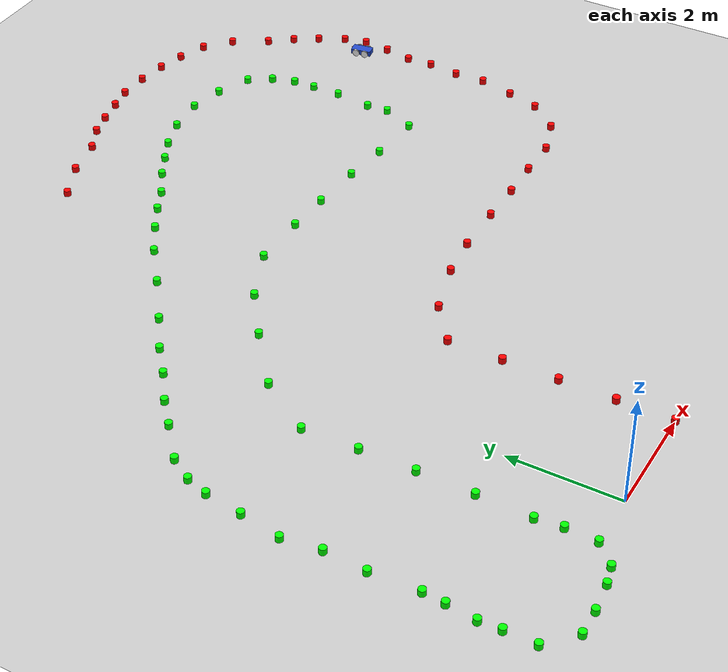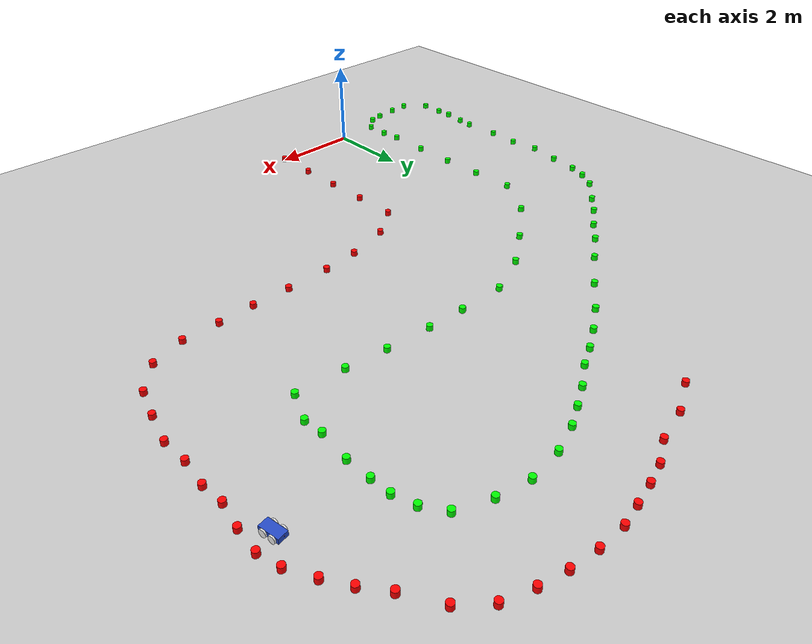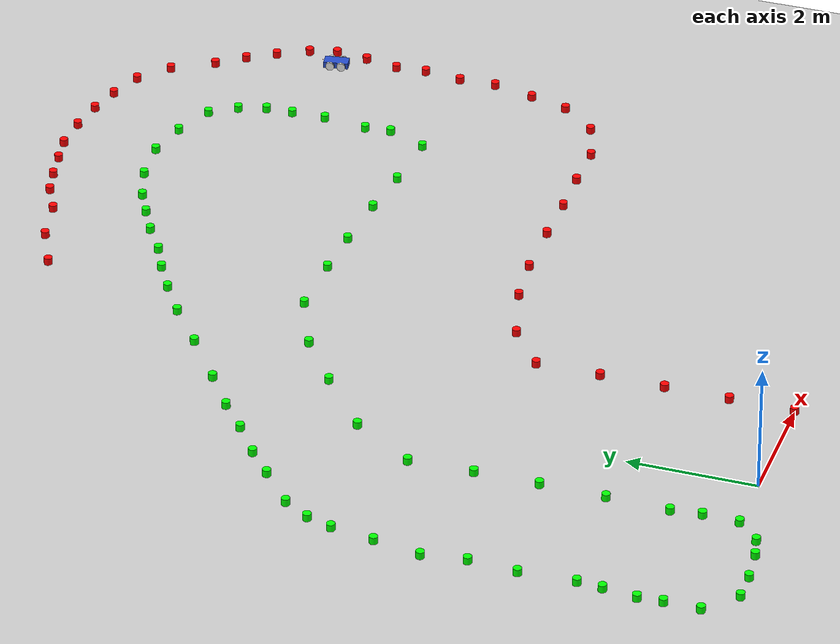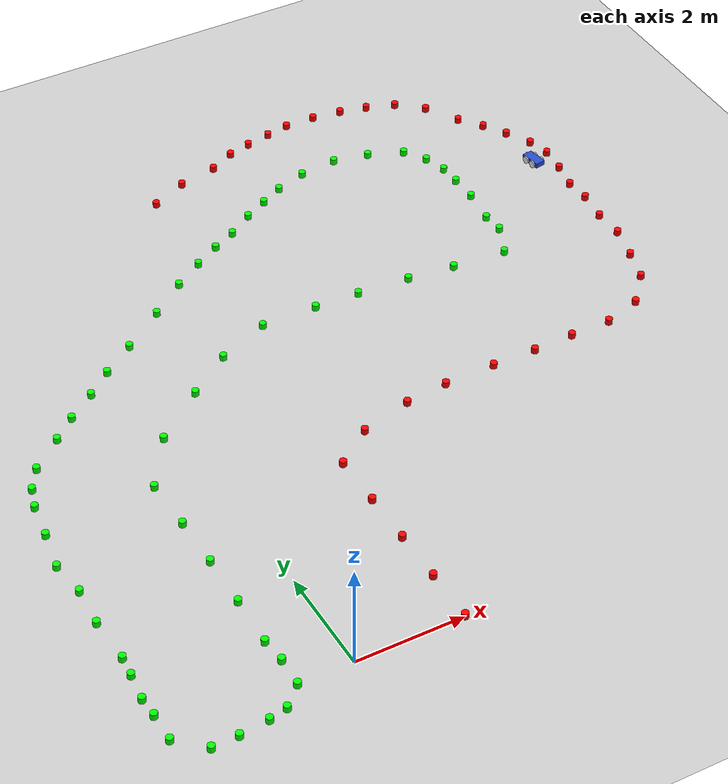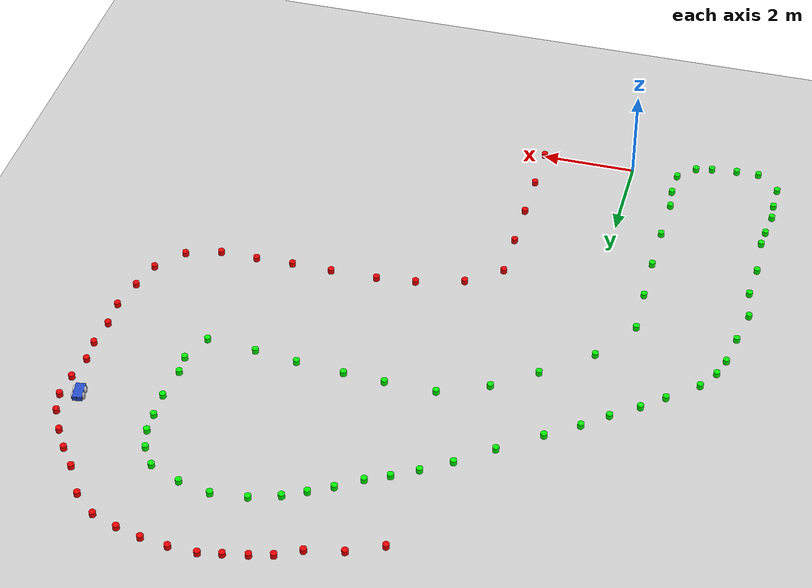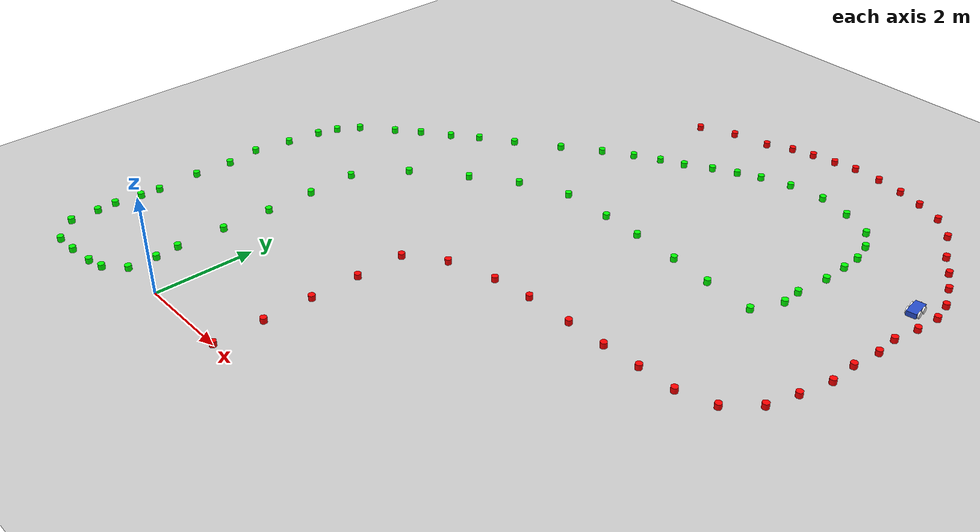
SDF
<sdf version="1.7">
 <world name="default">
  <light name="sun" type="directional">
   <pose>0 0 10 0 -0 0</pose>
   <diffuse>0.8 0.8 0.8 1</diffuse>
   <specular>0.2 0.2 0.2 1</specular>
   <attenuation>
    <range>1000</range>
    <constant>0.9</constant>
    <linear>0.01</linear>
    <quadratic>0.001</quadratic>
   </attenuation>
   <direction>-0.5 0.1 -0.9</direction>
   <spot><inner_angle>0</inner_angle><outer_angle>0</outer_angle><falloff>0</falloff></spot>
  </light>
  <model name="ground_plane">
   <static>1</static>
   <link name="link">
    <collision name="collision">
     <geometry><plane><normal>0 0 1</normal><size>100 100</size></plane></geometry>
     <surface>
      <contact><collide_bitmask>65535</collide_bitmask></contact>
      <friction><ode><mu>100</mu><mu2>50</mu2></ode></friction>
     </surface>
    </collision>
    <visual name="visual">
     <cast_shadows>0</cast_shadows>
     <geometry><plane><normal>0 0 1</normal><size>100 100</size></plane></geometry>
     <material>
      <script><uri>file://media/materials/scripts/gazebo.material</uri><name>Gazebo/Grey</name></script>
     </material>
    </visual>
   </link>
  </model>
  <model name="latinha_verm">
   <link name="link">
    <inertial>
     <mass>1</mass>
     <inertia><ixx>0.145833</ixx><ixy>0</ixy><ixz>0</ixz><iyy>0.145833</iyy><iyz>0</iyz><izz>0.125</izz></inertia>
    </inertial>
    <visual name="visual">
     <geometry><cylinder><radius>0.066</radius><length>0.114</length></cylinder></geometry>
     <material>
      <script><name>Gazebo/Gray</name><uri>file://media/materials/scripts/gazebo.material</uri></script>
      <shader type="pixel"><normal_map>__default__</normal_map></shader>
      <ambient>1 0 0 1</ambient>
      <diffuse>1 0 0 1</diffuse>
      <specular>0.1 0.1 0.1 1</specular>
      <emissive>0 0 0 1</emissive>
     </material>
    </visual>
    <collision name="collision">
     <geometry><cylinder><radius>0.05</radius><length>0.1</length></cylinder></geometry>
     <surface>
      <friction>
       <ode><mu>1</mu><mu2>1</mu2><fdir1>0 0 0</fdir1><slip1>0</slip1><slip2>0</slip2></ode>
       <torsional>
        <coefficient>1</coefficient>
        <patch_radius>0</patch_radius>
        <surface_radius>0</surface_radius>
        <use_patch_radius>1</use_patch_radius>
        <ode><slip>0</slip></ode>
       </torsional>
      </friction>
      <bounce><restitution_coefficient>0</restitution_coefficient><threshold>1e+06</threshold></bounce>
      <contact>
       <collide_without_contact>0</collide_without_contact>
       <collide_without_contact_bitmask>1</collide_without_contact_bitmask>
       <collide_bitmask>1</collide_bitmask>
       <ode>
        <soft_cfm>0</soft_cfm>
        <soft_erp>0.2</soft_erp>
        <kp>1e+13</kp>
        <kd>1</kd>
        <max_vel>0.01</max_vel>
        <min_depth>0</min_depth>
       </ode>
       <bullet>
        <split_impulse>1</split_impulse>
        <split_impulse_penetration_threshold>-0.01</split_impulse_penetration_threshold>
        <soft_cfm>0</soft_cfm>
        <soft_erp>0.2</soft_erp>
        <kp>1e+13</kp>
        <kd>1</kd>
       </bullet>
      </contact>
     </surface>
    </collision>
   </link>
   <static>0</static>
   <pose>3.70951 4.81025 0.04999 0 -0 7.9e-05</pose>
  </model>
  <model name="latinha_verde">
   <link name="link">
    <inertial>
     <mass>1</mass>
     <inertia><ixx>0.145833</ixx><ixy>0</ixy><ixz>0</ixz><iyy>0.145833</iyy><iyz>0</iyz><izz>0.125</izz></inertia>
    </inertial>
    <visual name="visual">
     <geometry><cylinder><radius>0.066</radius><length>0.114</length></cylinder></geometry>
     <material>
      <script><name>Gazebo/Gray</name><uri>file://media/materials/scripts/gazebo.material</uri></script>
      <shader type="pixel"><normal_map>__default__</normal_map></shader>
      <ambient>0 1 0 1</ambient>
      <diffuse>0 1 0 1</diffuse>
      <specular>0.1 0.1 0.1 1</specular>
      <emissive>0 0 0 1</emissive>
     </material>
    </visual>
    <collision name="collision">
     <geometry><cylinder><radius>0.05</radius><length>0.1</length></cylinder></geometry>
     <surface>
      <friction>
       <ode><mu>1</mu><mu2>1</mu2><fdir1>0 0 0</fdir1><slip1>0</slip1><slip2>0</slip2></ode>
       <torsional>
        <coefficient>1</coefficient>
        <patch_radius>0</patch_radius>
        <surface_radius>0</surface_radius>
        <use_patch_radius>1</use_patch_radius>
        <ode><slip>0</slip></ode>
       </torsional>
      </friction>
      <bounce><restitution_coefficient>0</restitution_coefficient><threshold>1e+06</threshold></bounce>
      <contact>
       <collide_without_contact>0</collide_without_contact>
       <collide_without_contact_bitmask>1</collide_without_contact_bitmask>
       <collide_bitmask>1</collide_bitmask>
       <ode>
        <soft_cfm>0</soft_cfm>
        <soft_erp>0.2</soft_erp>
        <kp>1e+13</kp>
        <kd>1</kd>
        <max_vel>0.01</max_vel>
        <min_depth>0</min_depth>
       </ode>
       <bullet>
        <split_impulse>1</split_impulse>
        <split_impulse_penetration_threshold>-0.01</split_impulse_penetration_threshold>
        <soft_cfm>0</soft_cfm>
        <soft_erp>0.2</soft_erp>
        <kp>1e+13</kp>
        <kd>1</kd>
       </bullet>
      </contact>
     </surface>
    </collision>
   </link>
   <static>0</static>
   <pose>2.47505 7.83889 0.04999 0 -0 0.000132</pose>
  </model>
  <gravity>0 0 -9.8</gravity>
  <magnetic_field>6e-06 2.3e-05 -4.2e-05</magnetic_field>
  <atmosphere type="adiabatic"/>
  <physics type="ode">
   <max_step_size>0.001</max_step_size>
   <real_time_factor>1</real_time_factor>
   <real_time_update_rate>1000</real_time_update_rate>
  </physics>
  <scene><ambient>0.4 0.4 0.4 1</ambient><background>0.7 0.7 0.7 1</background><shadows>1</shadows></scene>
  <spherical_coordinates>
   <surface_model>EARTH_WGS84</surface_model>
   <latitude_deg>0</latitude_deg>
   <longitude_deg>0</longitude_deg>
   <elevation>0</elevation>
   <heading_deg>0</heading_deg>
  </spherical_coordinates>
  <model name="latinha_verm_clone">
   <link name="link">
    <inertial>
     <mass>1</mass>
     <inertia><ixx>0.145833</ixx><ixy>0</ixy><ixz>0</ixz><iyy>0.145833</iyy><iyz>0</iyz><izz>0.125</izz></inertia>
    </inertial>
    <visual name="visual">
     <geometry><cylinder><radius>0.066</radius><length>0.114</length></cylinder></geometry>
     <material>
      <script><name>Gazebo/Gray</name><uri>file://media/materials/scripts/gazebo.material</uri></script>
      <shader type="pixel"><normal_map>__default__</normal_map></shader>
      <ambient>1 0 0 1</ambient>
      <diffuse>1 0 0 1</diffuse>
      <specular>0.1 0.1 0.1 1</specular>
      <emissive>0 0 0 1</emissive>
     </material>
    </visual>
    <collision name="collision">
     <geometry><cylinder><radius>0.05</radius><length>0.1</length></cylinder></geometry>
     <surface>
      <friction>
       <ode><mu>1</mu><mu2>1</mu2><fdir1>0 0 0</fdir1><slip1>0</slip1><slip2>0</slip2></ode>
       <torsional>
        <coefficient>1</coefficient>
        <patch_radius>0</patch_radius>
        <surface_radius>0</surface_radius>
        <use_patch_radius>1</use_patch_radius>
        <ode><slip>0</slip></ode>
       </torsional>
      </friction>
      <bounce><restitution_coefficient>0</restitution_coefficient><threshold>1e+06</threshold></bounce>
      <contact>
       <collide_without_contact>0</collide_without_contact>
       <collide_without_contact_bitmask>1</collide_without_contact_bitmask>
       <collide_bitmask>1</collide_bitmask>
       <ode>
        <soft_cfm>0</soft_cfm>
        <soft_erp>0.2</soft_erp>
        <kp>1e+13</kp>
        <kd>1</kd>
        <max_vel>0.01</max_vel>
        <min_depth>0</min_depth>
       </ode>
       <bullet>
        <split_impulse>1</split_impulse>
        <split_impulse_penetration_threshold>-0.01</split_impulse_penetration_threshold>
        <soft_cfm>0</soft_cfm>
        <soft_erp>0.2</soft_erp>
        <kp>1e+13</kp>
        <kd>1</kd>
       </bullet>
      </contact>
     </surface>
    </collision>
   </link>
   <static>0</static>
   <pose>2 -0 0.049995 0 -0 3.3e-05</pose>
  </model>
  <model name="latinha_verm_clone_0">
   <link name="link">
    <inertial>
     <mass>1</mass>
     <inertia><ixx>0.145833</ixx><ixy>0</ixy><ixz>0</ixz><iyy>0.145833</iyy><iyz>0</iyz><izz>0.125</izz></inertia>
    </inertial>
    <visual name="visual">
     <geometry><cylinder><radius>0.066</radius><length>0.114</length></cylinder></geometry>
     <material>
      <script><name>Gazebo/Gray</name><uri>file://media/materials/scripts/gazebo.material</uri></script>
      <shader type="pixel"><normal_map>__default__</normal_map></shader>
      <ambient>1 0 0 1</ambient>
      <diffuse>1 0 0 1</diffuse>
      <specular>0.1 0.1 0.1 1</specular>
      <emissive>0 0 0 1</emissive>
     </material>
    </visual>
    <collision name="collision">
     <geometry><cylinder><radius>0.05</radius><length>0.1</length></cylinder></geometry>
     <surface>
      <friction>
       <ode><mu>1</mu><mu2>1</mu2><fdir1>0 0 0</fdir1><slip1>0</slip1><slip2>0</slip2></ode>
       <torsional>
        <coefficient>1</coefficient>
        <patch_radius>0</patch_radius>
        <surface_radius>0</surface_radius>
        <use_patch_radius>1</use_patch_radius>
        <ode><slip>0</slip></ode>
       </torsional>
      </friction>
      <bounce><restitution_coefficient>0</restitution_coefficient><threshold>1e+06</threshold></bounce>
      <contact>
       <collide_without_contact>0</collide_without_contact>
       <collide_without_contact_bitmask>1</collide_without_contact_bitmask>
       <collide_bitmask>1</collide_bitmask>
       <ode>
        <soft_cfm>0</soft_cfm>
        <soft_erp>0.2</soft_erp>
        <kp>1e+13</kp>
        <kd>1</kd>
        <max_vel>0.01</max_vel>
        <min_depth>0</min_depth>
       </ode>
       <bullet>
        <split_impulse>1</split_impulse>
        <split_impulse_penetration_threshold>-0.01</split_impulse_penetration_threshold>
        <soft_cfm>0</soft_cfm>
        <soft_erp>0.2</soft_erp>
        <kp>1e+13</kp>
        <kd>1</kd>
       </bullet>
      </contact>
     </surface>
    </collision>
   </link>
   <static>0</static>
   <pose>2 1 0.049995 0 -0 8.9e-05</pose>
  </model>
  <model name="latinha_verm_clone_1">
   <link name="link">
    <inertial>
     <mass>1</mass>
     <inertia><ixx>0.145833</ixx><ixy>0</ixy><ixz>0</ixz><iyy>0.145833</iyy><iyz>0</iyz><izz>0.125</izz></inertia>
    </inertial>
    <visual name="visual">
     <geometry><cylinder><radius>0.066</radius><length>0.114</length></cylinder></geometry>
     <material>
      <script><name>Gazebo/Gray</name><uri>file://media/materials/scripts/gazebo.material</uri></script>
      <shader type="pixel"><normal_map>__default__</normal_map></shader>
      <ambient>1 0 0 1</ambient>
      <diffuse>1 0 0 1</diffuse>
      <specular>0.1 0.1 0.1 1</specular>
      <emissive>0 0 0 1</emissive>
     </material>
    </visual>
    <collision name="collision">
     <geometry><cylinder><radius>0.05</radius><length>0.1</length></cylinder></geometry>
     <surface>
      <friction>
       <ode><mu>1</mu><mu2>1</mu2><fdir1>0 0 0</fdir1><slip1>0</slip1><slip2>0</slip2></ode>
       <torsional>
        <coefficient>1</coefficient>
        <patch_radius>0</patch_radius>
        <surface_radius>0</surface_radius>
        <use_patch_radius>1</use_patch_radius>
        <ode><slip>0</slip></ode>
       </torsional>
      </friction>
      <bounce><restitution_coefficient>0</restitution_coefficient><threshold>1e+06</threshold></bounce>
      <contact>
       <collide_without_contact>0</collide_without_contact>
       <collide_without_contact_bitmask>1</collide_without_contact_bitmask>
       <collide_bitmask>1</collide_bitmask>
       <ode>
        <soft_cfm>0</soft_cfm>
        <soft_erp>0.2</soft_erp>
        <kp>1e+13</kp>
        <kd>1</kd>
        <max_vel>0.01</max_vel>
        <min_depth>0</min_depth>
       </ode>
       <bullet>
        <split_impulse>1</split_impulse>
        <split_impulse_penetration_threshold>-0.01</split_impulse_penetration_threshold>
        <soft_cfm>0</soft_cfm>
        <soft_erp>0.2</soft_erp>
        <kp>1e+13</kp>
        <kd>1</kd>
       </bullet>
      </contact>
     </surface>
    </collision>
   </link>
   <static>0</static>
   <pose>2 2 0.049995 0 -0 8.4e-05</pose>
  </model>
  <model name="latinha_verm_clone_2">
   <link name="link">
    <inertial>
     <mass>1</mass>
     <inertia><ixx>0.145833</ixx><ixy>0</ixy><ixz>0</ixz><iyy>0.145833</iyy><iyz>0</iyz><izz>0.125</izz></inertia>
    </inertial>
    <visual name="visual">
     <geometry><cylinder><radius>0.066</radius><length>0.114</length></cylinder></geometry>
     <material>
      <script><name>Gazebo/Gray</name><uri>file://media/materials/scripts/gazebo.material</uri></script>
      <shader type="pixel"><normal_map>__default__</normal_map></shader>
      <ambient>1 0 0 1</ambient>
      <diffuse>1 0 0 1</diffuse>
      <specular>0.1 0.1 0.1 1</specular>
      <emissive>0 0 0 1</emissive>
     </material>
    </visual>
    <collision name="collision">
     <geometry><cylinder><radius>0.05</radius><length>0.1</length></cylinder></geometry>
     <surface>
      <friction>
       <ode><mu>1</mu><mu2>1</mu2><fdir1>0 0 0</fdir1><slip1>0</slip1><slip2>0</slip2></ode>
       <torsional>
        <coefficient>1</coefficient>
        <patch_radius>0</patch_radius>
        <surface_radius>0</surface_radius>
        <use_patch_radius>1</use_patch_radius>
        <ode><slip>0</slip></ode>
       </torsional>
      </friction>
      <bounce><restitution_coefficient>0</restitution_coefficient><threshold>1e+06</threshold></bounce>
      <contact>
       <collide_without_contact>0</collide_without_contact>
       <collide_without_contact_bitmask>1</collide_without_contact_bitmask>
       <collide_bitmask>1</collide_bitmask>
       <ode>
        <soft_cfm>0</soft_cfm>
        <soft_erp>0.2</soft_erp>
        <kp>1e+13</kp>
        <kd>1</kd>
        <max_vel>0.01</max_vel>
        <min_depth>0</min_depth>
       </ode>
       <bullet>
        <split_impulse>1</split_impulse>
        <split_impulse_penetration_threshold>-0.01</split_impulse_penetration_threshold>
        <soft_cfm>0</soft_cfm>
        <soft_erp>0.2</soft_erp>
        <kp>1e+13</kp>
        <kd>1</kd>
       </bullet>
      </contact>
     </surface>
    </collision>
   </link>
   <static>0</static>
   <pose>2 3 0.05 0 -0 0.000163</pose>
  </model>
  <model name="latinha_verm_clone_3">
   <link name="link">
    <inertial>
     <mass>1</mass>
     <inertia><ixx>0.145833</ixx><ixy>0</ixy><ixz>0</ixz><iyy>0.145833</iyy><iyz>0</iyz><izz>0.125</izz></inertia>
    </inertial>
    <visual name="visual">
     <geometry><cylinder><radius>0.066</radius><length>0.114</length></cylinder></geometry>
     <material>
      <script><name>Gazebo/Gray</name><uri>file://media/materials/scripts/gazebo.material</uri></script>
      <shader type="pixel"><normal_map>__default__</normal_map></shader>
      <ambient>1 0 0 1</ambient>
      <diffuse>1 0 0 1</diffuse>
      <specular>0.1 0.1 0.1 1</specular>
      <emissive>0 0 0 1</emissive>
     </material>
    </visual>
    <collision name="collision">
     <geometry><cylinder><radius>0.05</radius><length>0.1</length></cylinder></geometry>
     <surface>
      <friction>
       <ode><mu>1</mu><mu2>1</mu2><fdir1>0 0 0</fdir1><slip1>0</slip1><slip2>0</slip2></ode>
       <torsional>
        <coefficient>1</coefficient>
        <patch_radius>0</patch_radius>
        <surface_radius>0</surface_radius>
        <use_patch_radius>1</use_patch_radius>
        <ode><slip>0</slip></ode>
       </torsional>
      </friction>
      <bounce><restitution_coefficient>0</restitution_coefficient><threshold>1e+06</threshold></bounce>
      <contact>
       <collide_without_contact>0</collide_without_contact>
       <collide_without_contact_bitmask>1</collide_without_contact_bitmask>
       <collide_bitmask>1</collide_bitmask>
       <ode>
        <soft_cfm>0</soft_cfm>
        <soft_erp>0.2</soft_erp>
        <kp>1e+13</kp>
        <kd>1</kd>
        <max_vel>0.01</max_vel>
        <min_depth>0</min_depth>
       </ode>
       <bullet>
        <split_impulse>1</split_impulse>
        <split_impulse_penetration_threshold>-0.01</split_impulse_penetration_threshold>
        <soft_cfm>0</soft_cfm>
        <soft_erp>0.2</soft_erp>
        <kp>1e+13</kp>
        <kd>1</kd>
       </bullet>
      </contact>
     </surface>
    </collision>
   </link>
   <static>0</static>
   <pose>2 4 0.049995 -2e-06 1e-06 0.000177</pose>
  </model>
  <model name="latinha_verm_clone_4">
   <link name="link">
    <inertial>
     <mass>1</mass>
     <inertia><ixx>0.145833</ixx><ixy>0</ixy><ixz>0</ixz><iyy>0.145833</iyy><iyz>0</iyz><izz>0.125</izz></inertia>
    </inertial>
    <visual name="visual">
     <geometry><cylinder><radius>0.066</radius><length>0.114</length></cylinder></geometry>
     <material>
      <script><name>Gazebo/Gray</name><uri>file://media/materials/scripts/gazebo.material</uri></script>
      <shader type="pixel"><normal_map>__default__</normal_map></shader>
      <ambient>1 0 0 1</ambient>
      <diffuse>1 0 0 1</diffuse>
      <specular>0.1 0.1 0.1 1</specular>
      <emissive>0 0 0 1</emissive>
     </material>
    </visual>
    <collision name="collision">
     <geometry><cylinder><radius>0.05</radius><length>0.1</length></cylinder></geometry>
     <surface>
      <friction>
       <ode><mu>1</mu><mu2>1</mu2><fdir1>0 0 0</fdir1><slip1>0</slip1><slip2>0</slip2></ode>
       <torsional>
        <coefficient>1</coefficient>
        <patch_radius>0</patch_radius>
        <surface_radius>0</surface_radius>
        <use_patch_radius>1</use_patch_radius>
        <ode><slip>0</slip></ode>
       </torsional>
      </friction>
      <bounce><restitution_coefficient>0</restitution_coefficient><threshold>1e+06</threshold></bounce>
      <contact>
       <collide_without_contact>0</collide_without_contact>
       <collide_without_contact_bitmask>1</collide_without_contact_bitmask>
       <collide_bitmask>1</collide_bitmask>
       <ode>
        <soft_cfm>0</soft_cfm>
        <soft_erp>0.2</soft_erp>
        <kp>1e+13</kp>
        <kd>1</kd>
        <max_vel>0.01</max_vel>
        <min_depth>0</min_depth>
       </ode>
       <bullet>
        <split_impulse>1</split_impulse>
        <split_impulse_penetration_threshold>-0.01</split_impulse_penetration_threshold>
        <soft_cfm>0</soft_cfm>
        <soft_erp>0.2</soft_erp>
        <kp>1e+13</kp>
        <kd>1</kd>
       </bullet>
      </contact>
     </surface>
    </collision>
   </link>
   <static>0</static>
   <pose>2.71601 4.53432 0.049994 0 -0 0.000136</pose>
  </model>
  <model name="latinha_verde_clone">
   <link name="link">
    <inertial>
     <mass>1</mass>
     <inertia><ixx>0.145833</ixx><ixy>0</ixy><ixz>0</ixz><iyy>0.145833</iyy><iyz>0</iyz><izz>0.125</izz></inertia>
    </inertial>
    <visual name="visual">
     <geometry><cylinder><radius>0.066</radius><length>0.114</length></cylinder></geometry>
     <material>
      <script><name>Gazebo/Gray</name><uri>file://media/materials/scripts/gazebo.material</uri></script>
      <shader type="pixel"><normal_map>__default__</normal_map></shader>
      <ambient>0 1 0 1</ambient>
      <diffuse>0 1 0 1</diffuse>
      <specular>0.1 0.1 0.1 1</specular>
      <emissive>0 0 0 1</emissive>
     </material>
    </visual>
    <collision name="collision">
     <geometry><cylinder><radius>0.05</radius><length>0.1</length></cylinder></geometry>
     <surface>
      <friction>
       <ode><mu>1</mu><mu2>1</mu2><fdir1>0 0 0</fdir1><slip1>0</slip1><slip2>0</slip2></ode>
       <torsional>
        <coefficient>1</coefficient>
        <patch_radius>0</patch_radius>
        <surface_radius>0</surface_radius>
        <use_patch_radius>1</use_patch_radius>
        <ode><slip>0</slip></ode>
       </torsional>
      </friction>
      <bounce><restitution_coefficient>0</restitution_coefficient><threshold>1e+06</threshold></bounce>
      <contact>
       <collide_without_contact>0</collide_without_contact>
       <collide_without_contact_bitmask>1</collide_without_contact_bitmask>
       <collide_bitmask>1</collide_bitmask>
       <ode>
        <soft_cfm>0</soft_cfm>
        <soft_erp>0.2</soft_erp>
        <kp>1e+13</kp>
        <kd>1</kd>
        <max_vel>0.01</max_vel>
        <min_depth>0</min_depth>
       </ode>
       <bullet>
        <split_impulse>1</split_impulse>
        <split_impulse_penetration_threshold>-0.01</split_impulse_penetration_threshold>
        <soft_cfm>0</soft_cfm>
        <soft_erp>0.2</soft_erp>
        <kp>1e+13</kp>
        <kd>1</kd>
       </bullet>
      </contact>
     </surface>
    </collision>
   </link>
   <static>0</static>
   <pose>-1 0 0.049996 0 -0 8.4e-05</pose>
  </model>
  <model name="latinha_verde_clone_0">
   <link name="link">
    <inertial>
     <mass>1</mass>
     <inertia><ixx>0.145833</ixx><ixy>0</ixy><ixz>0</ixz><iyy>0.145833</iyy><iyz>0</iyz><izz>0.125</izz></inertia>
    </inertial>
    <visual name="visual">
     <geometry><cylinder><radius>0.066</radius><length>0.114</length></cylinder></geometry>
     <material>
      <script><name>Gazebo/Gray</name><uri>file://media/materials/scripts/gazebo.material</uri></script>
      <shader type="pixel"><normal_map>__default__</normal_map></shader>
      <ambient>0 1 0 1</ambient>
      <diffuse>0 1 0 1</diffuse>
      <specular>0.1 0.1 0.1 1</specular>
      <emissive>0 0 0 1</emissive>
     </material>
    </visual>
    <collision name="collision">
     <geometry><cylinder><radius>0.05</radius><length>0.1</length></cylinder></geometry>
     <surface>
      <friction>
       <ode><mu>1</mu><mu2>1</mu2><fdir1>0 0 0</fdir1><slip1>0</slip1><slip2>0</slip2></ode>
       <torsional>
        <coefficient>1</coefficient>
        <patch_radius>0</patch_radius>
        <surface_radius>0</surface_radius>
        <use_patch_radius>1</use_patch_radius>
        <ode><slip>0</slip></ode>
       </torsional>
      </friction>
      <bounce><restitution_coefficient>0</restitution_coefficient><threshold>1e+06</threshold></bounce>
      <contact>
       <collide_without_contact>0</collide_without_contact>
       <collide_without_contact_bitmask>1</collide_without_contact_bitmask>
       <collide_bitmask>1</collide_bitmask>
       <ode>
        <soft_cfm>0</soft_cfm>
        <soft_erp>0.2</soft_erp>
        <kp>1e+13</kp>
        <kd>1</kd>
        <max_vel>0.01</max_vel>
        <min_depth>0</min_depth>
       </ode>
       <bullet>
        <split_impulse>1</split_impulse>
        <split_impulse_penetration_threshold>-0.01</split_impulse_penetration_threshold>
        <soft_cfm>0</soft_cfm>
        <soft_erp>0.2</soft_erp>
        <kp>1e+13</kp>
        <kd>1</kd>
       </bullet>
      </contact>
     </surface>
    </collision>
   </link>
   <static>0</static>
   <pose>-1.02906 1.03191 0.049996 0 -0 7.2e-05</pose>
  </model>
  <model name="latinha_verde_clone_1">
   <link name="link">
    <inertial>
     <mass>1</mass>
     <inertia><ixx>0.145833</ixx><ixy>0</ixy><ixz>0</ixz><iyy>0.145833</iyy><iyz>0</iyz><izz>0.125</izz></inertia>
    </inertial>
    <visual name="visual">
     <geometry><cylinder><radius>0.066</radius><length>0.114</length></cylinder></geometry>
     <material>
      <script><name>Gazebo/Gray</name><uri>file://media/materials/scripts/gazebo.material</uri></script>
      <shader type="pixel"><normal_map>__default__</normal_map></shader>
      <ambient>0 1 0 1</ambient>
      <diffuse>0 1 0 1</diffuse>
      <specular>0.1 0.1 0.1 1</specular>
      <emissive>0 0 0 1</emissive>
     </material>
    </visual>
    <collision name="collision">
     <geometry><cylinder><radius>0.05</radius><length>0.1</length></cylinder></geometry>
     <surface>
      <friction>
       <ode><mu>1</mu><mu2>1</mu2><fdir1>0 0 0</fdir1><slip1>0</slip1><slip2>0</slip2></ode>
       <torsional>
        <coefficient>1</coefficient>
        <patch_radius>0</patch_radius>
        <surface_radius>0</surface_radius>
        <use_patch_radius>1</use_patch_radius>
        <ode><slip>0</slip></ode>
       </torsional>
      </friction>
      <bounce><restitution_coefficient>0</restitution_coefficient><threshold>1e+06</threshold></bounce>
      <contact>
       <collide_without_contact>0</collide_without_contact>
       <collide_without_contact_bitmask>1</collide_without_contact_bitmask>
       <collide_bitmask>1</collide_bitmask>
       <ode>
        <soft_cfm>0</soft_cfm>
        <soft_erp>0.2</soft_erp>
        <kp>1e+13</kp>
        <kd>1</kd>
        <max_vel>0.01</max_vel>
        <min_depth>0</min_depth>
       </ode>
       <bullet>
        <split_impulse>1</split_impulse>
        <split_impulse_penetration_threshold>-0.01</split_impulse_penetration_threshold>
        <soft_cfm>0</soft_cfm>
        <soft_erp>0.2</soft_erp>
        <kp>1e+13</kp>
        <kd>1</kd>
       </bullet>
      </contact>
     </surface>
    </collision>
   </link>
   <static>0</static>
   <pose>-1.00145 2.00429 0.049996 0 -0 0.000115</pose>
  </model>
  <model name="latinha_verde_clone_2">
   <link name="link">
    <inertial>
     <mass>1</mass>
     <inertia><ixx>0.145833</ixx><ixy>0</ixy><ixz>0</ixz><iyy>0.145833</iyy><iyz>0</iyz><izz>0.125</izz></inertia>
    </inertial>
    <visual name="visual">
     <geometry><cylinder><radius>0.066</radius><length>0.114</length></cylinder></geometry>
     <material>
      <script><name>Gazebo/Gray</name><uri>file://media/materials/scripts/gazebo.material</uri></script>
      <shader type="pixel"><normal_map>__default__</normal_map></shader>
      <ambient>0 1 0 1</ambient>
      <diffuse>0 1 0 1</diffuse>
      <specular>0.1 0.1 0.1 1</specular>
      <emissive>0 0 0 1</emissive>
     </material>
    </visual>
    <collision name="collision">
     <geometry><cylinder><radius>0.05</radius><length>0.1</length></cylinder></geometry>
     <surface>
      <friction>
       <ode><mu>1</mu><mu2>1</mu2><fdir1>0 0 0</fdir1><slip1>0</slip1><slip2>0</slip2></ode>
       <torsional>
        <coefficient>1</coefficient>
        <patch_radius>0</patch_radius>
        <surface_radius>0</surface_radius>
        <use_patch_radius>1</use_patch_radius>
        <ode><slip>0</slip></ode>
       </torsional>
      </friction>
      <bounce><restitution_coefficient>0</restitution_coefficient><threshold>1e+06</threshold></bounce>
      <contact>
       <collide_without_contact>0</collide_without_contact>
       <collide_without_contact_bitmask>1</collide_without_contact_bitmask>
       <collide_bitmask>1</collide_bitmask>
       <ode>
        <soft_cfm>0</soft_cfm>
        <soft_erp>0.2</soft_erp>
        <kp>1e+13</kp>
        <kd>1</kd>
        <max_vel>0.01</max_vel>
        <min_depth>0</min_depth>
       </ode>
       <bullet>
        <split_impulse>1</split_impulse>
        <split_impulse_penetration_threshold>-0.01</split_impulse_penetration_threshold>
        <soft_cfm>0</soft_cfm>
        <soft_erp>0.2</soft_erp>
        <kp>1e+13</kp>
        <kd>1</kd>
       </bullet>
      </contact>
     </surface>
    </collision>
   </link>
   <static>0</static>
   <pose>-0.989341 3.01541 0.049995 0 -0 6.7e-05</pose>
  </model>
  <model name="latinha_verde_clone_3">
   <link name="link">
    <inertial>
     <mass>1</mass>
     <inertia><ixx>0.145833</ixx><ixy>0</ixy><ixz>0</ixz><iyy>0.145833</iyy><iyz>0</iyz><izz>0.125</izz></inertia>
    </inertial>
    <visual name="visual">
     <geometry><cylinder><radius>0.066</radius><length>0.114</length></cylinder></geometry>
     <material>
      <script><name>Gazebo/Gray</name><uri>file://media/materials/scripts/gazebo.material</uri></script>
      <shader type="pixel"><normal_map>__default__</normal_map></shader>
      <ambient>0 1 0 1</ambient>
      <diffuse>0 1 0 1</diffuse>
      <specular>0.1 0.1 0.1 1</specular>
      <emissive>0 0 0 1</emissive>
     </material>
    </visual>
    <collision name="collision">
     <geometry><cylinder><radius>0.05</radius><length>0.1</length></cylinder></geometry>
     <surface>
      <friction>
       <ode><mu>1</mu><mu2>1</mu2><fdir1>0 0 0</fdir1><slip1>0</slip1><slip2>0</slip2></ode>
       <torsional>
        <coefficient>1</coefficient>
        <patch_radius>0</patch_radius>
        <surface_radius>0</surface_radius>
        <use_patch_radius>1</use_patch_radius>
        <ode><slip>0</slip></ode>
       </torsional>
      </friction>
      <bounce><restitution_coefficient>0</restitution_coefficient><threshold>1e+06</threshold></bounce>
      <contact>
       <collide_without_contact>0</collide_without_contact>
       <collide_without_contact_bitmask>1</collide_without_contact_bitmask>
       <collide_bitmask>1</collide_bitmask>
       <ode>
        <soft_cfm>0</soft_cfm>
        <soft_erp>0.2</soft_erp>
        <kp>1e+13</kp>
        <kd>1</kd>
        <max_vel>0.01</max_vel>
        <min_depth>0</min_depth>
       </ode>
       <bullet>
        <split_impulse>1</split_impulse>
        <split_impulse_penetration_threshold>-0.01</split_impulse_penetration_threshold>
        <soft_cfm>0</soft_cfm>
        <soft_erp>0.2</soft_erp>
        <kp>1e+13</kp>
        <kd>1</kd>
       </bullet>
      </contact>
     </surface>
    </collision>
   </link>
   <static>0</static>
   <pose>-0.99862 4.01189 0.049994 0 -0 0.000126</pose>
  </model>
  <model name="latinha_verde_clone_4">
   <link name="link">
    <inertial>
     <mass>1</mass>
     <inertia><ixx>0.145833</ixx><ixy>0</ixy><ixz>0</ixz><iyy>0.145833</iyy><iyz>0</iyz><izz>0.125</izz></inertia>
    </inertial>
    <visual name="visual">
     <geometry><cylinder><radius>0.066</radius><length>0.114</length></cylinder></geometry>
     <material>
      <script><name>Gazebo/Gray</name><uri>file://media/materials/scripts/gazebo.material</uri></script>
      <shader type="pixel"><normal_map>__default__</normal_map></shader>
      <ambient>0 1 0 1</ambient>
      <diffuse>0 1 0 1</diffuse>
      <specular>0.1 0.1 0.1 1</specular>
      <emissive>0 0 0 1</emissive>
     </material>
    </visual>
    <collision name="collision">
     <geometry><cylinder><radius>0.05</radius><length>0.1</length></cylinder></geometry>
     <surface>
      <friction>
       <ode><mu>1</mu><mu2>1</mu2><fdir1>0 0 0</fdir1><slip1>0</slip1><slip2>0</slip2></ode>
       <torsional>
        <coefficient>1</coefficient>
        <patch_radius>0</patch_radius>
        <surface_radius>0</surface_radius>
        <use_patch_radius>1</use_patch_radius>
        <ode><slip>0</slip></ode>
       </torsional>
      </friction>
      <bounce><restitution_coefficient>0</restitution_coefficient><threshold>1e+06</threshold></bounce>
      <contact>
       <collide_without_contact>0</collide_without_contact>
       <collide_without_contact_bitmask>1</collide_without_contact_bitmask>
       <collide_bitmask>1</collide_bitmask>
       <ode>
        <soft_cfm>0</soft_cfm>
        <soft_erp>0.2</soft_erp>
        <kp>1e+13</kp>
        <kd>1</kd>
        <max_vel>0.01</max_vel>
        <min_depth>0</min_depth>
       </ode>
       <bullet>
        <split_impulse>1</split_impulse>
        <split_impulse_penetration_threshold>-0.01</split_impulse_penetration_threshold>
        <soft_cfm>0</soft_cfm>
        <soft_erp>0.2</soft_erp>
        <kp>1e+13</kp>
        <kd>1</kd>
       </bullet>
      </contact>
     </surface>
    </collision>
   </link>
   <static>0</static>
   <pose>-1.02625 5.01775 0.049991 0 -0 0.000149</pose>
  </model>
  <model name="latinha_verde_clone_5">
   <link name="link">
    <inertial>
     <mass>1</mass>
     <inertia><ixx>0.145833</ixx><ixy>0</ixy><ixz>0</ixz><iyy>0.145833</iyy><iyz>0</iyz><izz>0.125</izz></inertia>
    </inertial>
    <visual name="visual">
     <geometry><cylinder><radius>0.066</radius><length>0.114</length></cylinder></geometry>
     <material>
      <script><name>Gazebo/Gray</name><uri>file://media/materials/scripts/gazebo.material</uri></script>
      <shader type="pixel"><normal_map>__default__</normal_map></shader>
      <ambient>0 1 0 1</ambient>
      <diffuse>0 1 0 1</diffuse>
      <specular>0.1 0.1 0.1 1</specular>
      <emissive>0 0 0 1</emissive>
     </material>
    </visual>
    <collision name="collision">
     <geometry><cylinder><radius>0.05</radius><length>0.1</length></cylinder></geometry>
     <surface>
      <friction>
       <ode><mu>1</mu><mu2>1</mu2><fdir1>0 0 0</fdir1><slip1>0</slip1><slip2>0</slip2></ode>
       <torsional>
        <coefficient>1</coefficient>
        <patch_radius>0</patch_radius>
        <surface_radius>0</surface_radius>
        <use_patch_radius>1</use_patch_radius>
        <ode><slip>0</slip></ode>
       </torsional>
      </friction>
      <bounce><restitution_coefficient>0</restitution_coefficient><threshold>1e+06</threshold></bounce>
      <contact>
       <collide_without_contact>0</collide_without_contact>
       <collide_without_contact_bitmask>1</collide_without_contact_bitmask>
       <collide_bitmask>1</collide_bitmask>
       <ode>
        <soft_cfm>0</soft_cfm>
        <soft_erp>0.2</soft_erp>
        <kp>1e+13</kp>
        <kd>1</kd>
        <max_vel>0.01</max_vel>
        <min_depth>0</min_depth>
       </ode>
       <bullet>
        <split_impulse>1</split_impulse>
        <split_impulse_penetration_threshold>-0.01</split_impulse_penetration_threshold>
        <soft_cfm>0</soft_cfm>
        <soft_erp>0.2</soft_erp>
        <kp>1e+13</kp>
        <kd>1</kd>
       </bullet>
      </contact>
     </surface>
    </collision>
   </link>
   <static>0</static>
   <pose>-0.371068 6.01386 0.049996 0 -0 4.4e-05</pose>
  </model>
  <model name="latinha_verde_clone_6">
   <link name="link">
    <inertial>
     <mass>1</mass>
     <inertia><ixx>0.145833</ixx><ixy>0</ixy><ixz>0</ixz><iyy>0.145833</iyy><iyz>0</iyz><izz>0.125</izz></inertia>
    </inertial>
    <visual name="visual">
     <geometry><cylinder><radius>0.066</radius><length>0.114</length></cylinder></geometry>
     <material>
      <script><name>Gazebo/Gray</name><uri>file://media/materials/scripts/gazebo.material</uri></script>
      <shader type="pixel"><normal_map>__default__</normal_map></shader>
      <ambient>0 1 0 1</ambient>
      <diffuse>0 1 0 1</diffuse>
      <specular>0.1 0.1 0.1 1</specular>
      <emissive>0 0 0 1</emissive>
     </material>
    </visual>
    <collision name="collision">
     <geometry><cylinder><radius>0.05</radius><length>0.1</length></cylinder></geometry>
     <surface>
      <friction>
       <ode><mu>1</mu><mu2>1</mu2><fdir1>0 0 0</fdir1><slip1>0</slip1><slip2>0</slip2></ode>
       <torsional>
        <coefficient>1</coefficient>
        <patch_radius>0</patch_radius>
        <surface_radius>0</surface_radius>
        <use_patch_radius>1</use_patch_radius>
        <ode><slip>0</slip></ode>
       </torsional>
      </friction>
      <bounce><restitution_coefficient>0</restitution_coefficient><threshold>1e+06</threshold></bounce>
      <contact>
       <collide_without_contact>0</collide_without_contact>
       <collide_without_contact_bitmask>1</collide_without_contact_bitmask>
       <collide_bitmask>1</collide_bitmask>
       <ode>
        <soft_cfm>0</soft_cfm>
        <soft_erp>0.2</soft_erp>
        <kp>1e+13</kp>
        <kd>1</kd>
        <max_vel>0.01</max_vel>
        <min_depth>0</min_depth>
       </ode>
       <bullet>
        <split_impulse>1</split_impulse>
        <split_impulse_penetration_threshold>-0.01</split_impulse_penetration_threshold>
        <soft_cfm>0</soft_cfm>
        <soft_erp>0.2</soft_erp>
        <kp>1e+13</kp>
        <kd>1</kd>
       </bullet>
      </contact>
     </surface>
    </collision>
   </link>
   <static>0</static>
   <pose>0.615834 6.79992 0.049995 0 -0 1e-06</pose>
  </model>
  <model name="latinha_verde_clone_7">
   <link name="link">
    <inertial>
     <mass>1</mass>
     <inertia><ixx>0.145833</ixx><ixy>0</ixy><ixz>0</ixz><iyy>0.145833</iyy><iyz>0</iyz><izz>0.125</izz></inertia>
    </inertial>
    <visual name="visual">
     <geometry><cylinder><radius>0.066</radius><length>0.114</length></cylinder></geometry>
     <material>
      <script><name>Gazebo/Gray</name><uri>file://media/materials/scripts/gazebo.material</uri></script>
      <shader type="pixel"><normal_map>__default__</normal_map></shader>
      <ambient>0 1 0 1</ambient>
      <diffuse>0 1 0 1</diffuse>
      <specular>0.1 0.1 0.1 1</specular>
      <emissive>0 0 0 1</emissive>
     </material>
    </visual>
    <collision name="collision">
     <geometry><cylinder><radius>0.05</radius><length>0.1</length></cylinder></geometry>
     <surface>
      <friction>
       <ode><mu>1</mu><mu2>1</mu2><fdir1>0 0 0</fdir1><slip1>0</slip1><slip2>0</slip2></ode>
       <torsional>
        <coefficient>1</coefficient>
        <patch_radius>0</patch_radius>
        <surface_radius>0</surface_radius>
        <use_patch_radius>1</use_patch_radius>
        <ode><slip>0</slip></ode>
       </torsional>
      </friction>
      <bounce><restitution_coefficient>0</restitution_coefficient><threshold>1e+06</threshold></bounce>
      <contact>
       <collide_without_contact>0</collide_without_contact>
       <collide_without_contact_bitmask>1</collide_without_contact_bitmask>
       <collide_bitmask>1</collide_bitmask>
       <ode>
        <soft_cfm>0</soft_cfm>
        <soft_erp>0.2</soft_erp>
        <kp>1e+13</kp>
        <kd>1</kd>
        <max_vel>0.01</max_vel>
        <min_depth>0</min_depth>
       </ode>
       <bullet>
        <split_impulse>1</split_impulse>
        <split_impulse_penetration_threshold>-0.01</split_impulse_penetration_threshold>
        <soft_cfm>0</soft_cfm>
        <soft_erp>0.2</soft_erp>
        <kp>1e+13</kp>
        <kd>1</kd>
       </bullet>
      </contact>
     </surface>
    </collision>
   </link>
   <static>0</static>
   <pose>1.47032 7.41257 0.049995 0 -0 5.9e-05</pose>
  </model>
  <model name="latinha_verde_clone_8">
   <link name="link">
    <inertial>
     <mass>1</mass>
     <inertia><ixx>0.145833</ixx><ixy>0</ixy><ixz>0</ixz><iyy>0.145833</iyy><iyz>0</iyz><izz>0.125</izz></inertia>
    </inertial>
    <visual name="visual">
     <geometry><cylinder><radius>0.066</radius><length>0.114</length></cylinder></geometry>
     <material>
      <script><name>Gazebo/Gray</name><uri>file://media/materials/scripts/gazebo.material</uri></script>
      <shader type="pixel"><normal_map>__default__</normal_map></shader>
      <ambient>0 1 0 1</ambient>
      <diffuse>0 1 0 1</diffuse>
      <specular>0.1 0.1 0.1 1</specular>
      <emissive>0 0 0 1</emissive>
     </material>
    </visual>
    <collision name="collision">
     <geometry><cylinder><radius>0.05</radius><length>0.1</length></cylinder></geometry>
     <surface>
      <friction>
       <ode><mu>1</mu><mu2>1</mu2><fdir1>0 0 0</fdir1><slip1>0</slip1><slip2>0</slip2></ode>
       <torsional>
        <coefficient>1</coefficient>
        <patch_radius>0</patch_radius>
        <surface_radius>0</surface_radius>
        <use_patch_radius>1</use_patch_radius>
        <ode><slip>0</slip></ode>
       </torsional>
      </friction>
      <bounce><restitution_coefficient>0</restitution_coefficient><threshold>1e+06</threshold></bounce>
      <contact>
       <collide_without_contact>0</collide_without_contact>
       <collide_without_contact_bitmask>1</collide_without_contact_bitmask>
       <collide_bitmask>1</collide_bitmask>
       <ode>
        <soft_cfm>0</soft_cfm>
        <soft_erp>0.2</soft_erp>
        <kp>1e+13</kp>
        <kd>1</kd>
        <max_vel>0.01</max_vel>
        <min_depth>0</min_depth>
       </ode>
       <bullet>
        <split_impulse>1</split_impulse>
        <split_impulse_penetration_threshold>-0.01</split_impulse_penetration_threshold>
        <soft_cfm>0</soft_cfm>
        <soft_erp>0.2</soft_erp>
        <kp>1e+13</kp>
        <kd>1</kd>
       </bullet>
      </contact>
     </surface>
    </collision>
   </link>
   <static>0</static>
   <pose>3.54294 7.83492 0.049995 2e-06 -0 0.000134</pose>
  </model>
  <model name="latinha_verm_clone_5">
   <link name="link">
    <inertial>
     <mass>1</mass>
     <inertia><ixx>0.145833</ixx><ixy>0</ixy><ixz>0</ixz><iyy>0.145833</iyy><iyz>0</iyz><izz>0.125</izz></inertia>
    </inertial>
    <visual name="visual">
     <geometry><cylinder><radius>0.066</radius><length>0.114</length></cylinder></geometry>
     <material>
      <script><name>Gazebo/Gray</name><uri>file://media/materials/scripts/gazebo.material</uri></script>
      <shader type="pixel"><normal_map>__default__</normal_map></shader>
      <ambient>1 0 0 1</ambient>
      <diffuse>1 0 0 1</diffuse>
      <specular>0.1 0.1 0.1 1</specular>
      <emissive>0 0 0 1</emissive>
     </material>
    </visual>
    <collision name="collision">
     <geometry><cylinder><radius>0.05</radius><length>0.1</length></cylinder></geometry>
     <surface>
      <friction>
       <ode><mu>1</mu><mu2>1</mu2><fdir1>0 0 0</fdir1><slip1>0</slip1><slip2>0</slip2></ode>
       <torsional>
        <coefficient>1</coefficient>
        <patch_radius>0</patch_radius>
        <surface_radius>0</surface_radius>
        <use_patch_radius>1</use_patch_radius>
        <ode><slip>0</slip></ode>
       </torsional>
      </friction>
      <bounce><restitution_coefficient>0</restitution_coefficient><threshold>1e+06</threshold></bounce>
      <contact>
       <collide_without_contact>0</collide_without_contact>
       <collide_without_contact_bitmask>1</collide_without_contact_bitmask>
       <collide_bitmask>1</collide_bitmask>
       <ode>
        <soft_cfm>0</soft_cfm>
        <soft_erp>0.2</soft_erp>
        <kp>1e+13</kp>
        <kd>1</kd>
        <max_vel>0.01</max_vel>
        <min_depth>0</min_depth>
       </ode>
       <bullet>
        <split_impulse>1</split_impulse>
        <split_impulse_penetration_threshold>-0.01</split_impulse_penetration_threshold>
        <soft_cfm>0</soft_cfm>
        <soft_erp>0.2</soft_erp>
        <kp>1e+13</kp>
        <kd>1</kd>
       </bullet>
      </contact>
     </surface>
    </collision>
   </link>
   <static>0</static>
   <pose>4.53531 4.90445 0.049994 0 -0 4.2e-05</pose>
  </model>
  <model name="robot">
   <link name="base_link">
    <inertial>
     <pose>0 0 0.08 0 -0 0</pose>
     <mass>21.6</mass>
     <inertia>
      <ixx>0.306001</ixx>
      <ixy>0</ixy>
      <ixz>0</ixz>
      <iyy>0.360001</iyy>
      <iyz>-8.8e-08</iyz>
      <izz>0.540001</izz>
     </inertia>
    </inertial>
    <collision name="base_link_collision">
     <pose>0 0 0.08 0 -0 0</pose>
     <geometry><box><size>0.2 0.4 0.1</size></box></geometry>
    </collision>
    <collision name="base_link_fixed_joint_lump__sensor_link_right_collision_1">
     <pose>0 0.22 0.12 0 -0 1.5708</pose>
     <geometry><box><size>0.01 0.01 0.01</size></box></geometry>
    </collision>
    <visual name="base_link_visual">
     <pose>0 0 0.08 0 -0 0</pose>
     <geometry><box><size>0.2 0.4 0.1</size></box></geometry>
     <material>
      <script><name>Gazebo/Blue</name><uri>file://media/materials/scripts/gazebo.material</uri></script>
     </material>
    </visual>
    <visual name="base_link_fixed_joint_lump__sensor_link_right_visual_1">
     <pose>0 0.22 0.12 0 -0 1.5708</pose>
     <geometry><box><size>0.01 0.01 0.01</size></box></geometry>
     <material>
      <script><name>Gazebo/Red</name><uri>file://media/materials/scripts/gazebo.material</uri></script>
     </material>
    </visual>
    <sensor name="camera_right" type="camera">
     <update_rate>30</update_rate>
     <camera name="head">
      <horizontal_fov>1.5</horizontal_fov>
      <image><width>640</width><height>480</height><format>R8G8B8</format></image>
      <clip><near>0.02</near><far>100</far></clip>
      <noise><type>gaussian</type><mean>0</mean><stddev>0.007</stddev></noise>
     </camera>
     <plugin name="camera_controller" filename="libgazebo_ros_camera.so">
      <alwaysOn>1</alwaysOn>
      <updateRate>0.0</updateRate>
      <cameraName>camera</cameraName>
      <frameName>camera_link</frameName>
      <imageTopicName>rgb/image_raw</imageTopicName>
      <depthImageTopicName>depth/image_raw</depthImageTopicName>
      <pointCloudTopicName>depth/points</pointCloudTopicName>
      <cameraInfoTopicName>rgb/camera_info</cameraInfoTopicName>
      <depthImageCameraInfoTopicName>depth/camera_info</depthImageCameraInfoTopicName>
      <pointCloudCutoff>0.4</pointCloudCutoff>
      <hackBaseline>0.07</hackBaseline>
      <distortionK1>0.0</distortionK1>
      <distortionK2>0.0</distortionK2>
      <distortionK3>0.0</distortionK3>
      <distortionT1>0.0</distortionT1>
      <distortionT2>0.0</distortionT2>
      <robotNamespace>/</robotNamespace>
     </plugin>
     <pose>0 0.22 0.12 0 -0 1.5708</pose>
    </sensor>
   </link>
   <joint name="joint_base_to_left_back_wheel" type="revolute">
    <pose relative_to="base_link">-0.115 -0.09 0.07 3.14159 1.57079 3.14159</pose>
    <parent>base_link</parent>
    <child>left_back_wheel</child>
    <axis>
     <xyz>0 0 1</xyz>
     <limit><lower>-1e+16</lower><upper>1e+16</upper></limit>
     <dynamics><spring_reference>0</spring_reference><spring_stiffness>0</spring_stiffness></dynamics>
    </axis>
   </joint>
   <link name="left_back_wheel">
    <pose relative_to="joint_base_to_left_back_wheel">0 0 0 0 -0 0</pose>
    <inertial>
     <mass>0.54</mass>
     <inertia>
      <ixx>0.000702</ixx>
      <ixy>0</ixy>
      <ixz>0</ixz>
      <iyy>0.000702</iyy>
      <iyz>0</iyz>
      <izz>0.001323</izz>
     </inertia>
    </inertial>
    <collision name="left_back_wheel_collision">
     <geometry><cylinder><length>0.03</length><radius>0.07</radius></cylinder></geometry>
    </collision>
    <visual name="left_back_wheel_visual">
     <geometry><cylinder><length>0.03</length><radius>0.07</radius></cylinder></geometry>
     <material>
      <script><name>Gazebo/White</name><uri>file://media/materials/scripts/gazebo.material</uri></script>
     </material>
    </visual>
   </link>
   <joint name="joint_base_to_left_front_wheel" type="revolute">
    <pose relative_to="base_link">-0.115 0.09 0.07 3.14159 1.57079 3.14159</pose>
    <parent>base_link</parent>
    <child>left_front_wheel</child>
    <axis>
     <xyz>0 0 1</xyz>
     <limit><lower>-1e+16</lower><upper>1e+16</upper></limit>
     <dynamics><spring_reference>0</spring_reference><spring_stiffness>0</spring_stiffness></dynamics>
    </axis>
   </joint>
   <link name="left_front_wheel">
    <pose relative_to="joint_base_to_left_front_wheel">0 0 0 0 -0 0</pose>
    <inertial>
     <mass>0.54</mass>
     <inertia>
      <ixx>0.000702</ixx>
      <ixy>0</ixy>
      <ixz>0</ixz>
      <iyy>0.000702</iyy>
      <iyz>0</iyz>
      <izz>0.001323</izz>
     </inertia>
    </inertial>
    <collision name="left_front_wheel_collision">
     <geometry><cylinder><length>0.03</length><radius>0.07</radius></cylinder></geometry>
    </collision>
    <visual name="left_front_wheel_visual">
     <geometry><cylinder><length>0.03</length><radius>0.07</radius></cylinder></geometry>
     <material>
      <script><name>Gazebo/White</name><uri>file://media/materials/scripts/gazebo.material</uri></script>
     </material>
    </visual>
   </link>
   <joint name="joint_base_to_right_back_wheel" type="revolute">
    <pose relative_to="base_link">0.115 -0.09 0.07 3.14159 1.57079 3.14159</pose>
    <parent>base_link</parent>
    <child>right_back_wheel</child>
    <axis>
     <xyz>0 0 1</xyz>
     <limit><lower>-1e+16</lower><upper>1e+16</upper></limit>
     <dynamics><spring_reference>0</spring_reference><spring_stiffness>0</spring_stiffness></dynamics>
    </axis>
   </joint>
   <link name="right_back_wheel">
    <pose relative_to="joint_base_to_right_back_wheel">0 0 0 0 -0 0</pose>
    <inertial>
     <mass>0.54</mass>
     <inertia>
      <ixx>0.000702</ixx>
      <ixy>0</ixy>
      <ixz>0</ixz>
      <iyy>0.000702</iyy>
      <iyz>0</iyz>
      <izz>0.001323</izz>
     </inertia>
    </inertial>
    <collision name="right_back_wheel_collision">
     <geometry><cylinder><length>0.03</length><radius>0.07</radius></cylinder></geometry>
    </collision>
    <visual name="right_back_wheel_visual">
     <geometry><cylinder><length>0.03</length><radius>0.07</radius></cylinder></geometry>
     <material>
      <script><name>Gazebo/White</name><uri>file://media/materials/scripts/gazebo.material</uri></script>
     </material>
    </visual>
   </link>
   <joint name="joint_base_to_right_front_wheel" type="revolute">
    <pose relative_to="base_link">0.115 0.09 0.07 3.14159 1.57079 3.14159</pose>
    <parent>base_link</parent>
    <child>right_front_wheel</child>
    <axis>
     <xyz>0 0 1</xyz>
     <limit><lower>-1e+16</lower><upper>1e+16</upper></limit>
     <dynamics><spring_reference>0</spring_reference><spring_stiffness>0</spring_stiffness></dynamics>
    </axis>
   </joint>
   <link name="right_front_wheel">
    <pose relative_to="joint_base_to_right_front_wheel">0 0 0 0 -0 0</pose>
    <inertial>
     <mass>0.54</mass>
     <inertia>
      <ixx>0.000702</ixx>
      <ixy>0</ixy>
      <ixz>0</ixz>
      <iyy>0.000702</iyy>
      <iyz>0</iyz>
      <izz>0.001323</izz>
     </inertia>
    </inertial>
    <collision name="right_front_wheel_collision">
     <geometry><cylinder><length>0.03</length><radius>0.07</radius></cylinder></geometry>
    </collision>
    <visual name="right_front_wheel_visual">
     <geometry><cylinder><length>0.03</length><radius>0.07</radius></cylinder></geometry>
     <material>
      <script><name>Gazebo/White</name><uri>file://media/materials/scripts/gazebo.material</uri></script>
     </material>
    </visual>
   </link>
   <static>0</static>
   <plugin name="skid_steer_drive_controller" filename="libgazebo_ros_skid_steer_drive.so">
    <updateRate>100.0</updateRate>
    <leftFrontJoint>joint_base_to_left_front_wheel</leftFrontJoint>
    <rightFrontJoint>joint_base_to_right_front_wheel</rightFrontJoint>
    <leftRearJoint>joint_base_to_left_back_wheel</leftRearJoint>
    <rightRearJoint>joint_base_to_right_back_wheel</rightRearJoint>
    <wheelSeparation>0.2</wheelSeparation>
    <wheelDiameter>0.14</wheelDiameter>
    <robotBaseFrame>base_link</robotBaseFrame>
    <torque>20</torque>
    <commandTopic>cmd_vel</commandTopic>
    <broadcastTF>1</broadcastTF>
    <robotNamespace>/</robotNamespace>
   </plugin>
   <pose>9.30725 9.66834 2.7e-05 9.2e-05 -6.9e-05 0.161614</pose>
  </model>
  <model name="latinha_verm_clone_5_clone">
   <link name="link">
    <inertial>
     <mass>1</mass>
     <inertia><ixx>0.145833</ixx><ixy>0</ixy><ixz>0</ixz><iyy>0.145833</iyy><iyz>0</iyz><izz>0.125</izz></inertia>
    </inertial>
    <visual name="visual">
     <geometry><cylinder><radius>0.066</radius><length>0.114</length></cylinder></geometry>
     <material>
      <script><name>Gazebo/Gray</name><uri>file://media/materials/scripts/gazebo.material</uri></script>
      <shader type="pixel"><normal_map>__default__</normal_map></shader>
      <ambient>1 0 0 1</ambient>
      <diffuse>1 0 0 1</diffuse>
      <specular>0.1 0.1 0.1 1</specular>
      <emissive>0 0 0 1</emissive>
     </material>
    </visual>
    <collision name="collision">
     <geometry><cylinder><radius>0.05</radius><length>0.1</length></cylinder></geometry>
     <surface>
      <friction>
       <ode><mu>1</mu><mu2>1</mu2><fdir1>0 0 0</fdir1><slip1>0</slip1><slip2>0</slip2></ode>
       <torsional>
        <coefficient>1</coefficient>
        <patch_radius>0</patch_radius>
        <surface_radius>0</surface_radius>
        <use_patch_radius>1</use_patch_radius>
        <ode><slip>0</slip></ode>
       </torsional>
      </friction>
      <bounce><restitution_coefficient>0</restitution_coefficient><threshold>1e+06</threshold></bounce>
      <contact>
       <collide_without_contact>0</collide_without_contact>
       <collide_without_contact_bitmask>1</collide_without_contact_bitmask>
       <collide_bitmask>1</collide_bitmask>
       <ode>
        <soft_cfm>0</soft_cfm>
        <soft_erp>0.2</soft_erp>
        <kp>1e+13</kp>
        <kd>1</kd>
        <max_vel>0.01</max_vel>
        <min_depth>0</min_depth>
       </ode>
       <bullet>
        <split_impulse>1</split_impulse>
        <split_impulse_penetration_threshold>-0.01</split_impulse_penetration_threshold>
        <soft_cfm>0</soft_cfm>
        <soft_erp>0.2</soft_erp>
        <kp>1e+13</kp>
        <kd>1</kd>
       </bullet>
      </contact>
     </surface>
    </collision>
   </link>
   <static>0</static>
   <pose>5.52151 4.92496 0.049991 0 -0 5.7e-05</pose>
  </model>
  <model name="latinha_verm_clone_5_clone_0">
   <link name="link">
    <inertial>
     <mass>1</mass>
     <inertia><ixx>0.145833</ixx><ixy>0</ixy><ixz>0</ixz><iyy>0.145833</iyy><iyz>0</iyz><izz>0.125</izz></inertia>
    </inertial>
    <visual name="visual">
     <geometry><cylinder><radius>0.066</radius><length>0.114</length></cylinder></geometry>
     <material>
      <script><name>Gazebo/Gray</name><uri>file://media/materials/scripts/gazebo.material</uri></script>
      <shader type="pixel"><normal_map>__default__</normal_map></shader>
      <ambient>1 0 0 1</ambient>
      <diffuse>1 0 0 1</diffuse>
      <specular>0.1 0.1 0.1 1</specular>
      <emissive>0 0 0 1</emissive>
     </material>
    </visual>
    <collision name="collision">
     <geometry><cylinder><radius>0.05</radius><length>0.1</length></cylinder></geometry>
     <surface>
      <friction>
       <ode><mu>1</mu><mu2>1</mu2><fdir1>0 0 0</fdir1><slip1>0</slip1><slip2>0</slip2></ode>
       <torsional>
        <coefficient>1</coefficient>
        <patch_radius>0</patch_radius>
        <surface_radius>0</surface_radius>
        <use_patch_radius>1</use_patch_radius>
        <ode><slip>0</slip></ode>
       </torsional>
      </friction>
      <bounce><restitution_coefficient>0</restitution_coefficient><threshold>1e+06</threshold></bounce>
      <contact>
       <collide_without_contact>0</collide_without_contact>
       <collide_without_contact_bitmask>1</collide_without_contact_bitmask>
       <collide_bitmask>1</collide_bitmask>
       <ode>
        <soft_cfm>0</soft_cfm>
        <soft_erp>0.2</soft_erp>
        <kp>1e+13</kp>
        <kd>1</kd>
        <max_vel>0.01</max_vel>
        <min_depth>0</min_depth>
       </ode>
       <bullet>
        <split_impulse>1</split_impulse>
        <split_impulse_penetration_threshold>-0.01</split_impulse_penetration_threshold>
        <soft_cfm>0</soft_cfm>
        <soft_erp>0.2</soft_erp>
        <kp>1e+13</kp>
        <kd>1</kd>
       </bullet>
      </contact>
     </surface>
    </collision>
   </link>
   <static>0</static>
   <pose>6.37337 4.92199 0.049991 0 -0 5.7e-05</pose>
  </model>
  <model name="latinha_verde_clone_8_clone">
   <link name="link">
    <inertial>
     <mass>1</mass>
     <inertia><ixx>0.145833</ixx><ixy>0</ixy><ixz>0</ixz><iyy>0.145833</iyy><iyz>0</iyz><izz>0.125</izz></inertia>
    </inertial>
    <visual name="visual">
     <geometry><cylinder><radius>0.066</radius><length>0.114</length></cylinder></geometry>
     <material>
      <script><name>Gazebo/Gray</name><uri>file://media/materials/scripts/gazebo.material</uri></script>
      <shader type="pixel"><normal_map>__default__</normal_map></shader>
      <ambient>0 1 0 1</ambient>
      <diffuse>0 1 0 1</diffuse>
      <specular>0.1 0.1 0.1 1</specular>
      <emissive>0 0 0 1</emissive>
     </material>
    </visual>
    <collision name="collision">
     <geometry><cylinder><radius>0.05</radius><length>0.1</length></cylinder></geometry>
     <surface>
      <friction>
       <ode><mu>1</mu><mu2>1</mu2><fdir1>0 0 0</fdir1><slip1>0</slip1><slip2>0</slip2></ode>
       <torsional>
        <coefficient>1</coefficient>
        <patch_radius>0</patch_radius>
        <surface_radius>0</surface_radius>
        <use_patch_radius>1</use_patch_radius>
        <ode><slip>0</slip></ode>
       </torsional>
      </friction>
      <bounce><restitution_coefficient>0</restitution_coefficient><threshold>1e+06</threshold></bounce>
      <contact>
       <collide_without_contact>0</collide_without_contact>
       <collide_without_contact_bitmask>1</collide_without_contact_bitmask>
       <collide_bitmask>1</collide_bitmask>
       <ode>
        <soft_cfm>0</soft_cfm>
        <soft_erp>0.2</soft_erp>
        <kp>1e+13</kp>
        <kd>1</kd>
        <max_vel>0.01</max_vel>
        <min_depth>0</min_depth>
       </ode>
       <bullet>
        <split_impulse>1</split_impulse>
        <split_impulse_penetration_threshold>-0.01</split_impulse_penetration_threshold>
        <soft_cfm>0</soft_cfm>
        <soft_erp>0.2</soft_erp>
        <kp>1e+13</kp>
        <kd>1</kd>
       </bullet>
      </contact>
     </surface>
    </collision>
   </link>
   <static>0</static>
   <pose>4.40276 7.80186 0.049996 0 -0 0.000122</pose>
  </model>
  <model name="latinha_verde_clone_8_clone_0">
   <link name="link">
    <inertial>
     <mass>1</mass>
     <inertia><ixx>0.145833</ixx><ixy>0</ixy><ixz>0</ixz><iyy>0.145833</iyy><iyz>0</iyz><izz>0.125</izz></inertia>
    </inertial>
    <visual name="visual">
     <geometry><cylinder><radius>0.066</radius><length>0.114</length></cylinder></geometry>
     <material>
      <script><name>Gazebo/Gray</name><uri>file://media/materials/scripts/gazebo.material</uri></script>
      <shader type="pixel"><normal_map>__default__</normal_map></shader>
      <ambient>0 1 0 1</ambient>
      <diffuse>0 1 0 1</diffuse>
      <specular>0.1 0.1 0.1 1</specular>
      <emissive>0 0 0 1</emissive>
     </material>
    </visual>
    <collision name="collision">
     <geometry><cylinder><radius>0.05</radius><length>0.1</length></cylinder></geometry>
     <surface>
      <friction>
       <ode><mu>1</mu><mu2>1</mu2><fdir1>0 0 0</fdir1><slip1>0</slip1><slip2>0</slip2></ode>
       <torsional>
        <coefficient>1</coefficient>
        <patch_radius>0</patch_radius>
        <surface_radius>0</surface_radius>
        <use_patch_radius>1</use_patch_radius>
        <ode><slip>0</slip></ode>
       </torsional>
      </friction>
      <bounce><restitution_coefficient>0</restitution_coefficient><threshold>1e+06</threshold></bounce>
      <contact>
       <collide_without_contact>0</collide_without_contact>
       <collide_without_contact_bitmask>1</collide_without_contact_bitmask>
       <collide_bitmask>1</collide_bitmask>
       <ode>
        <soft_cfm>0</soft_cfm>
        <soft_erp>0.2</soft_erp>
        <kp>1e+13</kp>
        <kd>1</kd>
        <max_vel>0.01</max_vel>
        <min_depth>0</min_depth>
       </ode>
       <bullet>
        <split_impulse>1</split_impulse>
        <split_impulse_penetration_threshold>-0.01</split_impulse_penetration_threshold>
        <soft_cfm>0</soft_cfm>
        <soft_erp>0.2</soft_erp>
        <kp>1e+13</kp>
        <kd>1</kd>
       </bullet>
      </contact>
     </surface>
    </collision>
   </link>
   <static>0</static>
   <pose>5.4097 7.73095 0.049996 0 -0 0.000122</pose>
  </model>
  <model name="latinha_verde_clone_8_clone_1">
   <link name="link">
    <inertial>
     <mass>1</mass>
     <inertia><ixx>0.145833</ixx><ixy>0</ixy><ixz>0</ixz><iyy>0.145833</iyy><iyz>0</iyz><izz>0.125</izz></inertia>
    </inertial>
    <visual name="visual">
     <geometry><cylinder><radius>0.066</radius><length>0.114</length></cylinder></geometry>
     <material>
      <script><name>Gazebo/Gray</name><uri>file://media/materials/scripts/gazebo.material</uri></script>
      <shader type="pixel"><normal_map>__default__</normal_map></shader>
      <ambient>0 1 0 1</ambient>
      <diffuse>0 1 0 1</diffuse>
      <specular>0.1 0.1 0.1 1</specular>
      <emissive>0 0 0 1</emissive>
     </material>
    </visual>
    <collision name="collision">
     <geometry><cylinder><radius>0.05</radius><length>0.1</length></cylinder></geometry>
     <surface>
      <friction>
       <ode><mu>1</mu><mu2>1</mu2><fdir1>0 0 0</fdir1><slip1>0</slip1><slip2>0</slip2></ode>
       <torsional>
        <coefficient>1</coefficient>
        <patch_radius>0</patch_radius>
        <surface_radius>0</surface_radius>
        <use_patch_radius>1</use_patch_radius>
        <ode><slip>0</slip></ode>
       </torsional>
      </friction>
      <bounce><restitution_coefficient>0</restitution_coefficient><threshold>1e+06</threshold></bounce>
      <contact>
       <collide_without_contact>0</collide_without_contact>
       <collide_without_contact_bitmask>1</collide_without_contact_bitmask>
       <collide_bitmask>1</collide_bitmask>
       <ode>
        <soft_cfm>0</soft_cfm>
        <soft_erp>0.2</soft_erp>
        <kp>1e+13</kp>
        <kd>1</kd>
        <max_vel>0.01</max_vel>
        <min_depth>0</min_depth>
       </ode>
       <bullet>
        <split_impulse>1</split_impulse>
        <split_impulse_penetration_threshold>-0.01</split_impulse_penetration_threshold>
        <soft_cfm>0</soft_cfm>
        <soft_erp>0.2</soft_erp>
        <kp>1e+13</kp>
        <kd>1</kd>
       </bullet>
      </contact>
     </surface>
    </collision>
   </link>
   <static>0</static>
   <pose>6.30942 7.63073 0.049996 0 -0 0.000122</pose>
  </model>
  <model name="latinha_verde_clone_8_clone_2">
   <link name="link">
    <inertial>
     <mass>1</mass>
     <inertia><ixx>0.145833</ixx><ixy>0</ixy><ixz>0</ixz><iyy>0.145833</iyy><iyz>0</iyz><izz>0.125</izz></inertia>
    </inertial>
    <visual name="visual">
     <geometry><cylinder><radius>0.066</radius><length>0.114</length></cylinder></geometry>
     <material>
      <script><name>Gazebo/Gray</name><uri>file://media/materials/scripts/gazebo.material</uri></script>
      <shader type="pixel"><normal_map>__default__</normal_map></shader>
      <ambient>0 1 0 1</ambient>
      <diffuse>0 1 0 1</diffuse>
      <specular>0.1 0.1 0.1 1</specular>
      <emissive>0 0 0 1</emissive>
     </material>
    </visual>
    <collision name="collision">
     <geometry><cylinder><radius>0.05</radius><length>0.1</length></cylinder></geometry>
     <surface>
      <friction>
       <ode><mu>1</mu><mu2>1</mu2><fdir1>0 0 0</fdir1><slip1>0</slip1><slip2>0</slip2></ode>
       <torsional>
        <coefficient>1</coefficient>
        <patch_radius>0</patch_radius>
        <surface_radius>0</surface_radius>
        <use_patch_radius>1</use_patch_radius>
        <ode><slip>0</slip></ode>
       </torsional>
      </friction>
      <bounce><restitution_coefficient>0</restitution_coefficient><threshold>1e+06</threshold></bounce>
      <contact>
       <collide_without_contact>0</collide_without_contact>
       <collide_without_contact_bitmask>1</collide_without_contact_bitmask>
       <collide_bitmask>1</collide_bitmask>
       <ode>
        <soft_cfm>0</soft_cfm>
        <soft_erp>0.2</soft_erp>
        <kp>1e+13</kp>
        <kd>1</kd>
        <max_vel>0.01</max_vel>
        <min_depth>0</min_depth>
       </ode>
       <bullet>
        <split_impulse>1</split_impulse>
        <split_impulse_penetration_threshold>-0.01</split_impulse_penetration_threshold>
        <soft_cfm>0</soft_cfm>
        <soft_erp>0.2</soft_erp>
        <kp>1e+13</kp>
        <kd>1</kd>
       </bullet>
      </contact>
     </surface>
    </collision>
   </link>
   <static>0</static>
   <pose>7.3528 7.55988 0.049995 1e-06 -0 0.000128</pose>
  </model>
  <model name="latinha_verm_clone_5_clone_0_clone">
   <link name="link">
    <inertial>
     <mass>1</mass>
     <inertia><ixx>0.145833</ixx><ixy>0</ixy><ixz>0</ixz><iyy>0.145833</iyy><iyz>0</iyz><izz>0.125</izz></inertia>
    </inertial>
    <visual name="visual">
     <geometry><cylinder><radius>0.066</radius><length>0.114</length></cylinder></geometry>
     <material>
      <script><name>Gazebo/Gray</name><uri>file://media/materials/scripts/gazebo.material</uri></script>
      <shader type="pixel"><normal_map>__default__</normal_map></shader>
      <ambient>1 0 0 1</ambient>
      <diffuse>1 0 0 1</diffuse>
      <specular>0.1 0.1 0.1 1</specular>
      <emissive>0 0 0 1</emissive>
     </material>
    </visual>
    <collision name="collision">
     <geometry><cylinder><radius>0.05</radius><length>0.1</length></cylinder></geometry>
     <surface>
      <friction>
       <ode><mu>1</mu><mu2>1</mu2><fdir1>0 0 0</fdir1><slip1>0</slip1><slip2>0</slip2></ode>
       <torsional>
        <coefficient>1</coefficient>
        <patch_radius>0</patch_radius>
        <surface_radius>0</surface_radius>
        <use_patch_radius>1</use_patch_radius>
        <ode><slip>0</slip></ode>
       </torsional>
      </friction>
      <bounce><restitution_coefficient>0</restitution_coefficient><threshold>1e+06</threshold></bounce>
      <contact>
       <collide_without_contact>0</collide_without_contact>
       <collide_without_contact_bitmask>1</collide_without_contact_bitmask>
       <collide_bitmask>1</collide_bitmask>
       <ode>
        <soft_cfm>0</soft_cfm>
        <soft_erp>0.2</soft_erp>
        <kp>1e+13</kp>
        <kd>1</kd>
        <max_vel>0.01</max_vel>
        <min_depth>0</min_depth>
       </ode>
       <bullet>
        <split_impulse>1</split_impulse>
        <split_impulse_penetration_threshold>-0.01</split_impulse_penetration_threshold>
        <soft_cfm>0</soft_cfm>
        <soft_erp>0.2</soft_erp>
        <kp>1e+13</kp>
        <kd>1</kd>
       </bullet>
      </contact>
     </surface>
    </collision>
   </link>
   <static>0</static>
   <pose>7.16186 4.94721 0.04999 0 -0 6.3e-05</pose>
  </model>
  <model name="latinha_verm_clone_5_clone_0_clone_clone">
   <link name="link">
    <inertial>
     <mass>1</mass>
     <inertia><ixx>0.145833</ixx><ixy>0</ixy><ixz>0</ixz><iyy>0.145833</iyy><iyz>0</iyz><izz>0.125</izz></inertia>
    </inertial>
    <visual name="visual">
     <geometry><cylinder><radius>0.066</radius><length>0.114</length></cylinder></geometry>
     <material>
      <script><name>Gazebo/Gray</name><uri>file://media/materials/scripts/gazebo.material</uri></script>
      <shader type="pixel"><normal_map>__default__</normal_map></shader>
      <ambient>1 0 0 1</ambient>
      <diffuse>1 0 0 1</diffuse>
      <specular>0.1 0.1 0.1 1</specular>
      <emissive>0 0 0 1</emissive>
     </material>
    </visual>
    <collision name="collision">
     <geometry><cylinder><radius>0.05</radius><length>0.1</length></cylinder></geometry>
     <surface>
      <friction>
       <ode><mu>1</mu><mu2>1</mu2><fdir1>0 0 0</fdir1><slip1>0</slip1><slip2>0</slip2></ode>
       <torsional>
        <coefficient>1</coefficient>
        <patch_radius>0</patch_radius>
        <surface_radius>0</surface_radius>
        <use_patch_radius>1</use_patch_radius>
        <ode><slip>0</slip></ode>
       </torsional>
      </friction>
      <bounce><restitution_coefficient>0</restitution_coefficient><threshold>1e+06</threshold></bounce>
      <contact>
       <collide_without_contact>0</collide_without_contact>
       <collide_without_contact_bitmask>1</collide_without_contact_bitmask>
       <collide_bitmask>1</collide_bitmask>
       <ode>
        <soft_cfm>0</soft_cfm>
        <soft_erp>0.2</soft_erp>
        <kp>1e+13</kp>
        <kd>1</kd>
        <max_vel>0.01</max_vel>
        <min_depth>0</min_depth>
       </ode>
       <bullet>
        <split_impulse>1</split_impulse>
        <split_impulse_penetration_threshold>-0.01</split_impulse_penetration_threshold>
        <soft_cfm>0</soft_cfm>
        <soft_erp>0.2</soft_erp>
        <kp>1e+13</kp>
        <kd>1</kd>
       </bullet>
      </contact>
     </surface>
    </collision>
   </link>
   <static>0</static>
   <pose>7.94699 4.94916 0.04999 0 -0 6.2e-05</pose>
  </model>
  <model name="latinha_verm_clone_5_clone_0_clone_clone_0">
   <link name="link">
    <inertial>
     <mass>1</mass>
     <inertia><ixx>0.145833</ixx><ixy>0</ixy><ixz>0</ixz><iyy>0.145833</iyy><iyz>0</iyz><izz>0.125</izz></inertia>
    </inertial>
    <visual name="visual">
     <geometry><cylinder><radius>0.066</radius><length>0.114</length></cylinder></geometry>
     <material>
      <script><name>Gazebo/Gray</name><uri>file://media/materials/scripts/gazebo.material</uri></script>
      <shader type="pixel"><normal_map>__default__</normal_map></shader>
      <ambient>1 0 0 1</ambient>
      <diffuse>1 0 0 1</diffuse>
      <specular>0.1 0.1 0.1 1</specular>
      <emissive>0 0 0 1</emissive>
     </material>
    </visual>
    <collision name="collision">
     <geometry><cylinder><radius>0.05</radius><length>0.1</length></cylinder></geometry>
     <surface>
      <friction>
       <ode><mu>1</mu><mu2>1</mu2><fdir1>0 0 0</fdir1><slip1>0</slip1><slip2>0</slip2></ode>
       <torsional>
        <coefficient>1</coefficient>
        <patch_radius>0</patch_radius>
        <surface_radius>0</surface_radius>
        <use_patch_radius>1</use_patch_radius>
        <ode><slip>0</slip></ode>
       </torsional>
      </friction>
      <bounce><restitution_coefficient>0</restitution_coefficient><threshold>1e+06</threshold></bounce>
      <contact>
       <collide_without_contact>0</collide_without_contact>
       <collide_without_contact_bitmask>1</collide_without_contact_bitmask>
       <collide_bitmask>1</collide_bitmask>
       <ode>
        <soft_cfm>0</soft_cfm>
        <soft_erp>0.2</soft_erp>
        <kp>1e+13</kp>
        <kd>1</kd>
        <max_vel>0.01</max_vel>
        <min_depth>0</min_depth>
       </ode>
       <bullet>
        <split_impulse>1</split_impulse>
        <split_impulse_penetration_threshold>-0.01</split_impulse_penetration_threshold>
        <soft_cfm>0</soft_cfm>
        <soft_erp>0.2</soft_erp>
        <kp>1e+13</kp>
        <kd>1</kd>
       </bullet>
      </contact>
     </surface>
    </collision>
   </link>
   <static>0</static>
   <pose>8.66979 5.17692 0.049995 0 -0 3.1e-05</pose>
  </model>
  <model name="latinha_verm_clone_5_clone_0_clone_clone_1">
   <link name="link">
    <inertial>
     <mass>1</mass>
     <inertia><ixx>0.145833</ixx><ixy>0</ixy><ixz>0</ixz><iyy>0.145833</iyy><iyz>0</iyz><izz>0.125</izz></inertia>
    </inertial>
    <visual name="visual">
     <geometry><cylinder><radius>0.066</radius><length>0.114</length></cylinder></geometry>
     <material>
      <script><name>Gazebo/Gray</name><uri>file://media/materials/scripts/gazebo.material</uri></script>
      <shader type="pixel"><normal_map>__default__</normal_map></shader>
      <ambient>1 0 0 1</ambient>
      <diffuse>1 0 0 1</diffuse>
      <specular>0.1 0.1 0.1 1</specular>
      <emissive>0 0 0 1</emissive>
     </material>
    </visual>
    <collision name="collision">
     <geometry><cylinder><radius>0.05</radius><length>0.1</length></cylinder></geometry>
     <surface>
      <friction>
       <ode><mu>1</mu><mu2>1</mu2><fdir1>0 0 0</fdir1><slip1>0</slip1><slip2>0</slip2></ode>
       <torsional>
        <coefficient>1</coefficient>
        <patch_radius>0</patch_radius>
        <surface_radius>0</surface_radius>
        <use_patch_radius>1</use_patch_radius>
        <ode><slip>0</slip></ode>
       </torsional>
      </friction>
      <bounce><restitution_coefficient>0</restitution_coefficient><threshold>1e+06</threshold></bounce>
      <contact>
       <collide_without_contact>0</collide_without_contact>
       <collide_without_contact_bitmask>1</collide_without_contact_bitmask>
       <collide_bitmask>1</collide_bitmask>
       <ode>
        <soft_cfm>0</soft_cfm>
        <soft_erp>0.2</soft_erp>
        <kp>1e+13</kp>
        <kd>1</kd>
        <max_vel>0.01</max_vel>
        <min_depth>0</min_depth>
       </ode>
       <bullet>
        <split_impulse>1</split_impulse>
        <split_impulse_penetration_threshold>-0.01</split_impulse_penetration_threshold>
        <soft_cfm>0</soft_cfm>
        <soft_erp>0.2</soft_erp>
        <kp>1e+13</kp>
        <kd>1</kd>
       </bullet>
      </contact>
     </surface>
    </collision>
   </link>
   <static>0</static>
   <pose>9.16298 5.74437 0.049995 1e-06 -0 6.4e-05</pose>
  </model>
  <model name="latinha_verm_clone_5_clone_0_clone_clone_2">
   <link name="link">
    <inertial>
     <mass>1</mass>
     <inertia><ixx>0.145833</ixx><ixy>0</ixy><ixz>0</ixz><iyy>0.145833</iyy><iyz>0</iyz><izz>0.125</izz></inertia>
    </inertial>
    <visual name="visual">
     <geometry><cylinder><radius>0.066</radius><length>0.114</length></cylinder></geometry>
     <material>
      <script><name>Gazebo/Gray</name><uri>file://media/materials/scripts/gazebo.material</uri></script>
      <shader type="pixel"><normal_map>__default__</normal_map></shader>
      <ambient>1 0 0 1</ambient>
      <diffuse>1 0 0 1</diffuse>
      <specular>0.1 0.1 0.1 1</specular>
      <emissive>0 0 0 1</emissive>
     </material>
    </visual>
    <collision name="collision">
     <geometry><cylinder><radius>0.05</radius><length>0.1</length></cylinder></geometry>
     <surface>
      <friction>
       <ode><mu>1</mu><mu2>1</mu2><fdir1>0 0 0</fdir1><slip1>0</slip1><slip2>0</slip2></ode>
       <torsional>
        <coefficient>1</coefficient>
        <patch_radius>0</patch_radius>
        <surface_radius>0</surface_radius>
        <use_patch_radius>1</use_patch_radius>
        <ode><slip>0</slip></ode>
       </torsional>
      </friction>
      <bounce><restitution_coefficient>0</restitution_coefficient><threshold>1e+06</threshold></bounce>
      <contact>
       <collide_without_contact>0</collide_without_contact>
       <collide_without_contact_bitmask>1</collide_without_contact_bitmask>
       <collide_bitmask>1</collide_bitmask>
       <ode>
        <soft_cfm>0</soft_cfm>
        <soft_erp>0.2</soft_erp>
        <kp>1e+13</kp>
        <kd>1</kd>
        <max_vel>0.01</max_vel>
        <min_depth>0</min_depth>
       </ode>
       <bullet>
        <split_impulse>1</split_impulse>
        <split_impulse_penetration_threshold>-0.01</split_impulse_penetration_threshold>
        <soft_cfm>0</soft_cfm>
        <soft_erp>0.2</soft_erp>
        <kp>1e+13</kp>
        <kd>1</kd>
       </bullet>
      </contact>
     </surface>
    </collision>
   </link>
   <static>0</static>
   <pose>9.34367 6.36617 0.049995 2e-06 -0 6.4e-05</pose>
  </model>
  <model name="latinha_verm_clone_5_clone_0_clone_clone_3">
   <link name="link">
    <inertial>
     <mass>1</mass>
     <inertia><ixx>0.145833</ixx><ixy>0</ixy><ixz>0</ixz><iyy>0.145833</iyy><iyz>0</iyz><izz>0.125</izz></inertia>
    </inertial>
    <visual name="visual">
     <geometry><cylinder><radius>0.066</radius><length>0.114</length></cylinder></geometry>
     <material>
      <script><name>Gazebo/Gray</name><uri>file://media/materials/scripts/gazebo.material</uri></script>
      <shader type="pixel"><normal_map>__default__</normal_map></shader>
      <ambient>1 0 0 1</ambient>
      <diffuse>1 0 0 1</diffuse>
      <specular>0.1 0.1 0.1 1</specular>
      <emissive>0 0 0 1</emissive>
     </material>
    </visual>
    <collision name="collision">
     <geometry><cylinder><radius>0.05</radius><length>0.1</length></cylinder></geometry>
     <surface>
      <friction>
       <ode><mu>1</mu><mu2>1</mu2><fdir1>0 0 0</fdir1><slip1>0</slip1><slip2>0</slip2></ode>
       <torsional>
        <coefficient>1</coefficient>
        <patch_radius>0</patch_radius>
        <surface_radius>0</surface_radius>
        <use_patch_radius>1</use_patch_radius>
        <ode><slip>0</slip></ode>
       </torsional>
      </friction>
      <bounce><restitution_coefficient>0</restitution_coefficient><threshold>1e+06</threshold></bounce>
      <contact>
       <collide_without_contact>0</collide_without_contact>
       <collide_without_contact_bitmask>1</collide_without_contact_bitmask>
       <collide_bitmask>1</collide_bitmask>
       <ode>
        <soft_cfm>0</soft_cfm>
        <soft_erp>0.2</soft_erp>
        <kp>1e+13</kp>
        <kd>1</kd>
        <max_vel>0.01</max_vel>
        <min_depth>0</min_depth>
       </ode>
       <bullet>
        <split_impulse>1</split_impulse>
        <split_impulse_penetration_threshold>-0.01</split_impulse_penetration_threshold>
        <soft_cfm>0</soft_cfm>
        <soft_erp>0.2</soft_erp>
        <kp>1e+13</kp>
        <kd>1</kd>
       </bullet>
      </contact>
     </surface>
    </collision>
   </link>
   <static>0</static>
   <pose>9.5048 7.03565 0.049995 2e-06 -0 6.4e-05</pose>
  </model>
  <model name="latinha_verm_clone_5_clone_0_clone_clone_4">
   <link name="link">
    <inertial>
     <mass>1</mass>
     <inertia><ixx>0.145833</ixx><ixy>0</ixy><ixz>0</ixz><iyy>0.145833</iyy><iyz>0</iyz><izz>0.125</izz></inertia>
    </inertial>
    <visual name="visual">
     <geometry><cylinder><radius>0.066</radius><length>0.114</length></cylinder></geometry>
     <material>
      <script><name>Gazebo/Gray</name><uri>file://media/materials/scripts/gazebo.material</uri></script>
      <shader type="pixel"><normal_map>__default__</normal_map></shader>
      <ambient>1 0 0 1</ambient>
      <diffuse>1 0 0 1</diffuse>
      <specular>0.1 0.1 0.1 1</specular>
      <emissive>0 0 0 1</emissive>
     </material>
    </visual>
    <collision name="collision">
     <geometry><cylinder><radius>0.05</radius><length>0.1</length></cylinder></geometry>
     <surface>
      <friction>
       <ode><mu>1</mu><mu2>1</mu2><fdir1>0 0 0</fdir1><slip1>0</slip1><slip2>0</slip2></ode>
       <torsional>
        <coefficient>1</coefficient>
        <patch_radius>0</patch_radius>
        <surface_radius>0</surface_radius>
        <use_patch_radius>1</use_patch_radius>
        <ode><slip>0</slip></ode>
       </torsional>
      </friction>
      <bounce><restitution_coefficient>0</restitution_coefficient><threshold>1e+06</threshold></bounce>
      <contact>
       <collide_without_contact>0</collide_without_contact>
       <collide_without_contact_bitmask>1</collide_without_contact_bitmask>
       <collide_bitmask>1</collide_bitmask>
       <ode>
        <soft_cfm>0</soft_cfm>
        <soft_erp>0.2</soft_erp>
        <kp>1e+13</kp>
        <kd>1</kd>
        <max_vel>0.01</max_vel>
        <min_depth>0</min_depth>
       </ode>
       <bullet>
        <split_impulse>1</split_impulse>
        <split_impulse_penetration_threshold>-0.01</split_impulse_penetration_threshold>
        <soft_cfm>0</soft_cfm>
        <soft_erp>0.2</soft_erp>
        <kp>1e+13</kp>
        <kd>1</kd>
       </bullet>
      </contact>
     </surface>
    </collision>
   </link>
   <static>0</static>
   <pose>9.48584 7.6253 0.049999 2e-06 1e-06 6.1e-05</pose>
  </model>
  <model name="latinha_verm_clone_5_clone_0_clone_clone_5">
   <link name="link">
    <inertial>
     <mass>1</mass>
     <inertia><ixx>0.145833</ixx><ixy>0</ixy><ixz>0</ixz><iyy>0.145833</iyy><iyz>0</iyz><izz>0.125</izz></inertia>
    </inertial>
    <visual name="visual">
     <geometry><cylinder><radius>0.066</radius><length>0.114</length></cylinder></geometry>
     <material>
      <script><name>Gazebo/Gray</name><uri>file://media/materials/scripts/gazebo.material</uri></script>
      <shader type="pixel"><normal_map>__default__</normal_map></shader>
      <ambient>1 0 0 1</ambient>
      <diffuse>1 0 0 1</diffuse>
      <specular>0.1 0.1 0.1 1</specular>
      <emissive>0 0 0 1</emissive>
     </material>
    </visual>
    <collision name="collision">
     <geometry><cylinder><radius>0.05</radius><length>0.1</length></cylinder></geometry>
     <surface>
      <friction>
       <ode><mu>1</mu><mu2>1</mu2><fdir1>0 0 0</fdir1><slip1>0</slip1><slip2>0</slip2></ode>
       <torsional>
        <coefficient>1</coefficient>
        <patch_radius>0</patch_radius>
        <surface_radius>0</surface_radius>
        <use_patch_radius>1</use_patch_radius>
        <ode><slip>0</slip></ode>
       </torsional>
      </friction>
      <bounce><restitution_coefficient>0</restitution_coefficient><threshold>1e+06</threshold></bounce>
      <contact>
       <collide_without_contact>0</collide_without_contact>
       <collide_without_contact_bitmask>1</collide_without_contact_bitmask>
       <collide_bitmask>1</collide_bitmask>
       <ode>
        <soft_cfm>0</soft_cfm>
        <soft_erp>0.2</soft_erp>
        <kp>1e+13</kp>
        <kd>1</kd>
        <max_vel>0.01</max_vel>
        <min_depth>0</min_depth>
       </ode>
       <bullet>
        <split_impulse>1</split_impulse>
        <split_impulse_penetration_threshold>-0.01</split_impulse_penetration_threshold>
        <soft_cfm>0</soft_cfm>
        <soft_erp>0.2</soft_erp>
        <kp>1e+13</kp>
        <kd>1</kd>
       </bullet>
      </contact>
     </surface>
    </collision>
   </link>
   <static>0</static>
   <pose>9.55946 8.22977 0.049994 0 -0 2.9e-05</pose>
  </model>
  <model name="latinha_verm_clone_5_clone_0_clone_clone_6">
   <link name="link">
    <inertial>
     <mass>1</mass>
     <inertia><ixx>0.145833</ixx><ixy>0</ixy><ixz>0</ixz><iyy>0.145833</iyy><iyz>0</iyz><izz>0.125</izz></inertia>
    </inertial>
    <visual name="visual">
     <geometry><cylinder><radius>0.066</radius><length>0.114</length></cylinder></geometry>
     <material>
      <script><name>Gazebo/Gray</name><uri>file://media/materials/scripts/gazebo.material</uri></script>
      <shader type="pixel"><normal_map>__default__</normal_map></shader>
      <ambient>1 0 0 1</ambient>
      <diffuse>1 0 0 1</diffuse>
      <specular>0.1 0.1 0.1 1</specular>
      <emissive>0 0 0 1</emissive>
     </material>
    </visual>
    <collision name="collision">
     <geometry><cylinder><radius>0.05</radius><length>0.1</length></cylinder></geometry>
     <surface>
      <friction>
       <ode><mu>1</mu><mu2>1</mu2><fdir1>0 0 0</fdir1><slip1>0</slip1><slip2>0</slip2></ode>
       <torsional>
        <coefficient>1</coefficient>
        <patch_radius>0</patch_radius>
        <surface_radius>0</surface_radius>
        <use_patch_radius>1</use_patch_radius>
        <ode><slip>0</slip></ode>
       </torsional>
      </friction>
      <bounce><restitution_coefficient>0</restitution_coefficient><threshold>1e+06</threshold></bounce>
      <contact>
       <collide_without_contact>0</collide_without_contact>
       <collide_without_contact_bitmask>1</collide_without_contact_bitmask>
       <collide_bitmask>1</collide_bitmask>
       <ode>
        <soft_cfm>0</soft_cfm>
        <soft_erp>0.2</soft_erp>
        <kp>1e+13</kp>
        <kd>1</kd>
        <max_vel>0.01</max_vel>
        <min_depth>0</min_depth>
       </ode>
       <bullet>
        <split_impulse>1</split_impulse>
        <split_impulse_penetration_threshold>-0.01</split_impulse_penetration_threshold>
        <soft_cfm>0</soft_cfm>
        <soft_erp>0.2</soft_erp>
        <kp>1e+13</kp>
        <kd>1</kd>
       </bullet>
      </contact>
     </surface>
    </collision>
   </link>
   <static>0</static>
   <pose>9.52624 8.72094 0.049994 0 -0 2.9e-05</pose>
  </model>
  <model name="latinha_verm_clone_5_clone_0_clone_clone_7">
   <link name="link">
    <inertial>
     <mass>1</mass>
     <inertia><ixx>0.145833</ixx><ixy>0</ixy><ixz>0</ixz><iyy>0.145833</iyy><iyz>0</iyz><izz>0.125</izz></inertia>
    </inertial>
    <visual name="visual">
     <geometry><cylinder><radius>0.066</radius><length>0.114</length></cylinder></geometry>
     <material>
      <script><name>Gazebo/Gray</name><uri>file://media/materials/scripts/gazebo.material</uri></script>
      <shader type="pixel"><normal_map>__default__</normal_map></shader>
      <ambient>1 0 0 1</ambient>
      <diffuse>1 0 0 1</diffuse>
      <specular>0.1 0.1 0.1 1</specular>
      <emissive>0 0 0 1</emissive>
     </material>
    </visual>
    <collision name="collision">
     <geometry><cylinder><radius>0.05</radius><length>0.1</length></cylinder></geometry>
     <surface>
      <friction>
       <ode><mu>1</mu><mu2>1</mu2><fdir1>0 0 0</fdir1><slip1>0</slip1><slip2>0</slip2></ode>
       <torsional>
        <coefficient>1</coefficient>
        <patch_radius>0</patch_radius>
        <surface_radius>0</surface_radius>
        <use_patch_radius>1</use_patch_radius>
        <ode><slip>0</slip></ode>
       </torsional>
      </friction>
      <bounce><restitution_coefficient>0</restitution_coefficient><threshold>1e+06</threshold></bounce>
      <contact>
       <collide_without_contact>0</collide_without_contact>
       <collide_without_contact_bitmask>1</collide_without_contact_bitmask>
       <collide_bitmask>1</collide_bitmask>
       <ode>
        <soft_cfm>0</soft_cfm>
        <soft_erp>0.2</soft_erp>
        <kp>1e+13</kp>
        <kd>1</kd>
        <max_vel>0.01</max_vel>
        <min_depth>0</min_depth>
       </ode>
       <bullet>
        <split_impulse>1</split_impulse>
        <split_impulse_penetration_threshold>-0.01</split_impulse_penetration_threshold>
        <soft_cfm>0</soft_cfm>
        <soft_erp>0.2</soft_erp>
        <kp>1e+13</kp>
        <kd>1</kd>
       </bullet>
      </contact>
     </surface>
    </collision>
   </link>
   <static>0</static>
   <pose>9.62889 9.25991 0.049994 0 -0 2.9e-05</pose>
  </model>
  <model name="latinha_verde_clone_8_clone_2_clone">
   <link name="link">
    <inertial>
     <mass>1</mass>
     <inertia><ixx>0.145833</ixx><ixy>0</ixy><ixz>0</ixz><iyy>0.145833</iyy><iyz>0</iyz><izz>0.125</izz></inertia>
    </inertial>
    <visual name="visual">
     <geometry><cylinder><radius>0.066</radius><length>0.114</length></cylinder></geometry>
     <material>
      <script><name>Gazebo/Gray</name><uri>file://media/materials/scripts/gazebo.material</uri></script>
      <shader type="pixel"><normal_map>__default__</normal_map></shader>
      <ambient>0 1 0 1</ambient>
      <diffuse>0 1 0 1</diffuse>
      <specular>0.1 0.1 0.1 1</specular>
      <emissive>0 0 0 1</emissive>
     </material>
    </visual>
    <collision name="collision">
     <geometry><cylinder><radius>0.05</radius><length>0.1</length></cylinder></geometry>
     <surface>
      <friction>
       <ode><mu>1</mu><mu2>1</mu2><fdir1>0 0 0</fdir1><slip1>0</slip1><slip2>0</slip2></ode>
       <torsional>
        <coefficient>1</coefficient>
        <patch_radius>0</patch_radius>
        <surface_radius>0</surface_radius>
        <use_patch_radius>1</use_patch_radius>
        <ode><slip>0</slip></ode>
       </torsional>
      </friction>
      <bounce><restitution_coefficient>0</restitution_coefficient><threshold>1e+06</threshold></bounce>
      <contact>
       <collide_without_contact>0</collide_without_contact>
       <collide_without_contact_bitmask>1</collide_without_contact_bitmask>
       <collide_bitmask>1</collide_bitmask>
       <ode>
        <soft_cfm>0</soft_cfm>
        <soft_erp>0.2</soft_erp>
        <kp>1e+13</kp>
        <kd>1</kd>
        <max_vel>0.01</max_vel>
        <min_depth>0</min_depth>
       </ode>
       <bullet>
        <split_impulse>1</split_impulse>
        <split_impulse_penetration_threshold>-0.01</split_impulse_penetration_threshold>
        <soft_cfm>0</soft_cfm>
        <soft_erp>0.2</soft_erp>
        <kp>1e+13</kp>
        <kd>1</kd>
       </bullet>
      </contact>
     </surface>
    </collision>
   </link>
   <static>0</static>
   <pose>7.62481 8.1807 0.05 0 -0 0.000128</pose>
  </model>
  <model name="latinha_verde_clone_8_clone_2_clone_0">
   <link name="link">
    <inertial>
     <mass>1</mass>
     <inertia><ixx>0.145833</ixx><ixy>0</ixy><ixz>0</ixz><iyy>0.145833</iyy><iyz>0</iyz><izz>0.125</izz></inertia>
    </inertial>
    <visual name="visual">
     <geometry><cylinder><radius>0.066</radius><length>0.114</length></cylinder></geometry>
     <material>
      <script><name>Gazebo/Gray</name><uri>file://media/materials/scripts/gazebo.material</uri></script>
      <shader type="pixel"><normal_map>__default__</normal_map></shader>
      <ambient>0 1 0 1</ambient>
      <diffuse>0 1 0 1</diffuse>
      <specular>0.1 0.1 0.1 1</specular>
      <emissive>0 0 0 1</emissive>
     </material>
    </visual>
    <collision name="collision">
     <geometry><cylinder><radius>0.05</radius><length>0.1</length></cylinder></geometry>
     <surface>
      <friction>
       <ode><mu>1</mu><mu2>1</mu2><fdir1>0 0 0</fdir1><slip1>0</slip1><slip2>0</slip2></ode>
       <torsional>
        <coefficient>1</coefficient>
        <patch_radius>0</patch_radius>
        <surface_radius>0</surface_radius>
        <use_patch_radius>1</use_patch_radius>
        <ode><slip>0</slip></ode>
       </torsional>
      </friction>
      <bounce><restitution_coefficient>0</restitution_coefficient><threshold>1e+06</threshold></bounce>
      <contact>
       <collide_without_contact>0</collide_without_contact>
       <collide_without_contact_bitmask>1</collide_without_contact_bitmask>
       <collide_bitmask>1</collide_bitmask>
       <ode>
        <soft_cfm>0</soft_cfm>
        <soft_erp>0.2</soft_erp>
        <kp>1e+13</kp>
        <kd>1</kd>
        <max_vel>0.01</max_vel>
        <min_depth>0</min_depth>
       </ode>
       <bullet>
        <split_impulse>1</split_impulse>
        <split_impulse_penetration_threshold>-0.01</split_impulse_penetration_threshold>
        <soft_cfm>0</soft_cfm>
        <soft_erp>0.2</soft_erp>
        <kp>1e+13</kp>
        <kd>1</kd>
       </bullet>
      </contact>
     </surface>
    </collision>
   </link>
   <static>0</static>
   <pose>7.5951 8.59913 0.05 0 -0 0.000128</pose>
  </model>
  <model name="latinha_verde_clone_8_clone_2_clone_1">
   <link name="link">
    <inertial>
     <mass>1</mass>
     <inertia><ixx>0.145833</ixx><ixy>0</ixy><ixz>0</ixz><iyy>0.145833</iyy><iyz>0</iyz><izz>0.125</izz></inertia>
    </inertial>
    <visual name="visual">
     <geometry><cylinder><radius>0.066</radius><length>0.114</length></cylinder></geometry>
     <material>
      <script><name>Gazebo/Gray</name><uri>file://media/materials/scripts/gazebo.material</uri></script>
      <shader type="pixel"><normal_map>__default__</normal_map></shader>
      <ambient>0 1 0 1</ambient>
      <diffuse>0 1 0 1</diffuse>
      <specular>0.1 0.1 0.1 1</specular>
      <emissive>0 0 0 1</emissive>
     </material>
    </visual>
    <collision name="collision">
     <geometry><cylinder><radius>0.05</radius><length>0.1</length></cylinder></geometry>
     <surface>
      <friction>
       <ode><mu>1</mu><mu2>1</mu2><fdir1>0 0 0</fdir1><slip1>0</slip1><slip2>0</slip2></ode>
       <torsional>
        <coefficient>1</coefficient>
        <patch_radius>0</patch_radius>
        <surface_radius>0</surface_radius>
        <use_patch_radius>1</use_patch_radius>
        <ode><slip>0</slip></ode>
       </torsional>
      </friction>
      <bounce><restitution_coefficient>0</restitution_coefficient><threshold>1e+06</threshold></bounce>
      <contact>
       <collide_without_contact>0</collide_without_contact>
       <collide_without_contact_bitmask>1</collide_without_contact_bitmask>
       <collide_bitmask>1</collide_bitmask>
       <ode>
        <soft_cfm>0</soft_cfm>
        <soft_erp>0.2</soft_erp>
        <kp>1e+13</kp>
        <kd>1</kd>
        <max_vel>0.01</max_vel>
        <min_depth>0</min_depth>
       </ode>
       <bullet>
        <split_impulse>1</split_impulse>
        <split_impulse_penetration_threshold>-0.01</split_impulse_penetration_threshold>
        <soft_cfm>0</soft_cfm>
        <soft_erp>0.2</soft_erp>
        <kp>1e+13</kp>
        <kd>1</kd>
       </bullet>
      </contact>
     </surface>
    </collision>
   </link>
   <static>0</static>
   <pose>7.68376 9.30799 0.04999 0 -0 0.00013</pose>
  </model>
  <model name="latinha_verde_clone_8_clone_2_clone_2">
   <link name="link">
    <inertial>
     <mass>1</mass>
     <inertia><ixx>0.145833</ixx><ixy>0</ixy><ixz>0</ixz><iyy>0.145833</iyy><iyz>0</iyz><izz>0.125</izz></inertia>
    </inertial>
    <visual name="visual">
     <geometry><cylinder><radius>0.066</radius><length>0.114</length></cylinder></geometry>
     <material>
      <script><name>Gazebo/Gray</name><uri>file://media/materials/scripts/gazebo.material</uri></script>
      <shader type="pixel"><normal_map>__default__</normal_map></shader>
      <ambient>0 1 0 1</ambient>
      <diffuse>0 1 0 1</diffuse>
      <specular>0.1 0.1 0.1 1</specular>
      <emissive>0 0 0 1</emissive>
     </material>
    </visual>
    <collision name="collision">
     <geometry><cylinder><radius>0.05</radius><length>0.1</length></cylinder></geometry>
     <surface>
      <friction>
       <ode><mu>1</mu><mu2>1</mu2><fdir1>0 0 0</fdir1><slip1>0</slip1><slip2>0</slip2></ode>
       <torsional>
        <coefficient>1</coefficient>
        <patch_radius>0</patch_radius>
        <surface_radius>0</surface_radius>
        <use_patch_radius>1</use_patch_radius>
        <ode><slip>0</slip></ode>
       </torsional>
      </friction>
      <bounce><restitution_coefficient>0</restitution_coefficient><threshold>1e+06</threshold></bounce>
      <contact>
       <collide_without_contact>0</collide_without_contact>
       <collide_without_contact_bitmask>1</collide_without_contact_bitmask>
       <collide_bitmask>1</collide_bitmask>
       <ode>
        <soft_cfm>0</soft_cfm>
        <soft_erp>0.2</soft_erp>
        <kp>1e+13</kp>
        <kd>1</kd>
        <max_vel>0.01</max_vel>
        <min_depth>0</min_depth>
       </ode>
       <bullet>
        <split_impulse>1</split_impulse>
        <split_impulse_penetration_threshold>-0.01</split_impulse_penetration_threshold>
        <soft_cfm>0</soft_cfm>
        <soft_erp>0.2</soft_erp>
        <kp>1e+13</kp>
        <kd>1</kd>
       </bullet>
      </contact>
     </surface>
    </collision>
   </link>
   <static>0</static>
   <pose>7.67397 9.85504 0.049993 0 -0 0.000118</pose>
  </model>
  <model name="latinha_verde_clone_8_clone_2_clone_2_clone">
   <link name="link">
    <inertial>
     <mass>1</mass>
     <inertia><ixx>0.145833</ixx><ixy>0</ixy><ixz>0</ixz><iyy>0.145833</iyy><iyz>0</iyz><izz>0.125</izz></inertia>
    </inertial>
    <visual name="visual">
     <geometry><cylinder><radius>0.066</radius><length>0.114</length></cylinder></geometry>
     <material>
      <script><name>Gazebo/Gray</name><uri>file://media/materials/scripts/gazebo.material</uri></script>
      <shader type="pixel"><normal_map>__default__</normal_map></shader>
      <ambient>0 1 0 1</ambient>
      <diffuse>0 1 0 1</diffuse>
      <specular>0.1 0.1 0.1 1</specular>
      <emissive>0 0 0 1</emissive>
     </material>
    </visual>
    <collision name="collision">
     <geometry><cylinder><radius>0.05</radius><length>0.1</length></cylinder></geometry>
     <surface>
      <friction>
       <ode><mu>1</mu><mu2>1</mu2><fdir1>0 0 0</fdir1><slip1>0</slip1><slip2>0</slip2></ode>
       <torsional>
        <coefficient>1</coefficient>
        <patch_radius>0</patch_radius>
        <surface_radius>0</surface_radius>
        <use_patch_radius>1</use_patch_radius>
        <ode><slip>0</slip></ode>
       </torsional>
      </friction>
      <bounce><restitution_coefficient>0</restitution_coefficient><threshold>1e+06</threshold></bounce>
      <contact>
       <collide_without_contact>0</collide_without_contact>
       <collide_without_contact_bitmask>1</collide_without_contact_bitmask>
       <collide_bitmask>1</collide_bitmask>
       <ode>
        <soft_cfm>0</soft_cfm>
        <soft_erp>0.2</soft_erp>
        <kp>1e+13</kp>
        <kd>1</kd>
        <max_vel>0.01</max_vel>
        <min_depth>0</min_depth>
       </ode>
       <bullet>
        <split_impulse>1</split_impulse>
        <split_impulse_penetration_threshold>-0.01</split_impulse_penetration_threshold>
        <soft_cfm>0</soft_cfm>
        <soft_erp>0.2</soft_erp>
        <kp>1e+13</kp>
        <kd>1</kd>
       </bullet>
      </contact>
     </surface>
    </collision>
   </link>
   <static>0</static>
   <pose>7.52756 10.721 0.05 0 -0 0.000118</pose>
  </model>
  <model name="latinha_verde_clone_8_clone_2_clone_2_clone_0">
   <link name="link">
    <inertial>
     <mass>1</mass>
     <inertia><ixx>0.145833</ixx><ixy>0</ixy><ixz>0</ixz><iyy>0.145833</iyy><iyz>0</iyz><izz>0.125</izz></inertia>
    </inertial>
    <visual name="visual">
     <geometry><cylinder><radius>0.066</radius><length>0.114</length></cylinder></geometry>
     <material>
      <script><name>Gazebo/Gray</name><uri>file://media/materials/scripts/gazebo.material</uri></script>
      <shader type="pixel"><normal_map>__default__</normal_map></shader>
      <ambient>0 1 0 1</ambient>
      <diffuse>0 1 0 1</diffuse>
      <specular>0.1 0.1 0.1 1</specular>
      <emissive>0 0 0 1</emissive>
     </material>
    </visual>
    <collision name="collision">
     <geometry><cylinder><radius>0.05</radius><length>0.1</length></cylinder></geometry>
     <surface>
      <friction>
       <ode><mu>1</mu><mu2>1</mu2><fdir1>0 0 0</fdir1><slip1>0</slip1><slip2>0</slip2></ode>
       <torsional>
        <coefficient>1</coefficient>
        <patch_radius>0</patch_radius>
        <surface_radius>0</surface_radius>
        <use_patch_radius>1</use_patch_radius>
        <ode><slip>0</slip></ode>
       </torsional>
      </friction>
      <bounce><restitution_coefficient>0</restitution_coefficient><threshold>1e+06</threshold></bounce>
      <contact>
       <collide_without_contact>0</collide_without_contact>
       <collide_without_contact_bitmask>1</collide_without_contact_bitmask>
       <collide_bitmask>1</collide_bitmask>
       <ode>
        <soft_cfm>0</soft_cfm>
        <soft_erp>0.2</soft_erp>
        <kp>1e+13</kp>
        <kd>1</kd>
        <max_vel>0.01</max_vel>
        <min_depth>0</min_depth>
       </ode>
       <bullet>
        <split_impulse>1</split_impulse>
        <split_impulse_penetration_threshold>-0.01</split_impulse_penetration_threshold>
        <soft_cfm>0</soft_cfm>
        <soft_erp>0.2</soft_erp>
        <kp>1e+13</kp>
        <kd>1</kd>
       </bullet>
      </contact>
     </surface>
    </collision>
   </link>
   <static>0</static>
   <pose>7.65838 10.285 0.05 0 -0 0.000118</pose>
  </model>
  <model name="latinha_verde_clone_8_clone_2_clone_2_clone_1">
   <link name="link">
    <inertial>
     <mass>1</mass>
     <inertia><ixx>0.145833</ixx><ixy>0</ixy><ixz>0</ixz><iyy>0.145833</iyy><iyz>0</iyz><izz>0.125</izz></inertia>
    </inertial>
    <visual name="visual">
     <geometry><cylinder><radius>0.066</radius><length>0.114</length></cylinder></geometry>
     <material>
      <script><name>Gazebo/Gray</name><uri>file://media/materials/scripts/gazebo.material</uri></script>
      <shader type="pixel"><normal_map>__default__</normal_map></shader>
      <ambient>0 1 0 1</ambient>
      <diffuse>0 1 0 1</diffuse>
      <specular>0.1 0.1 0.1 1</specular>
      <emissive>0 0 0 1</emissive>
     </material>
    </visual>
    <collision name="collision">
     <geometry><cylinder><radius>0.05</radius><length>0.1</length></cylinder></geometry>
     <surface>
      <friction>
       <ode><mu>1</mu><mu2>1</mu2><fdir1>0 0 0</fdir1><slip1>0</slip1><slip2>0</slip2></ode>
       <torsional>
        <coefficient>1</coefficient>
        <patch_radius>0</patch_radius>
        <surface_radius>0</surface_radius>
        <use_patch_radius>1</use_patch_radius>
        <ode><slip>0</slip></ode>
       </torsional>
      </friction>
      <bounce><restitution_coefficient>0</restitution_coefficient><threshold>1e+06</threshold></bounce>
      <contact>
       <collide_without_contact>0</collide_without_contact>
       <collide_without_contact_bitmask>1</collide_without_contact_bitmask>
       <collide_bitmask>1</collide_bitmask>
       <ode>
        <soft_cfm>0</soft_cfm>
        <soft_erp>0.2</soft_erp>
        <kp>1e+13</kp>
        <kd>1</kd>
        <max_vel>0.01</max_vel>
        <min_depth>0</min_depth>
       </ode>
       <bullet>
        <split_impulse>1</split_impulse>
        <split_impulse_penetration_threshold>-0.01</split_impulse_penetration_threshold>
        <soft_cfm>0</soft_cfm>
        <soft_erp>0.2</soft_erp>
        <kp>1e+13</kp>
        <kd>1</kd>
       </bullet>
      </contact>
     </surface>
    </collision>
   </link>
   <static>0</static>
   <pose>7.25531 11.1285 0.05 0 -0 0.000118</pose>
  </model>
  <model name="latinha_verde_clone_8_clone_2_clone_2_clone_2">
   <link name="link">
    <inertial>
     <mass>1</mass>
     <inertia><ixx>0.145833</ixx><ixy>0</ixy><ixz>0</ixz><iyy>0.145833</iyy><iyz>0</iyz><izz>0.125</izz></inertia>
    </inertial>
    <visual name="visual">
     <geometry><cylinder><radius>0.066</radius><length>0.114</length></cylinder></geometry>
     <material>
      <script><name>Gazebo/Gray</name><uri>file://media/materials/scripts/gazebo.material</uri></script>
      <shader type="pixel"><normal_map>__default__</normal_map></shader>
      <ambient>0 1 0 1</ambient>
      <diffuse>0 1 0 1</diffuse>
      <specular>0.1 0.1 0.1 1</specular>
      <emissive>0 0 0 1</emissive>
     </material>
    </visual>
    <collision name="collision">
     <geometry><cylinder><radius>0.05</radius><length>0.1</length></cylinder></geometry>
     <surface>
      <friction>
       <ode><mu>1</mu><mu2>1</mu2><fdir1>0 0 0</fdir1><slip1>0</slip1><slip2>0</slip2></ode>
       <torsional>
        <coefficient>1</coefficient>
        <patch_radius>0</patch_radius>
        <surface_radius>0</surface_radius>
        <use_patch_radius>1</use_patch_radius>
        <ode><slip>0</slip></ode>
       </torsional>
      </friction>
      <bounce><restitution_coefficient>0</restitution_coefficient><threshold>1e+06</threshold></bounce>
      <contact>
       <collide_without_contact>0</collide_without_contact>
       <collide_without_contact_bitmask>1</collide_without_contact_bitmask>
       <collide_bitmask>1</collide_bitmask>
       <ode>
        <soft_cfm>0</soft_cfm>
        <soft_erp>0.2</soft_erp>
        <kp>1e+13</kp>
        <kd>1</kd>
        <max_vel>0.01</max_vel>
        <min_depth>0</min_depth>
       </ode>
       <bullet>
        <split_impulse>1</split_impulse>
        <split_impulse_penetration_threshold>-0.01</split_impulse_penetration_threshold>
        <soft_cfm>0</soft_cfm>
        <soft_erp>0.2</soft_erp>
        <kp>1e+13</kp>
        <kd>1</kd>
       </bullet>
      </contact>
     </surface>
    </collision>
   </link>
   <static>0</static>
   <pose>6.60839 11.3955 0.05 0 -0 0.000118</pose>
  </model>
  <model name="latinha_verde_clone_8_clone_2_clone_2_clone_3">
   <link name="link">
    <inertial>
     <mass>1</mass>
     <inertia><ixx>0.145833</ixx><ixy>0</ixy><ixz>0</ixz><iyy>0.145833</iyy><iyz>0</iyz><izz>0.125</izz></inertia>
    </inertial>
    <visual name="visual">
     <geometry><cylinder><radius>0.066</radius><length>0.114</length></cylinder></geometry>
     <material>
      <script><name>Gazebo/Gray</name><uri>file://media/materials/scripts/gazebo.material</uri></script>
      <shader type="pixel"><normal_map>__default__</normal_map></shader>
      <ambient>0 1 0 1</ambient>
      <diffuse>0 1 0 1</diffuse>
      <specular>0.1 0.1 0.1 1</specular>
      <emissive>0 0 0 1</emissive>
     </material>
    </visual>
    <collision name="collision">
     <geometry><cylinder><radius>0.05</radius><length>0.1</length></cylinder></geometry>
     <surface>
      <friction>
       <ode><mu>1</mu><mu2>1</mu2><fdir1>0 0 0</fdir1><slip1>0</slip1><slip2>0</slip2></ode>
       <torsional>
        <coefficient>1</coefficient>
        <patch_radius>0</patch_radius>
        <surface_radius>0</surface_radius>
        <use_patch_radius>1</use_patch_radius>
        <ode><slip>0</slip></ode>
       </torsional>
      </friction>
      <bounce><restitution_coefficient>0</restitution_coefficient><threshold>1e+06</threshold></bounce>
      <contact>
       <collide_without_contact>0</collide_without_contact>
       <collide_without_contact_bitmask>1</collide_without_contact_bitmask>
       <collide_bitmask>1</collide_bitmask>
       <ode>
        <soft_cfm>0</soft_cfm>
        <soft_erp>0.2</soft_erp>
        <kp>1e+13</kp>
        <kd>1</kd>
        <max_vel>0.01</max_vel>
        <min_depth>0</min_depth>
       </ode>
       <bullet>
        <split_impulse>1</split_impulse>
        <split_impulse_penetration_threshold>-0.01</split_impulse_penetration_threshold>
        <soft_cfm>0</soft_cfm>
        <soft_erp>0.2</soft_erp>
        <kp>1e+13</kp>
        <kd>1</kd>
       </bullet>
      </contact>
     </surface>
    </collision>
   </link>
   <static>0</static>
   <pose>5.93611 11.5344 0.05 0 -0 0.000118</pose>
  </model>
  <model name="latinha_verde_clone_8_clone_2_clone_2_clone_4">
   <link name="link">
    <inertial>
     <mass>1</mass>
     <inertia><ixx>0.145833</ixx><ixy>0</ixy><ixz>0</ixz><iyy>0.145833</iyy><iyz>0</iyz><izz>0.125</izz></inertia>
    </inertial>
    <visual name="visual">
     <geometry><cylinder><radius>0.066</radius><length>0.114</length></cylinder></geometry>
     <material>
      <script><name>Gazebo/Gray</name><uri>file://media/materials/scripts/gazebo.material</uri></script>
      <shader type="pixel"><normal_map>__default__</normal_map></shader>
      <ambient>0 1 0 1</ambient>
      <diffuse>0 1 0 1</diffuse>
      <specular>0.1 0.1 0.1 1</specular>
      <emissive>0 0 0 1</emissive>
     </material>
    </visual>
    <collision name="collision">
     <geometry><cylinder><radius>0.05</radius><length>0.1</length></cylinder></geometry>
     <surface>
      <friction>
       <ode><mu>1</mu><mu2>1</mu2><fdir1>0 0 0</fdir1><slip1>0</slip1><slip2>0</slip2></ode>
       <torsional>
        <coefficient>1</coefficient>
        <patch_radius>0</patch_radius>
        <surface_radius>0</surface_radius>
        <use_patch_radius>1</use_patch_radius>
        <ode><slip>0</slip></ode>
       </torsional>
      </friction>
      <bounce><restitution_coefficient>0</restitution_coefficient><threshold>1e+06</threshold></bounce>
      <contact>
       <collide_without_contact>0</collide_without_contact>
       <collide_without_contact_bitmask>1</collide_without_contact_bitmask>
       <collide_bitmask>1</collide_bitmask>
       <ode>
        <soft_cfm>0</soft_cfm>
        <soft_erp>0.2</soft_erp>
        <kp>1e+13</kp>
        <kd>1</kd>
        <max_vel>0.01</max_vel>
        <min_depth>0</min_depth>
       </ode>
       <bullet>
        <split_impulse>1</split_impulse>
        <split_impulse_penetration_threshold>-0.01</split_impulse_penetration_threshold>
        <soft_cfm>0</soft_cfm>
        <soft_erp>0.2</soft_erp>
        <kp>1e+13</kp>
        <kd>1</kd>
       </bullet>
      </contact>
     </surface>
    </collision>
   </link>
   <static>0</static>
   <pose>5.20191 11.4566 0.05 0 -0 0.000118</pose>
  </model>
  <model name="latinha_verde_clone_8_clone_2_clone_2_clone_5">
   <link name="link">
    <inertial>
     <mass>1</mass>
     <inertia><ixx>0.145833</ixx><ixy>0</ixy><ixz>0</ixz><iyy>0.145833</iyy><iyz>0</iyz><izz>0.125</izz></inertia>
    </inertial>
    <visual name="visual">
     <geometry><cylinder><radius>0.066</radius><length>0.114</length></cylinder></geometry>
     <material>
      <script><name>Gazebo/Gray</name><uri>file://media/materials/scripts/gazebo.material</uri></script>
      <shader type="pixel"><normal_map>__default__</normal_map></shader>
      <ambient>0 1 0 1</ambient>
      <diffuse>0 1 0 1</diffuse>
      <specular>0.1 0.1 0.1 1</specular>
      <emissive>0 0 0 1</emissive>
     </material>
    </visual>
    <collision name="collision">
     <geometry><cylinder><radius>0.05</radius><length>0.1</length></cylinder></geometry>
     <surface>
      <friction>
       <ode><mu>1</mu><mu2>1</mu2><fdir1>0 0 0</fdir1><slip1>0</slip1><slip2>0</slip2></ode>
       <torsional>
        <coefficient>1</coefficient>
        <patch_radius>0</patch_radius>
        <surface_radius>0</surface_radius>
        <use_patch_radius>1</use_patch_radius>
        <ode><slip>0</slip></ode>
       </torsional>
      </friction>
      <bounce><restitution_coefficient>0</restitution_coefficient><threshold>1e+06</threshold></bounce>
      <contact>
       <collide_without_contact>0</collide_without_contact>
       <collide_without_contact_bitmask>1</collide_without_contact_bitmask>
       <collide_bitmask>1</collide_bitmask>
       <ode>
        <soft_cfm>0</soft_cfm>
        <soft_erp>0.2</soft_erp>
        <kp>1e+13</kp>
        <kd>1</kd>
        <max_vel>0.01</max_vel>
        <min_depth>0</min_depth>
       </ode>
       <bullet>
        <split_impulse>1</split_impulse>
        <split_impulse_penetration_threshold>-0.01</split_impulse_penetration_threshold>
        <soft_cfm>0</soft_cfm>
        <soft_erp>0.2</soft_erp>
        <kp>1e+13</kp>
        <kd>1</kd>
       </bullet>
      </contact>
     </surface>
    </collision>
   </link>
   <static>0</static>
   <pose>4.5999 11.2578 0.05 0 -0 0.000118</pose>
  </model>
  <model name="latinha_verde_clone_8_clone_2_clone_2_clone_6">
   <link name="link">
    <inertial>
     <mass>1</mass>
     <inertia><ixx>0.145833</ixx><ixy>0</ixy><ixz>0</ixz><iyy>0.145833</iyy><iyz>0</iyz><izz>0.125</izz></inertia>
    </inertial>
    <visual name="visual">
     <geometry><cylinder><radius>0.066</radius><length>0.114</length></cylinder></geometry>
     <material>
      <script><name>Gazebo/Gray</name><uri>file://media/materials/scripts/gazebo.material</uri></script>
      <shader type="pixel"><normal_map>__default__</normal_map></shader>
      <ambient>0 1 0 1</ambient>
      <diffuse>0 1 0 1</diffuse>
      <specular>0.1 0.1 0.1 1</specular>
      <emissive>0 0 0 1</emissive>
     </material>
    </visual>
    <collision name="collision">
     <geometry><cylinder><radius>0.05</radius><length>0.1</length></cylinder></geometry>
     <surface>
      <friction>
       <ode><mu>1</mu><mu2>1</mu2><fdir1>0 0 0</fdir1><slip1>0</slip1><slip2>0</slip2></ode>
       <torsional>
        <coefficient>1</coefficient>
        <patch_radius>0</patch_radius>
        <surface_radius>0</surface_radius>
        <use_patch_radius>1</use_patch_radius>
        <ode><slip>0</slip></ode>
       </torsional>
      </friction>
      <bounce><restitution_coefficient>0</restitution_coefficient><threshold>1e+06</threshold></bounce>
      <contact>
       <collide_without_contact>0</collide_without_contact>
       <collide_without_contact_bitmask>1</collide_without_contact_bitmask>
       <collide_bitmask>1</collide_bitmask>
       <ode>
        <soft_cfm>0</soft_cfm>
        <soft_erp>0.2</soft_erp>
        <kp>1e+13</kp>
        <kd>1</kd>
        <max_vel>0.01</max_vel>
        <min_depth>0</min_depth>
       </ode>
       <bullet>
        <split_impulse>1</split_impulse>
        <split_impulse_penetration_threshold>-0.01</split_impulse_penetration_threshold>
        <soft_cfm>0</soft_cfm>
        <soft_erp>0.2</soft_erp>
        <kp>1e+13</kp>
        <kd>1</kd>
       </bullet>
      </contact>
     </surface>
    </collision>
   </link>
   <static>0</static>
   <pose>4.15955 11.0356 0.05 0 -0 0.000118</pose>
  </model>
  <model name="latinha_verde_clone_8_clone_2_clone_2_clone_7">
   <link name="link">
    <inertial>
     <mass>1</mass>
     <inertia><ixx>0.145833</ixx><ixy>0</ixy><ixz>0</ixz><iyy>0.145833</iyy><iyz>0</iyz><izz>0.125</izz></inertia>
    </inertial>
    <visual name="visual">
     <geometry><cylinder><radius>0.066</radius><length>0.114</length></cylinder></geometry>
     <material>
      <script><name>Gazebo/Gray</name><uri>file://media/materials/scripts/gazebo.material</uri></script>
      <shader type="pixel"><normal_map>__default__</normal_map></shader>
      <ambient>0 1 0 1</ambient>
      <diffuse>0 1 0 1</diffuse>
      <specular>0.1 0.1 0.1 1</specular>
      <emissive>0 0 0 1</emissive>
     </material>
    </visual>
    <collision name="collision">
     <geometry><cylinder><radius>0.05</radius><length>0.1</length></cylinder></geometry>
     <surface>
      <friction>
       <ode><mu>1</mu><mu2>1</mu2><fdir1>0 0 0</fdir1><slip1>0</slip1><slip2>0</slip2></ode>
       <torsional>
        <coefficient>1</coefficient>
        <patch_radius>0</patch_radius>
        <surface_radius>0</surface_radius>
        <use_patch_radius>1</use_patch_radius>
        <ode><slip>0</slip></ode>
       </torsional>
      </friction>
      <bounce><restitution_coefficient>0</restitution_coefficient><threshold>1e+06</threshold></bounce>
      <contact>
       <collide_without_contact>0</collide_without_contact>
       <collide_without_contact_bitmask>1</collide_without_contact_bitmask>
       <collide_bitmask>1</collide_bitmask>
       <ode>
        <soft_cfm>0</soft_cfm>
        <soft_erp>0.2</soft_erp>
        <kp>1e+13</kp>
        <kd>1</kd>
        <max_vel>0.01</max_vel>
        <min_depth>0</min_depth>
       </ode>
       <bullet>
        <split_impulse>1</split_impulse>
        <split_impulse_penetration_threshold>-0.01</split_impulse_penetration_threshold>
        <soft_cfm>0</soft_cfm>
        <soft_erp>0.2</soft_erp>
        <kp>1e+13</kp>
        <kd>1</kd>
       </bullet>
      </contact>
     </surface>
    </collision>
   </link>
   <static>0</static>
   <pose>3.70001 10.7919 0.05 0 -0 0.000118</pose>
  </model>
  <model name="latinha_verde_clone_8_clone_2_clone_2_clone_8">
   <link name="link">
    <inertial>
     <mass>1</mass>
     <inertia><ixx>0.145833</ixx><ixy>0</ixy><ixz>0</ixz><iyy>0.145833</iyy><iyz>0</iyz><izz>0.125</izz></inertia>
    </inertial>
    <visual name="visual">
     <geometry><cylinder><radius>0.066</radius><length>0.114</length></cylinder></geometry>
     <material>
      <script><name>Gazebo/Gray</name><uri>file://media/materials/scripts/gazebo.material</uri></script>
      <shader type="pixel"><normal_map>__default__</normal_map></shader>
      <ambient>0 1 0 1</ambient>
      <diffuse>0 1 0 1</diffuse>
      <specular>0.1 0.1 0.1 1</specular>
      <emissive>0 0 0 1</emissive>
     </material>
    </visual>
    <collision name="collision">
     <geometry><cylinder><radius>0.05</radius><length>0.1</length></cylinder></geometry>
     <surface>
      <friction>
       <ode><mu>1</mu><mu2>1</mu2><fdir1>0 0 0</fdir1><slip1>0</slip1><slip2>0</slip2></ode>
       <torsional>
        <coefficient>1</coefficient>
        <patch_radius>0</patch_radius>
        <surface_radius>0</surface_radius>
        <use_patch_radius>1</use_patch_radius>
        <ode><slip>0</slip></ode>
       </torsional>
      </friction>
      <bounce><restitution_coefficient>0</restitution_coefficient><threshold>1e+06</threshold></bounce>
      <contact>
       <collide_without_contact>0</collide_without_contact>
       <collide_without_contact_bitmask>1</collide_without_contact_bitmask>
       <collide_bitmask>1</collide_bitmask>
       <ode>
        <soft_cfm>0</soft_cfm>
        <soft_erp>0.2</soft_erp>
        <kp>1e+13</kp>
        <kd>1</kd>
        <max_vel>0.01</max_vel>
        <min_depth>0</min_depth>
       </ode>
       <bullet>
        <split_impulse>1</split_impulse>
        <split_impulse_penetration_threshold>-0.01</split_impulse_penetration_threshold>
        <soft_cfm>0</soft_cfm>
        <soft_erp>0.2</soft_erp>
        <kp>1e+13</kp>
        <kd>1</kd>
       </bullet>
      </contact>
     </surface>
    </collision>
   </link>
   <static>0</static>
   <pose>3.20353 10.4723 0.05 0 -0 0.000118</pose>
  </model>
  <model name="latinha_verde_clone_8_clone_2_clone_2_clone_9">
   <link name="link">
    <inertial>
     <mass>1</mass>
     <inertia><ixx>0.145833</ixx><ixy>0</ixy><ixz>0</ixz><iyy>0.145833</iyy><iyz>0</iyz><izz>0.125</izz></inertia>
    </inertial>
    <visual name="visual">
     <geometry><cylinder><radius>0.066</radius><length>0.114</length></cylinder></geometry>
     <material>
      <script><name>Gazebo/Gray</name><uri>file://media/materials/scripts/gazebo.material</uri></script>
      <shader type="pixel"><normal_map>__default__</normal_map></shader>
      <ambient>0 1 0 1</ambient>
      <diffuse>0 1 0 1</diffuse>
      <specular>0.1 0.1 0.1 1</specular>
      <emissive>0 0 0 1</emissive>
     </material>
    </visual>
    <collision name="collision">
     <geometry><cylinder><radius>0.05</radius><length>0.1</length></cylinder></geometry>
     <surface>
      <friction>
       <ode><mu>1</mu><mu2>1</mu2><fdir1>0 0 0</fdir1><slip1>0</slip1><slip2>0</slip2></ode>
       <torsional>
        <coefficient>1</coefficient>
        <patch_radius>0</patch_radius>
        <surface_radius>0</surface_radius>
        <use_patch_radius>1</use_patch_radius>
        <ode><slip>0</slip></ode>
       </torsional>
      </friction>
      <bounce><restitution_coefficient>0</restitution_coefficient><threshold>1e+06</threshold></bounce>
      <contact>
       <collide_without_contact>0</collide_without_contact>
       <collide_without_contact_bitmask>1</collide_without_contact_bitmask>
       <collide_bitmask>1</collide_bitmask>
       <ode>
        <soft_cfm>0</soft_cfm>
        <soft_erp>0.2</soft_erp>
        <kp>1e+13</kp>
        <kd>1</kd>
        <max_vel>0.01</max_vel>
        <min_depth>0</min_depth>
       </ode>
       <bullet>
        <split_impulse>1</split_impulse>
        <split_impulse_penetration_threshold>-0.01</split_impulse_penetration_threshold>
        <soft_cfm>0</soft_cfm>
        <soft_erp>0.2</soft_erp>
        <kp>1e+13</kp>
        <kd>1</kd>
       </bullet>
      </contact>
     </surface>
    </collision>
   </link>
   <static>0</static>
   <pose>2.7434 10.2486 0.05 0 -0 0.000118</pose>
  </model>
  <model name="latinha_verde_clone_8_clone_2_clone_2_clone_10">
   <link name="link">
    <inertial>
     <mass>1</mass>
     <inertia><ixx>0.145833</ixx><ixy>0</ixy><ixz>0</ixz><iyy>0.145833</iyy><iyz>0</iyz><izz>0.125</izz></inertia>
    </inertial>
    <visual name="visual">
     <geometry><cylinder><radius>0.066</radius><length>0.114</length></cylinder></geometry>
     <material>
      <script><name>Gazebo/Gray</name><uri>file://media/materials/scripts/gazebo.material</uri></script>
      <shader type="pixel"><normal_map>__default__</normal_map></shader>
      <ambient>0 1 0 1</ambient>
      <diffuse>0 1 0 1</diffuse>
      <specular>0.1 0.1 0.1 1</specular>
      <emissive>0 0 0 1</emissive>
     </material>
    </visual>
    <collision name="collision">
     <geometry><cylinder><radius>0.05</radius><length>0.1</length></cylinder></geometry>
     <surface>
      <friction>
       <ode><mu>1</mu><mu2>1</mu2><fdir1>0 0 0</fdir1><slip1>0</slip1><slip2>0</slip2></ode>
       <torsional>
        <coefficient>1</coefficient>
        <patch_radius>0</patch_radius>
        <surface_radius>0</surface_radius>
        <use_patch_radius>1</use_patch_radius>
        <ode><slip>0</slip></ode>
       </torsional>
      </friction>
      <bounce><restitution_coefficient>0</restitution_coefficient><threshold>1e+06</threshold></bounce>
      <contact>
       <collide_without_contact>0</collide_without_contact>
       <collide_without_contact_bitmask>1</collide_without_contact_bitmask>
       <collide_bitmask>1</collide_bitmask>
       <ode>
        <soft_cfm>0</soft_cfm>
        <soft_erp>0.2</soft_erp>
        <kp>1e+13</kp>
        <kd>1</kd>
        <max_vel>0.01</max_vel>
        <min_depth>0</min_depth>
       </ode>
       <bullet>
        <split_impulse>1</split_impulse>
        <split_impulse_penetration_threshold>-0.01</split_impulse_penetration_threshold>
        <soft_cfm>0</soft_cfm>
        <soft_erp>0.2</soft_erp>
        <kp>1e+13</kp>
        <kd>1</kd>
       </bullet>
      </contact>
     </surface>
    </collision>
   </link>
   <static>0</static>
   <pose>2.24505 9.96577 0.05 0 -0 0.000118</pose>
  </model>
  <model name="latinha_verde_clone_8_clone_2_clone_2_clone_11">
   <link name="link">
    <inertial>
     <mass>1</mass>
     <inertia><ixx>0.145833</ixx><ixy>0</ixy><ixz>0</ixz><iyy>0.145833</iyy><iyz>0</iyz><izz>0.125</izz></inertia>
    </inertial>
    <visual name="visual">
     <geometry><cylinder><radius>0.066</radius><length>0.114</length></cylinder></geometry>
     <material>
      <script><name>Gazebo/Gray</name><uri>file://media/materials/scripts/gazebo.material</uri></script>
      <shader type="pixel"><normal_map>__default__</normal_map></shader>
      <ambient>0 1 0 1</ambient>
      <diffuse>0 1 0 1</diffuse>
      <specular>0.1 0.1 0.1 1</specular>
      <emissive>0 0 0 1</emissive>
     </material>
    </visual>
    <collision name="collision">
     <geometry><cylinder><radius>0.05</radius><length>0.1</length></cylinder></geometry>
     <surface>
      <friction>
       <ode><mu>1</mu><mu2>1</mu2><fdir1>0 0 0</fdir1><slip1>0</slip1><slip2>0</slip2></ode>
       <torsional>
        <coefficient>1</coefficient>
        <patch_radius>0</patch_radius>
        <surface_radius>0</surface_radius>
        <use_patch_radius>1</use_patch_radius>
        <ode><slip>0</slip></ode>
       </torsional>
      </friction>
      <bounce><restitution_coefficient>0</restitution_coefficient><threshold>1e+06</threshold></bounce>
      <contact>
       <collide_without_contact>0</collide_without_contact>
       <collide_without_contact_bitmask>1</collide_without_contact_bitmask>
       <collide_bitmask>1</collide_bitmask>
       <ode>
        <soft_cfm>0</soft_cfm>
        <soft_erp>0.2</soft_erp>
        <kp>1e+13</kp>
        <kd>1</kd>
        <max_vel>0.01</max_vel>
        <min_depth>0</min_depth>
       </ode>
       <bullet>
        <split_impulse>1</split_impulse>
        <split_impulse_penetration_threshold>-0.01</split_impulse_penetration_threshold>
        <soft_cfm>0</soft_cfm>
        <soft_erp>0.2</soft_erp>
        <kp>1e+13</kp>
        <kd>1</kd>
       </bullet>
      </contact>
     </surface>
    </collision>
   </link>
   <static>0</static>
   <pose>1.67074 9.5976 0.05 0 -0 0.000118</pose>
  </model>
  <model name="latinha_verde_clone_8_clone_2_clone_2_clone_12">
   <link name="link">
    <inertial>
     <mass>1</mass>
     <inertia><ixx>0.145833</ixx><ixy>0</ixy><ixz>0</ixz><iyy>0.145833</iyy><iyz>0</iyz><izz>0.125</izz></inertia>
    </inertial>
    <visual name="visual">
     <geometry><cylinder><radius>0.066</radius><length>0.114</length></cylinder></geometry>
     <material>
      <script><name>Gazebo/Gray</name><uri>file://media/materials/scripts/gazebo.material</uri></script>
      <shader type="pixel"><normal_map>__default__</normal_map></shader>
      <ambient>0 1 0 1</ambient>
      <diffuse>0 1 0 1</diffuse>
      <specular>0.1 0.1 0.1 1</specular>
      <emissive>0 0 0 1</emissive>
     </material>
    </visual>
    <collision name="collision">
     <geometry><cylinder><radius>0.05</radius><length>0.1</length></cylinder></geometry>
     <surface>
      <friction>
       <ode><mu>1</mu><mu2>1</mu2><fdir1>0 0 0</fdir1><slip1>0</slip1><slip2>0</slip2></ode>
       <torsional>
        <coefficient>1</coefficient>
        <patch_radius>0</patch_radius>
        <surface_radius>0</surface_radius>
        <use_patch_radius>1</use_patch_radius>
        <ode><slip>0</slip></ode>
       </torsional>
      </friction>
      <bounce><restitution_coefficient>0</restitution_coefficient><threshold>1e+06</threshold></bounce>
      <contact>
       <collide_without_contact>0</collide_without_contact>
       <collide_without_contact_bitmask>1</collide_without_contact_bitmask>
       <collide_bitmask>1</collide_bitmask>
       <ode>
        <soft_cfm>0</soft_cfm>
        <soft_erp>0.2</soft_erp>
        <kp>1e+13</kp>
        <kd>1</kd>
        <max_vel>0.01</max_vel>
        <min_depth>0</min_depth>
       </ode>
       <bullet>
        <split_impulse>1</split_impulse>
        <split_impulse_penetration_threshold>-0.01</split_impulse_penetration_threshold>
        <soft_cfm>0</soft_cfm>
        <soft_erp>0.2</soft_erp>
        <kp>1e+13</kp>
        <kd>1</kd>
       </bullet>
      </contact>
     </surface>
    </collision>
   </link>
   <static>0</static>
   <pose>0.965173 9.06198 0.05 0 -0 0.000118</pose>
  </model>
  <model name="latinha_verde_clone_8_clone_2_clone_2_clone_13">
   <link name="link">
    <inertial>
     <mass>1</mass>
     <inertia><ixx>0.145833</ixx><ixy>0</ixy><ixz>0</ixz><iyy>0.145833</iyy><iyz>0</iyz><izz>0.125</izz></inertia>
    </inertial>
    <visual name="visual">
     <geometry><cylinder><radius>0.066</radius><length>0.114</length></cylinder></geometry>
     <material>
      <script><name>Gazebo/Gray</name><uri>file://media/materials/scripts/gazebo.material</uri></script>
      <shader type="pixel"><normal_map>__default__</normal_map></shader>
      <ambient>0 1 0 1</ambient>
      <diffuse>0 1 0 1</diffuse>
      <specular>0.1 0.1 0.1 1</specular>
      <emissive>0 0 0 1</emissive>
     </material>
    </visual>
    <collision name="collision">
     <geometry><cylinder><radius>0.05</radius><length>0.1</length></cylinder></geometry>
     <surface>
      <friction>
       <ode><mu>1</mu><mu2>1</mu2><fdir1>0 0 0</fdir1><slip1>0</slip1><slip2>0</slip2></ode>
       <torsional>
        <coefficient>1</coefficient>
        <patch_radius>0</patch_radius>
        <surface_radius>0</surface_radius>
        <use_patch_radius>1</use_patch_radius>
        <ode><slip>0</slip></ode>
       </torsional>
      </friction>
      <bounce><restitution_coefficient>0</restitution_coefficient><threshold>1e+06</threshold></bounce>
      <contact>
       <collide_without_contact>0</collide_without_contact>
       <collide_without_contact_bitmask>1</collide_without_contact_bitmask>
       <collide_bitmask>1</collide_bitmask>
       <ode>
        <soft_cfm>0</soft_cfm>
        <soft_erp>0.2</soft_erp>
        <kp>1e+13</kp>
        <kd>1</kd>
        <max_vel>0.01</max_vel>
        <min_depth>0</min_depth>
       </ode>
       <bullet>
        <split_impulse>1</split_impulse>
        <split_impulse_penetration_threshold>-0.01</split_impulse_penetration_threshold>
        <soft_cfm>0</soft_cfm>
        <soft_erp>0.2</soft_erp>
        <kp>1e+13</kp>
        <kd>1</kd>
       </bullet>
      </contact>
     </surface>
    </collision>
   </link>
   <static>0</static>
   <pose>0.145289 8.46951 0.05 0 -0 0.000118</pose>
  </model>
  <model name="latinha_verde_clone_8_clone_2_clone_2_clone_14">
   <link name="link">
    <inertial>
     <mass>1</mass>
     <inertia><ixx>0.145833</ixx><ixy>0</ixy><ixz>0</ixz><iyy>0.145833</iyy><iyz>0</iyz><izz>0.125</izz></inertia>
    </inertial>
    <visual name="visual">
     <geometry><cylinder><radius>0.066</radius><length>0.114</length></cylinder></geometry>
     <material>
      <script><name>Gazebo/Gray</name><uri>file://media/materials/scripts/gazebo.material</uri></script>
      <shader type="pixel"><normal_map>__default__</normal_map></shader>
      <ambient>0 1 0 1</ambient>
      <diffuse>0 1 0 1</diffuse>
      <specular>0.1 0.1 0.1 1</specular>
      <emissive>0 0 0 1</emissive>
     </material>
    </visual>
    <collision name="collision">
     <geometry><cylinder><radius>0.05</radius><length>0.1</length></cylinder></geometry>
     <surface>
      <friction>
       <ode><mu>1</mu><mu2>1</mu2><fdir1>0 0 0</fdir1><slip1>0</slip1><slip2>0</slip2></ode>
       <torsional>
        <coefficient>1</coefficient>
        <patch_radius>0</patch_radius>
        <surface_radius>0</surface_radius>
        <use_patch_radius>1</use_patch_radius>
        <ode><slip>0</slip></ode>
       </torsional>
      </friction>
      <bounce><restitution_coefficient>0</restitution_coefficient><threshold>1e+06</threshold></bounce>
      <contact>
       <collide_without_contact>0</collide_without_contact>
       <collide_without_contact_bitmask>1</collide_without_contact_bitmask>
       <collide_bitmask>1</collide_bitmask>
       <ode>
        <soft_cfm>0</soft_cfm>
        <soft_erp>0.2</soft_erp>
        <kp>1e+13</kp>
        <kd>1</kd>
        <max_vel>0.01</max_vel>
        <min_depth>0</min_depth>
       </ode>
       <bullet>
        <split_impulse>1</split_impulse>
        <split_impulse_penetration_threshold>-0.01</split_impulse_penetration_threshold>
        <soft_cfm>0</soft_cfm>
        <soft_erp>0.2</soft_erp>
        <kp>1e+13</kp>
        <kd>1</kd>
       </bullet>
      </contact>
     </surface>
    </collision>
   </link>
   <static>0</static>
   <pose>-0.493799 8.02731 0.05 0 -0 0.000118</pose>
  </model>
  <model name="latinha_verde_clone_8_clone_2_clone_2_clone_15">
   <link name="link">
    <inertial>
     <mass>1</mass>
     <inertia><ixx>0.145833</ixx><ixy>0</ixy><ixz>0</ixz><iyy>0.145833</iyy><iyz>0</iyz><izz>0.125</izz></inertia>
    </inertial>
    <visual name="visual">
     <geometry><cylinder><radius>0.066</radius><length>0.114</length></cylinder></geometry>
     <material>
      <script><name>Gazebo/Gray</name><uri>file://media/materials/scripts/gazebo.material</uri></script>
      <shader type="pixel"><normal_map>__default__</normal_map></shader>
      <ambient>0 1 0 1</ambient>
      <diffuse>0 1 0 1</diffuse>
      <specular>0.1 0.1 0.1 1</specular>
      <emissive>0 0 0 1</emissive>
     </material>
    </visual>
    <collision name="collision">
     <geometry><cylinder><radius>0.05</radius><length>0.1</length></cylinder></geometry>
     <surface>
      <friction>
       <ode><mu>1</mu><mu2>1</mu2><fdir1>0 0 0</fdir1><slip1>0</slip1><slip2>0</slip2></ode>
       <torsional>
        <coefficient>1</coefficient>
        <patch_radius>0</patch_radius>
        <surface_radius>0</surface_radius>
        <use_patch_radius>1</use_patch_radius>
        <ode><slip>0</slip></ode>
       </torsional>
      </friction>
      <bounce><restitution_coefficient>0</restitution_coefficient><threshold>1e+06</threshold></bounce>
      <contact>
       <collide_without_contact>0</collide_without_contact>
       <collide_without_contact_bitmask>1</collide_without_contact_bitmask>
       <collide_bitmask>1</collide_bitmask>
       <ode>
        <soft_cfm>0</soft_cfm>
        <soft_erp>0.2</soft_erp>
        <kp>1e+13</kp>
        <kd>1</kd>
        <max_vel>0.01</max_vel>
        <min_depth>0</min_depth>
       </ode>
       <bullet>
        <split_impulse>1</split_impulse>
        <split_impulse_penetration_threshold>-0.01</split_impulse_penetration_threshold>
        <soft_cfm>0</soft_cfm>
        <soft_erp>0.2</soft_erp>
        <kp>1e+13</kp>
        <kd>1</kd>
       </bullet>
      </contact>
     </surface>
    </collision>
   </link>
   <static>0</static>
   <pose>-0.983736 7.62854 0.05 0 -0 0.000118</pose>
  </model>
  <model name="latinha_verde_clone_8_clone_2_clone_2_clone_16">
   <link name="link">
    <inertial>
     <mass>1</mass>
     <inertia><ixx>0.145833</ixx><ixy>0</ixy><ixz>0</ixz><iyy>0.145833</iyy><iyz>0</iyz><izz>0.125</izz></inertia>
    </inertial>
    <visual name="visual">
     <geometry><cylinder><radius>0.066</radius><length>0.114</length></cylinder></geometry>
     <material>
      <script><name>Gazebo/Gray</name><uri>file://media/materials/scripts/gazebo.material</uri></script>
      <shader type="pixel"><normal_map>__default__</normal_map></shader>
      <ambient>0 1 0 1</ambient>
      <diffuse>0 1 0 1</diffuse>
      <specular>0.1 0.1 0.1 1</specular>
      <emissive>0 0 0 1</emissive>
     </material>
    </visual>
    <collision name="collision">
     <geometry><cylinder><radius>0.05</radius><length>0.1</length></cylinder></geometry>
     <surface>
      <friction>
       <ode><mu>1</mu><mu2>1</mu2><fdir1>0 0 0</fdir1><slip1>0</slip1><slip2>0</slip2></ode>
       <torsional>
        <coefficient>1</coefficient>
        <patch_radius>0</patch_radius>
        <surface_radius>0</surface_radius>
        <use_patch_radius>1</use_patch_radius>
        <ode><slip>0</slip></ode>
       </torsional>
      </friction>
      <bounce><restitution_coefficient>0</restitution_coefficient><threshold>1e+06</threshold></bounce>
      <contact>
       <collide_without_contact>0</collide_without_contact>
       <collide_without_contact_bitmask>1</collide_without_contact_bitmask>
       <collide_bitmask>1</collide_bitmask>
       <ode>
        <soft_cfm>0</soft_cfm>
        <soft_erp>0.2</soft_erp>
        <kp>1e+13</kp>
        <kd>1</kd>
        <max_vel>0.01</max_vel>
        <min_depth>0</min_depth>
       </ode>
       <bullet>
        <split_impulse>1</split_impulse>
        <split_impulse_penetration_threshold>-0.01</split_impulse_penetration_threshold>
        <soft_cfm>0</soft_cfm>
        <soft_erp>0.2</soft_erp>
        <kp>1e+13</kp>
        <kd>1</kd>
       </bullet>
      </contact>
     </surface>
    </collision>
   </link>
   <static>0</static>
   <pose>-1.52834 7.23863 0.05 0 -0 0.000118</pose>
  </model>
  <model name="latinha_verde_clone_8_clone_2_clone_2_clone_17">
   <link name="link">
    <inertial>
     <mass>1</mass>
     <inertia><ixx>0.145833</ixx><ixy>0</ixy><ixz>0</ixz><iyy>0.145833</iyy><iyz>0</iyz><izz>0.125</izz></inertia>
    </inertial>
    <visual name="visual">
     <geometry><cylinder><radius>0.066</radius><length>0.114</length></cylinder></geometry>
     <material>
      <script><name>Gazebo/Gray</name><uri>file://media/materials/scripts/gazebo.material</uri></script>
      <shader type="pixel"><normal_map>__default__</normal_map></shader>
      <ambient>0 1 0 1</ambient>
      <diffuse>0 1 0 1</diffuse>
      <specular>0.1 0.1 0.1 1</specular>
      <emissive>0 0 0 1</emissive>
     </material>
    </visual>
    <collision name="collision">
     <geometry><cylinder><radius>0.05</radius><length>0.1</length></cylinder></geometry>
     <surface>
      <friction>
       <ode><mu>1</mu><mu2>1</mu2><fdir1>0 0 0</fdir1><slip1>0</slip1><slip2>0</slip2></ode>
       <torsional>
        <coefficient>1</coefficient>
        <patch_radius>0</patch_radius>
        <surface_radius>0</surface_radius>
        <use_patch_radius>1</use_patch_radius>
        <ode><slip>0</slip></ode>
       </torsional>
      </friction>
      <bounce><restitution_coefficient>0</restitution_coefficient><threshold>1e+06</threshold></bounce>
      <contact>
       <collide_without_contact>0</collide_without_contact>
       <collide_without_contact_bitmask>1</collide_without_contact_bitmask>
       <collide_bitmask>1</collide_bitmask>
       <ode>
        <soft_cfm>0</soft_cfm>
        <soft_erp>0.2</soft_erp>
        <kp>1e+13</kp>
        <kd>1</kd>
        <max_vel>0.01</max_vel>
        <min_depth>0</min_depth>
       </ode>
       <bullet>
        <split_impulse>1</split_impulse>
        <split_impulse_penetration_threshold>-0.01</split_impulse_penetration_threshold>
        <soft_cfm>0</soft_cfm>
        <soft_erp>0.2</soft_erp>
        <kp>1e+13</kp>
        <kd>1</kd>
       </bullet>
      </contact>
     </surface>
    </collision>
   </link>
   <static>0</static>
   <pose>-1.96926 6.86403 0.05 0 -0 0.000118</pose>
  </model>
  <model name="latinha_verde_clone_8_clone_2_clone_2_clone_18">
   <link name="link">
    <inertial>
     <mass>1</mass>
     <inertia><ixx>0.145833</ixx><ixy>0</ixy><ixz>0</ixz><iyy>0.145833</iyy><iyz>0</iyz><izz>0.125</izz></inertia>
    </inertial>
    <visual name="visual">
     <geometry><cylinder><radius>0.066</radius><length>0.114</length></cylinder></geometry>
     <material>
      <script><name>Gazebo/Gray</name><uri>file://media/materials/scripts/gazebo.material</uri></script>
      <shader type="pixel"><normal_map>__default__</normal_map></shader>
      <ambient>0 1 0 1</ambient>
      <diffuse>0 1 0 1</diffuse>
      <specular>0.1 0.1 0.1 1</specular>
      <emissive>0 0 0 1</emissive>
     </material>
    </visual>
    <collision name="collision">
     <geometry><cylinder><radius>0.05</radius><length>0.1</length></cylinder></geometry>
     <surface>
      <friction>
       <ode><mu>1</mu><mu2>1</mu2><fdir1>0 0 0</fdir1><slip1>0</slip1><slip2>0</slip2></ode>
       <torsional>
        <coefficient>1</coefficient>
        <patch_radius>0</patch_radius>
        <surface_radius>0</surface_radius>
        <use_patch_radius>1</use_patch_radius>
        <ode><slip>0</slip></ode>
       </torsional>
      </friction>
      <bounce><restitution_coefficient>0</restitution_coefficient><threshold>1e+06</threshold></bounce>
      <contact>
       <collide_without_contact>0</collide_without_contact>
       <collide_without_contact_bitmask>1</collide_without_contact_bitmask>
       <collide_bitmask>1</collide_bitmask>
       <ode>
        <soft_cfm>0</soft_cfm>
        <soft_erp>0.2</soft_erp>
        <kp>1e+13</kp>
        <kd>1</kd>
        <max_vel>0.01</max_vel>
        <min_depth>0</min_depth>
       </ode>
       <bullet>
        <split_impulse>1</split_impulse>
        <split_impulse_penetration_threshold>-0.01</split_impulse_penetration_threshold>
        <soft_cfm>0</soft_cfm>
        <soft_erp>0.2</soft_erp>
        <kp>1e+13</kp>
        <kd>1</kd>
       </bullet>
      </contact>
     </surface>
    </collision>
   </link>
   <static>0</static>
   <pose>-2.56989 6.36008 0.05 0 -0 0.000118</pose>
  </model>
  <model name="latinha_verde_clone_8_clone_2_clone_2_clone_19">
   <link name="link">
    <inertial>
     <mass>1</mass>
     <inertia><ixx>0.145833</ixx><ixy>0</ixy><ixz>0</ixz><iyy>0.145833</iyy><iyz>0</iyz><izz>0.125</izz></inertia>
    </inertial>
    <visual name="visual">
     <geometry><cylinder><radius>0.066</radius><length>0.114</length></cylinder></geometry>
     <material>
      <script><name>Gazebo/Gray</name><uri>file://media/materials/scripts/gazebo.material</uri></script>
      <shader type="pixel"><normal_map>__default__</normal_map></shader>
      <ambient>0 1 0 1</ambient>
      <diffuse>0 1 0 1</diffuse>
      <specular>0.1 0.1 0.1 1</specular>
      <emissive>0 0 0 1</emissive>
     </material>
    </visual>
    <collision name="collision">
     <geometry><cylinder><radius>0.05</radius><length>0.1</length></cylinder></geometry>
     <surface>
      <friction>
       <ode><mu>1</mu><mu2>1</mu2><fdir1>0 0 0</fdir1><slip1>0</slip1><slip2>0</slip2></ode>
       <torsional>
        <coefficient>1</coefficient>
        <patch_radius>0</patch_radius>
        <surface_radius>0</surface_radius>
        <use_patch_radius>1</use_patch_radius>
        <ode><slip>0</slip></ode>
       </torsional>
      </friction>
      <bounce><restitution_coefficient>0</restitution_coefficient><threshold>1e+06</threshold></bounce>
      <contact>
       <collide_without_contact>0</collide_without_contact>
       <collide_without_contact_bitmask>1</collide_without_contact_bitmask>
       <collide_bitmask>1</collide_bitmask>
       <ode>
        <soft_cfm>0</soft_cfm>
        <soft_erp>0.2</soft_erp>
        <kp>1e+13</kp>
        <kd>1</kd>
        <max_vel>0.01</max_vel>
        <min_depth>0</min_depth>
       </ode>
       <bullet>
        <split_impulse>1</split_impulse>
        <split_impulse_penetration_threshold>-0.01</split_impulse_penetration_threshold>
        <soft_cfm>0</soft_cfm>
        <soft_erp>0.2</soft_erp>
        <kp>1e+13</kp>
        <kd>1</kd>
       </bullet>
      </contact>
     </surface>
    </collision>
   </link>
   <static>0</static>
   <pose>-2.83467 5.94119 0.05 0 -0 0.000118</pose>
  </model>
  <model name="latinha_verde_clone_8_clone_2_clone_2_clone_20">
   <link name="link">
    <inertial>
     <mass>1</mass>
     <inertia><ixx>0.145833</ixx><ixy>0</ixy><ixz>0</ixz><iyy>0.145833</iyy><iyz>0</iyz><izz>0.125</izz></inertia>
    </inertial>
    <visual name="visual">
     <geometry><cylinder><radius>0.066</radius><length>0.114</length></cylinder></geometry>
     <material>
      <script><name>Gazebo/Gray</name><uri>file://media/materials/scripts/gazebo.material</uri></script>
      <shader type="pixel"><normal_map>__default__</normal_map></shader>
      <ambient>0 1 0 1</ambient>
      <diffuse>0 1 0 1</diffuse>
      <specular>0.1 0.1 0.1 1</specular>
      <emissive>0 0 0 1</emissive>
     </material>
    </visual>
    <collision name="collision">
     <geometry><cylinder><radius>0.05</radius><length>0.1</length></cylinder></geometry>
     <surface>
      <friction>
       <ode><mu>1</mu><mu2>1</mu2><fdir1>0 0 0</fdir1><slip1>0</slip1><slip2>0</slip2></ode>
       <torsional>
        <coefficient>1</coefficient>
        <patch_radius>0</patch_radius>
        <surface_radius>0</surface_radius>
        <use_patch_radius>1</use_patch_radius>
        <ode><slip>0</slip></ode>
       </torsional>
      </friction>
      <bounce><restitution_coefficient>0</restitution_coefficient><threshold>1e+06</threshold></bounce>
      <contact>
       <collide_without_contact>0</collide_without_contact>
       <collide_without_contact_bitmask>1</collide_without_contact_bitmask>
       <collide_bitmask>1</collide_bitmask>
       <ode>
        <soft_cfm>0</soft_cfm>
        <soft_erp>0.2</soft_erp>
        <kp>1e+13</kp>
        <kd>1</kd>
        <max_vel>0.01</max_vel>
        <min_depth>0</min_depth>
       </ode>
       <bullet>
        <split_impulse>1</split_impulse>
        <split_impulse_penetration_threshold>-0.01</split_impulse_penetration_threshold>
        <soft_cfm>0</soft_cfm>
        <soft_erp>0.2</soft_erp>
        <kp>1e+13</kp>
        <kd>1</kd>
       </bullet>
      </contact>
     </surface>
    </collision>
   </link>
   <static>0</static>
   <pose>-2.96572 5.53451 0.05 0 -0 0.000118</pose>
  </model>
  <model name="latinha_verde_clone_8_clone_2_clone_2_clone_21">
   <link name="link">
    <inertial>
     <mass>1</mass>
     <inertia><ixx>0.145833</ixx><ixy>0</ixy><ixz>0</ixz><iyy>0.145833</iyy><iyz>0</iyz><izz>0.125</izz></inertia>
    </inertial>
    <visual name="visual">
     <geometry><cylinder><radius>0.066</radius><length>0.114</length></cylinder></geometry>
     <material>
      <script><name>Gazebo/Gray</name><uri>file://media/materials/scripts/gazebo.material</uri></script>
      <shader type="pixel"><normal_map>__default__</normal_map></shader>
      <ambient>0 1 0 1</ambient>
      <diffuse>0 1 0 1</diffuse>
      <specular>0.1 0.1 0.1 1</specular>
      <emissive>0 0 0 1</emissive>
     </material>
    </visual>
    <collision name="collision">
     <geometry><cylinder><radius>0.05</radius><length>0.1</length></cylinder></geometry>
     <surface>
      <friction>
       <ode><mu>1</mu><mu2>1</mu2><fdir1>0 0 0</fdir1><slip1>0</slip1><slip2>0</slip2></ode>
       <torsional>
        <coefficient>1</coefficient>
        <patch_radius>0</patch_radius>
        <surface_radius>0</surface_radius>
        <use_patch_radius>1</use_patch_radius>
        <ode><slip>0</slip></ode>
       </torsional>
      </friction>
      <bounce><restitution_coefficient>0</restitution_coefficient><threshold>1e+06</threshold></bounce>
      <contact>
       <collide_without_contact>0</collide_without_contact>
       <collide_without_contact_bitmask>1</collide_without_contact_bitmask>
       <collide_bitmask>1</collide_bitmask>
       <ode>
        <soft_cfm>0</soft_cfm>
        <soft_erp>0.2</soft_erp>
        <kp>1e+13</kp>
        <kd>1</kd>
        <max_vel>0.01</max_vel>
        <min_depth>0</min_depth>
       </ode>
       <bullet>
        <split_impulse>1</split_impulse>
        <split_impulse_penetration_threshold>-0.01</split_impulse_penetration_threshold>
        <soft_cfm>0</soft_cfm>
        <soft_erp>0.2</soft_erp>
        <kp>1e+13</kp>
        <kd>1</kd>
       </bullet>
      </contact>
     </surface>
    </collision>
   </link>
   <static>0</static>
   <pose>-3.0712 4.8534 0.05 0 -0 0.000118</pose>
  </model>
  <model name="latinha_verde_clone_8_clone_2_clone_2_clone_22">
   <link name="link">
    <inertial>
     <mass>1</mass>
     <inertia><ixx>0.145833</ixx><ixy>0</ixy><ixz>0</ixz><iyy>0.145833</iyy><iyz>0</iyz><izz>0.125</izz></inertia>
    </inertial>
    <visual name="visual">
     <geometry><cylinder><radius>0.066</radius><length>0.114</length></cylinder></geometry>
     <material>
      <script><name>Gazebo/Gray</name><uri>file://media/materials/scripts/gazebo.material</uri></script>
      <shader type="pixel"><normal_map>__default__</normal_map></shader>
      <ambient>0 1 0 1</ambient>
      <diffuse>0 1 0 1</diffuse>
      <specular>0.1 0.1 0.1 1</specular>
      <emissive>0 0 0 1</emissive>
     </material>
    </visual>
    <collision name="collision">
     <geometry><cylinder><radius>0.05</radius><length>0.1</length></cylinder></geometry>
     <surface>
      <friction>
       <ode><mu>1</mu><mu2>1</mu2><fdir1>0 0 0</fdir1><slip1>0</slip1><slip2>0</slip2></ode>
       <torsional>
        <coefficient>1</coefficient>
        <patch_radius>0</patch_radius>
        <surface_radius>0</surface_radius>
        <use_patch_radius>1</use_patch_radius>
        <ode><slip>0</slip></ode>
       </torsional>
      </friction>
      <bounce><restitution_coefficient>0</restitution_coefficient><threshold>1e+06</threshold></bounce>
      <contact>
       <collide_without_contact>0</collide_without_contact>
       <collide_without_contact_bitmask>1</collide_without_contact_bitmask>
       <collide_bitmask>1</collide_bitmask>
       <ode>
        <soft_cfm>0</soft_cfm>
        <soft_erp>0.2</soft_erp>
        <kp>1e+13</kp>
        <kd>1</kd>
        <max_vel>0.01</max_vel>
        <min_depth>0</min_depth>
       </ode>
       <bullet>
        <split_impulse>1</split_impulse>
        <split_impulse_penetration_threshold>-0.01</split_impulse_penetration_threshold>
        <soft_cfm>0</soft_cfm>
        <soft_erp>0.2</soft_erp>
        <kp>1e+13</kp>
        <kd>1</kd>
       </bullet>
      </contact>
     </surface>
    </collision>
   </link>
   <static>0</static>
   <pose>-3.20827 4.10338 0.05 0 -0 0.000118</pose>
  </model>
  <model name="latinha_verde_clone_8_clone_2_clone_2_clone_23">
   <link name="link">
    <inertial>
     <mass>1</mass>
     <inertia><ixx>0.145833</ixx><ixy>0</ixy><ixz>0</ixz><iyy>0.145833</iyy><iyz>0</iyz><izz>0.125</izz></inertia>
    </inertial>
    <visual name="visual">
     <geometry><cylinder><radius>0.066</radius><length>0.114</length></cylinder></geometry>
     <material>
      <script><name>Gazebo/Gray</name><uri>file://media/materials/scripts/gazebo.material</uri></script>
      <shader type="pixel"><normal_map>__default__</normal_map></shader>
      <ambient>0 1 0 1</ambient>
      <diffuse>0 1 0 1</diffuse>
      <specular>0.1 0.1 0.1 1</specular>
      <emissive>0 0 0 1</emissive>
     </material>
    </visual>
    <collision name="collision">
     <geometry><cylinder><radius>0.05</radius><length>0.1</length></cylinder></geometry>
     <surface>
      <friction>
       <ode><mu>1</mu><mu2>1</mu2><fdir1>0 0 0</fdir1><slip1>0</slip1><slip2>0</slip2></ode>
       <torsional>
        <coefficient>1</coefficient>
        <patch_radius>0</patch_radius>
        <surface_radius>0</surface_radius>
        <use_patch_radius>1</use_patch_radius>
        <ode><slip>0</slip></ode>
       </torsional>
      </friction>
      <bounce><restitution_coefficient>0</restitution_coefficient><threshold>1e+06</threshold></bounce>
      <contact>
       <collide_without_contact>0</collide_without_contact>
       <collide_without_contact_bitmask>1</collide_without_contact_bitmask>
       <collide_bitmask>1</collide_bitmask>
       <ode>
        <soft_cfm>0</soft_cfm>
        <soft_erp>0.2</soft_erp>
        <kp>1e+13</kp>
        <kd>1</kd>
        <max_vel>0.01</max_vel>
        <min_depth>0</min_depth>
       </ode>
       <bullet>
        <split_impulse>1</split_impulse>
        <split_impulse_penetration_threshold>-0.01</split_impulse_penetration_threshold>
        <soft_cfm>0</soft_cfm>
        <soft_erp>0.2</soft_erp>
        <kp>1e+13</kp>
        <kd>1</kd>
       </bullet>
      </contact>
     </surface>
    </collision>
   </link>
   <static>0</static>
   <pose>-3.11754 3.42271 0.05 0 -0 0.000118</pose>
  </model>
  <model name="latinha_verde_clone_8_clone_2_clone_2_clone_24">
   <link name="link">
    <inertial>
     <mass>1</mass>
     <inertia><ixx>0.145833</ixx><ixy>0</ixy><ixz>0</ixz><iyy>0.145833</iyy><iyz>0</iyz><izz>0.125</izz></inertia>
    </inertial>
    <visual name="visual">
     <geometry><cylinder><radius>0.066</radius><length>0.114</length></cylinder></geometry>
     <material>
      <script><name>Gazebo/Gray</name><uri>file://media/materials/scripts/gazebo.material</uri></script>
      <shader type="pixel"><normal_map>__default__</normal_map></shader>
      <ambient>0 1 0 1</ambient>
      <diffuse>0 1 0 1</diffuse>
      <specular>0.1 0.1 0.1 1</specular>
      <emissive>0 0 0 1</emissive>
     </material>
    </visual>
    <collision name="collision">
     <geometry><cylinder><radius>0.05</radius><length>0.1</length></cylinder></geometry>
     <surface>
      <friction>
       <ode><mu>1</mu><mu2>1</mu2><fdir1>0 0 0</fdir1><slip1>0</slip1><slip2>0</slip2></ode>
       <torsional>
        <coefficient>1</coefficient>
        <patch_radius>0</patch_radius>
        <surface_radius>0</surface_radius>
        <use_patch_radius>1</use_patch_radius>
        <ode><slip>0</slip></ode>
       </torsional>
      </friction>
      <bounce><restitution_coefficient>0</restitution_coefficient><threshold>1e+06</threshold></bounce>
      <contact>
       <collide_without_contact>0</collide_without_contact>
       <collide_without_contact_bitmask>1</collide_without_contact_bitmask>
       <collide_bitmask>1</collide_bitmask>
       <ode>
        <soft_cfm>0</soft_cfm>
        <soft_erp>0.2</soft_erp>
        <kp>1e+13</kp>
        <kd>1</kd>
        <max_vel>0.01</max_vel>
        <min_depth>0</min_depth>
       </ode>
       <bullet>
        <split_impulse>1</split_impulse>
        <split_impulse_penetration_threshold>-0.01</split_impulse_penetration_threshold>
        <soft_cfm>0</soft_cfm>
        <soft_erp>0.2</soft_erp>
        <kp>1e+13</kp>
        <kd>1</kd>
       </bullet>
      </contact>
     </surface>
    </collision>
   </link>
   <static>0</static>
   <pose>-3.16642 2.66364 0.05 0 -0 0.000118</pose>
  </model>
  <model name="latinha_verde_clone_8_clone_2_clone_2_clone_25">
   <link name="link">
    <inertial>
     <mass>1</mass>
     <inertia><ixx>0.145833</ixx><ixy>0</ixy><ixz>0</ixz><iyy>0.145833</iyy><iyz>0</iyz><izz>0.125</izz></inertia>
    </inertial>
    <visual name="visual">
     <geometry><cylinder><radius>0.066</radius><length>0.114</length></cylinder></geometry>
     <material>
      <script><name>Gazebo/Gray</name><uri>file://media/materials/scripts/gazebo.material</uri></script>
      <shader type="pixel"><normal_map>__default__</normal_map></shader>
      <ambient>0 1 0 1</ambient>
      <diffuse>0 1 0 1</diffuse>
      <specular>0.1 0.1 0.1 1</specular>
      <emissive>0 0 0 1</emissive>
     </material>
    </visual>
    <collision name="collision">
     <geometry><cylinder><radius>0.05</radius><length>0.1</length></cylinder></geometry>
     <surface>
      <friction>
       <ode><mu>1</mu><mu2>1</mu2><fdir1>0 0 0</fdir1><slip1>0</slip1><slip2>0</slip2></ode>
       <torsional>
        <coefficient>1</coefficient>
        <patch_radius>0</patch_radius>
        <surface_radius>0</surface_radius>
        <use_patch_radius>1</use_patch_radius>
        <ode><slip>0</slip></ode>
       </torsional>
      </friction>
      <bounce><restitution_coefficient>0</restitution_coefficient><threshold>1e+06</threshold></bounce>
      <contact>
       <collide_without_contact>0</collide_without_contact>
       <collide_without_contact_bitmask>1</collide_without_contact_bitmask>
       <collide_bitmask>1</collide_bitmask>
       <ode>
        <soft_cfm>0</soft_cfm>
        <soft_erp>0.2</soft_erp>
        <kp>1e+13</kp>
        <kd>1</kd>
        <max_vel>0.01</max_vel>
        <min_depth>0</min_depth>
       </ode>
       <bullet>
        <split_impulse>1</split_impulse>
        <split_impulse_penetration_threshold>-0.01</split_impulse_penetration_threshold>
        <soft_cfm>0</soft_cfm>
        <soft_erp>0.2</soft_erp>
        <kp>1e+13</kp>
        <kd>1</kd>
       </bullet>
      </contact>
     </surface>
    </collision>
   </link>
   <static>0</static>
   <pose>-3.12721 1.79374 0.05 0 -0 0.000118</pose>
  </model>
  <model name="latinha_verde_clone_8_clone_2_clone_2_clone_26">
   <link name="link">
    <inertial>
     <mass>1</mass>
     <inertia><ixx>0.145833</ixx><ixy>0</ixy><ixz>0</ixz><iyy>0.145833</iyy><iyz>0</iyz><izz>0.125</izz></inertia>
    </inertial>
    <visual name="visual">
     <geometry><cylinder><radius>0.066</radius><length>0.114</length></cylinder></geometry>
     <material>
      <script><name>Gazebo/Gray</name><uri>file://media/materials/scripts/gazebo.material</uri></script>
      <shader type="pixel"><normal_map>__default__</normal_map></shader>
      <ambient>0 1 0 1</ambient>
      <diffuse>0 1 0 1</diffuse>
      <specular>0.1 0.1 0.1 1</specular>
      <emissive>0 0 0 1</emissive>
     </material>
    </visual>
    <collision name="collision">
     <geometry><cylinder><radius>0.05</radius><length>0.1</length></cylinder></geometry>
     <surface>
      <friction>
       <ode><mu>1</mu><mu2>1</mu2><fdir1>0 0 0</fdir1><slip1>0</slip1><slip2>0</slip2></ode>
       <torsional>
        <coefficient>1</coefficient>
        <patch_radius>0</patch_radius>
        <surface_radius>0</surface_radius>
        <use_patch_radius>1</use_patch_radius>
        <ode><slip>0</slip></ode>
       </torsional>
      </friction>
      <bounce><restitution_coefficient>0</restitution_coefficient><threshold>1e+06</threshold></bounce>
      <contact>
       <collide_without_contact>0</collide_without_contact>
       <collide_without_contact_bitmask>1</collide_without_contact_bitmask>
       <collide_bitmask>1</collide_bitmask>
       <ode>
        <soft_cfm>0</soft_cfm>
        <soft_erp>0.2</soft_erp>
        <kp>1e+13</kp>
        <kd>1</kd>
        <max_vel>0.01</max_vel>
        <min_depth>0</min_depth>
       </ode>
       <bullet>
        <split_impulse>1</split_impulse>
        <split_impulse_penetration_threshold>-0.01</split_impulse_penetration_threshold>
        <soft_cfm>0</soft_cfm>
        <soft_erp>0.2</soft_erp>
        <kp>1e+13</kp>
        <kd>1</kd>
       </bullet>
      </contact>
     </surface>
    </collision>
   </link>
   <static>0</static>
   <pose>-3.22628 0.877357 0.05 0 -0 0.000118</pose>
  </model>
  <model name="latinha_verde_clone_8_clone_2_clone_2_clone_27">
   <link name="link">
    <inertial>
     <mass>1</mass>
     <inertia><ixx>0.145833</ixx><ixy>0</ixy><ixz>0</ixz><iyy>0.145833</iyy><iyz>0</iyz><izz>0.125</izz></inertia>
    </inertial>
    <visual name="visual">
     <geometry><cylinder><radius>0.066</radius><length>0.114</length></cylinder></geometry>
     <material>
      <script><name>Gazebo/Gray</name><uri>file://media/materials/scripts/gazebo.material</uri></script>
      <shader type="pixel"><normal_map>__default__</normal_map></shader>
      <ambient>0 1 0 1</ambient>
      <diffuse>0 1 0 1</diffuse>
      <specular>0.1 0.1 0.1 1</specular>
      <emissive>0 0 0 1</emissive>
     </material>
    </visual>
    <collision name="collision">
     <geometry><cylinder><radius>0.05</radius><length>0.1</length></cylinder></geometry>
     <surface>
      <friction>
       <ode><mu>1</mu><mu2>1</mu2><fdir1>0 0 0</fdir1><slip1>0</slip1><slip2>0</slip2></ode>
       <torsional>
        <coefficient>1</coefficient>
        <patch_radius>0</patch_radius>
        <surface_radius>0</surface_radius>
        <use_patch_radius>1</use_patch_radius>
        <ode><slip>0</slip></ode>
       </torsional>
      </friction>
      <bounce><restitution_coefficient>0</restitution_coefficient><threshold>1e+06</threshold></bounce>
      <contact>
       <collide_without_contact>0</collide_without_contact>
       <collide_without_contact_bitmask>1</collide_without_contact_bitmask>
       <collide_bitmask>1</collide_bitmask>
       <ode>
        <soft_cfm>0</soft_cfm>
        <soft_erp>0.2</soft_erp>
        <kp>1e+13</kp>
        <kd>1</kd>
        <max_vel>0.01</max_vel>
        <min_depth>0</min_depth>
       </ode>
       <bullet>
        <split_impulse>1</split_impulse>
        <split_impulse_penetration_threshold>-0.01</split_impulse_penetration_threshold>
        <soft_cfm>0</soft_cfm>
        <soft_erp>0.2</soft_erp>
        <kp>1e+13</kp>
        <kd>1</kd>
       </bullet>
      </contact>
     </surface>
    </collision>
   </link>
   <static>0</static>
   <pose>-3.21068 -0.057406 0.05 0 -0 0.000118</pose>
  </model>
  <model name="latinha_verde_clone_8_clone_2_clone_2_clone_28">
   <link name="link">
    <inertial>
     <mass>1</mass>
     <inertia><ixx>0.145833</ixx><ixy>0</ixy><ixz>0</ixz><iyy>0.145833</iyy><iyz>0</iyz><izz>0.125</izz></inertia>
    </inertial>
    <visual name="visual">
     <geometry><cylinder><radius>0.066</radius><length>0.114</length></cylinder></geometry>
     <material>
      <script><name>Gazebo/Gray</name><uri>file://media/materials/scripts/gazebo.material</uri></script>
      <shader type="pixel"><normal_map>__default__</normal_map></shader>
      <ambient>0 1 0 1</ambient>
      <diffuse>0 1 0 1</diffuse>
      <specular>0.1 0.1 0.1 1</specular>
      <emissive>0 0 0 1</emissive>
     </material>
    </visual>
    <collision name="collision">
     <geometry><cylinder><radius>0.05</radius><length>0.1</length></cylinder></geometry>
     <surface>
      <friction>
       <ode><mu>1</mu><mu2>1</mu2><fdir1>0 0 0</fdir1><slip1>0</slip1><slip2>0</slip2></ode>
       <torsional>
        <coefficient>1</coefficient>
        <patch_radius>0</patch_radius>
        <surface_radius>0</surface_radius>
        <use_patch_radius>1</use_patch_radius>
        <ode><slip>0</slip></ode>
       </torsional>
      </friction>
      <bounce><restitution_coefficient>0</restitution_coefficient><threshold>1e+06</threshold></bounce>
      <contact>
       <collide_without_contact>0</collide_without_contact>
       <collide_without_contact_bitmask>1</collide_without_contact_bitmask>
       <collide_bitmask>1</collide_bitmask>
       <ode>
        <soft_cfm>0</soft_cfm>
        <soft_erp>0.2</soft_erp>
        <kp>1e+13</kp>
        <kd>1</kd>
        <max_vel>0.01</max_vel>
        <min_depth>0</min_depth>
       </ode>
       <bullet>
        <split_impulse>1</split_impulse>
        <split_impulse_penetration_threshold>-0.01</split_impulse_penetration_threshold>
        <soft_cfm>0</soft_cfm>
        <soft_erp>0.2</soft_erp>
        <kp>1e+13</kp>
        <kd>1</kd>
       </bullet>
      </contact>
     </surface>
    </collision>
   </link>
   <static>0</static>
   <pose>-2.73415 -0.502266 0.05 0 -0 0.000118</pose>
  </model>
  <model name="latinha_verde_clone_8_clone_2_clone_2_clone_29">
   <link name="link">
    <inertial>
     <mass>1</mass>
     <inertia><ixx>0.145833</ixx><ixy>0</ixy><ixz>0</ixz><iyy>0.145833</iyy><iyz>0</iyz><izz>0.125</izz></inertia>
    </inertial>
    <visual name="visual">
     <geometry><cylinder><radius>0.066</radius><length>0.114</length></cylinder></geometry>
     <material>
      <script><name>Gazebo/Gray</name><uri>file://media/materials/scripts/gazebo.material</uri></script>
      <shader type="pixel"><normal_map>__default__</normal_map></shader>
      <ambient>0 1 0 1</ambient>
      <diffuse>0 1 0 1</diffuse>
      <specular>0.1 0.1 0.1 1</specular>
      <emissive>0 0 0 1</emissive>
     </material>
    </visual>
    <collision name="collision">
     <geometry><cylinder><radius>0.05</radius><length>0.1</length></cylinder></geometry>
     <surface>
      <friction>
       <ode><mu>1</mu><mu2>1</mu2><fdir1>0 0 0</fdir1><slip1>0</slip1><slip2>0</slip2></ode>
       <torsional>
        <coefficient>1</coefficient>
        <patch_radius>0</patch_radius>
        <surface_radius>0</surface_radius>
        <use_patch_radius>1</use_patch_radius>
        <ode><slip>0</slip></ode>
       </torsional>
      </friction>
      <bounce><restitution_coefficient>0</restitution_coefficient><threshold>1e+06</threshold></bounce>
      <contact>
       <collide_without_contact>0</collide_without_contact>
       <collide_without_contact_bitmask>1</collide_without_contact_bitmask>
       <collide_bitmask>1</collide_bitmask>
       <ode>
        <soft_cfm>0</soft_cfm>
        <soft_erp>0.2</soft_erp>
        <kp>1e+13</kp>
        <kd>1</kd>
        <max_vel>0.01</max_vel>
        <min_depth>0</min_depth>
       </ode>
       <bullet>
        <split_impulse>1</split_impulse>
        <split_impulse_penetration_threshold>-0.01</split_impulse_penetration_threshold>
        <soft_cfm>0</soft_cfm>
        <soft_erp>0.2</soft_erp>
        <kp>1e+13</kp>
        <kd>1</kd>
       </bullet>
      </contact>
     </surface>
    </collision>
   </link>
   <static>0</static>
   <pose>-2.25238 -0.490239 0.05 0 -0 0.000118</pose>
  </model>
  <model name="latinha_verde_clone_8_clone_2_clone_2_clone_30">
   <link name="link">
    <inertial>
     <mass>1</mass>
     <inertia><ixx>0.145833</ixx><ixy>0</ixy><ixz>0</ixz><iyy>0.145833</iyy><iyz>0</iyz><izz>0.125</izz></inertia>
    </inertial>
    <visual name="visual">
     <geometry><cylinder><radius>0.066</radius><length>0.114</length></cylinder></geometry>
     <material>
      <script><name>Gazebo/Gray</name><uri>file://media/materials/scripts/gazebo.material</uri></script>
      <shader type="pixel"><normal_map>__default__</normal_map></shader>
      <ambient>0 1 0 1</ambient>
      <diffuse>0 1 0 1</diffuse>
      <specular>0.1 0.1 0.1 1</specular>
      <emissive>0 0 0 1</emissive>
     </material>
    </visual>
    <collision name="collision">
     <geometry><cylinder><radius>0.05</radius><length>0.1</length></cylinder></geometry>
     <surface>
      <friction>
       <ode><mu>1</mu><mu2>1</mu2><fdir1>0 0 0</fdir1><slip1>0</slip1><slip2>0</slip2></ode>
       <torsional>
        <coefficient>1</coefficient>
        <patch_radius>0</patch_radius>
        <surface_radius>0</surface_radius>
        <use_patch_radius>1</use_patch_radius>
        <ode><slip>0</slip></ode>
       </torsional>
      </friction>
      <bounce><restitution_coefficient>0</restitution_coefficient><threshold>1e+06</threshold></bounce>
      <contact>
       <collide_without_contact>0</collide_without_contact>
       <collide_without_contact_bitmask>1</collide_without_contact_bitmask>
       <collide_bitmask>1</collide_bitmask>
       <ode>
        <soft_cfm>0</soft_cfm>
        <soft_erp>0.2</soft_erp>
        <kp>1e+13</kp>
        <kd>1</kd>
        <max_vel>0.01</max_vel>
        <min_depth>0</min_depth>
       </ode>
       <bullet>
        <split_impulse>1</split_impulse>
        <split_impulse_penetration_threshold>-0.01</split_impulse_penetration_threshold>
        <soft_cfm>0</soft_cfm>
        <soft_erp>0.2</soft_erp>
        <kp>1e+13</kp>
        <kd>1</kd>
       </bullet>
      </contact>
     </surface>
    </collision>
   </link>
   <static>0</static>
   <pose>-1.70826 -0.429615 0.05 0 -0 0.000118</pose>
  </model>
  <model name="latinha_verde_clone_8_clone_2_clone_2_clone_31">
   <link name="link">
    <inertial>
     <mass>1</mass>
     <inertia><ixx>0.145833</ixx><ixy>0</ixy><ixz>0</ixz><iyy>0.145833</iyy><iyz>0</iyz><izz>0.125</izz></inertia>
    </inertial>
    <visual name="visual">
     <geometry><cylinder><radius>0.066</radius><length>0.114</length></cylinder></geometry>
     <material>
      <script><name>Gazebo/Gray</name><uri>file://media/materials/scripts/gazebo.material</uri></script>
      <shader type="pixel"><normal_map>__default__</normal_map></shader>
      <ambient>0 1 0 1</ambient>
      <diffuse>0 1 0 1</diffuse>
      <specular>0.1 0.1 0.1 1</specular>
      <emissive>0 0 0 1</emissive>
     </material>
    </visual>
    <collision name="collision">
     <geometry><cylinder><radius>0.05</radius><length>0.1</length></cylinder></geometry>
     <surface>
      <friction>
       <ode><mu>1</mu><mu2>1</mu2><fdir1>0 0 0</fdir1><slip1>0</slip1><slip2>0</slip2></ode>
       <torsional>
        <coefficient>1</coefficient>
        <patch_radius>0</patch_radius>
        <surface_radius>0</surface_radius>
        <use_patch_radius>1</use_patch_radius>
        <ode><slip>0</slip></ode>
       </torsional>
      </friction>
      <bounce><restitution_coefficient>0</restitution_coefficient><threshold>1e+06</threshold></bounce>
      <contact>
       <collide_without_contact>0</collide_without_contact>
       <collide_without_contact_bitmask>1</collide_without_contact_bitmask>
       <collide_bitmask>1</collide_bitmask>
       <ode>
        <soft_cfm>0</soft_cfm>
        <soft_erp>0.2</soft_erp>
        <kp>1e+13</kp>
        <kd>1</kd>
        <max_vel>0.01</max_vel>
        <min_depth>0</min_depth>
       </ode>
       <bullet>
        <split_impulse>1</split_impulse>
        <split_impulse_penetration_threshold>-0.01</split_impulse_penetration_threshold>
        <soft_cfm>0</soft_cfm>
        <soft_erp>0.2</soft_erp>
        <kp>1e+13</kp>
        <kd>1</kd>
       </bullet>
      </contact>
     </surface>
    </collision>
   </link>
   <static>0</static>
   <pose>-1.36449 -0.348915 0.05 0 -0 0.000118</pose>
  </model>
  <model name="latinha_verde_clone_8_clone_2_clone_2_clone_32">
   <link name="link">
    <inertial>
     <mass>1</mass>
     <inertia><ixx>0.145833</ixx><ixy>0</ixy><ixz>0</ixz><iyy>0.145833</iyy><iyz>0</iyz><izz>0.125</izz></inertia>
    </inertial>
    <visual name="visual">
     <geometry><cylinder><radius>0.066</radius><length>0.114</length></cylinder></geometry>
     <material>
      <script><name>Gazebo/Gray</name><uri>file://media/materials/scripts/gazebo.material</uri></script>
      <shader type="pixel"><normal_map>__default__</normal_map></shader>
      <ambient>0 1 0 1</ambient>
      <diffuse>0 1 0 1</diffuse>
      <specular>0.1 0.1 0.1 1</specular>
      <emissive>0 0 0 1</emissive>
     </material>
    </visual>
    <collision name="collision">
     <geometry><cylinder><radius>0.05</radius><length>0.1</length></cylinder></geometry>
     <surface>
      <friction>
       <ode><mu>1</mu><mu2>1</mu2><fdir1>0 0 0</fdir1><slip1>0</slip1><slip2>0</slip2></ode>
       <torsional>
        <coefficient>1</coefficient>
        <patch_radius>0</patch_radius>
        <surface_radius>0</surface_radius>
        <use_patch_radius>1</use_patch_radius>
        <ode><slip>0</slip></ode>
       </torsional>
      </friction>
      <bounce><restitution_coefficient>0</restitution_coefficient><threshold>1e+06</threshold></bounce>
      <contact>
       <collide_without_contact>0</collide_without_contact>
       <collide_without_contact_bitmask>1</collide_without_contact_bitmask>
       <collide_bitmask>1</collide_bitmask>
       <ode>
        <soft_cfm>0</soft_cfm>
        <soft_erp>0.2</soft_erp>
        <kp>1e+13</kp>
        <kd>1</kd>
        <max_vel>0.01</max_vel>
        <min_depth>0</min_depth>
       </ode>
       <bullet>
        <split_impulse>1</split_impulse>
        <split_impulse_penetration_threshold>-0.01</split_impulse_penetration_threshold>
        <soft_cfm>0</soft_cfm>
        <soft_erp>0.2</soft_erp>
        <kp>1e+13</kp>
        <kd>1</kd>
       </bullet>
      </contact>
     </surface>
    </collision>
   </link>
   <static>0</static>
   <pose>-0.98153 0.559668 0.05 0 -0 0.000118</pose>
  </model>
  <model name="latinha_verde_clone_8_clone_2_clone_2_clone_33">
   <link name="link">
    <inertial>
     <mass>1</mass>
     <inertia><ixx>0.145833</ixx><ixy>0</ixy><ixz>0</ixz><iyy>0.145833</iyy><iyz>0</iyz><izz>0.125</izz></inertia>
    </inertial>
    <visual name="visual">
     <geometry><cylinder><radius>0.066</radius><length>0.114</length></cylinder></geometry>
     <material>
      <script><name>Gazebo/Gray</name><uri>file://media/materials/scripts/gazebo.material</uri></script>
      <shader type="pixel"><normal_map>__default__</normal_map></shader>
      <ambient>0 1 0 1</ambient>
      <diffuse>0 1 0 1</diffuse>
      <specular>0.1 0.1 0.1 1</specular>
      <emissive>0 0 0 1</emissive>
     </material>
    </visual>
    <collision name="collision">
     <geometry><cylinder><radius>0.05</radius><length>0.1</length></cylinder></geometry>
     <surface>
      <friction>
       <ode><mu>1</mu><mu2>1</mu2><fdir1>0 0 0</fdir1><slip1>0</slip1><slip2>0</slip2></ode>
       <torsional>
        <coefficient>1</coefficient>
        <patch_radius>0</patch_radius>
        <surface_radius>0</surface_radius>
        <use_patch_radius>1</use_patch_radius>
        <ode><slip>0</slip></ode>
       </torsional>
      </friction>
      <bounce><restitution_coefficient>0</restitution_coefficient><threshold>1e+06</threshold></bounce>
      <contact>
       <collide_without_contact>0</collide_without_contact>
       <collide_without_contact_bitmask>1</collide_without_contact_bitmask>
       <collide_bitmask>1</collide_bitmask>
       <ode>
        <soft_cfm>0</soft_cfm>
        <soft_erp>0.2</soft_erp>
        <kp>1e+13</kp>
        <kd>1</kd>
        <max_vel>0.01</max_vel>
        <min_depth>0</min_depth>
       </ode>
       <bullet>
        <split_impulse>1</split_impulse>
        <split_impulse_penetration_threshold>-0.01</split_impulse_penetration_threshold>
        <soft_cfm>0</soft_cfm>
        <soft_erp>0.2</soft_erp>
        <kp>1e+13</kp>
        <kd>1</kd>
       </bullet>
      </contact>
     </surface>
    </collision>
   </link>
   <static>0</static>
   <pose>-3.20803 0.494786 0.05 0 -0 0.000118</pose>
  </model>
  <model name="latinha_verde_clone_8_clone_2_clone_2_clone_34">
   <link name="link">
    <inertial>
     <mass>1</mass>
     <inertia><ixx>0.145833</ixx><ixy>0</ixy><ixz>0</ixz><iyy>0.145833</iyy><iyz>0</iyz><izz>0.125</izz></inertia>
    </inertial>
    <visual name="visual">
     <geometry><cylinder><radius>0.066</radius><length>0.114</length></cylinder></geometry>
     <material>
      <script><name>Gazebo/Gray</name><uri>file://media/materials/scripts/gazebo.material</uri></script>
      <shader type="pixel"><normal_map>__default__</normal_map></shader>
      <ambient>0 1 0 1</ambient>
      <diffuse>0 1 0 1</diffuse>
      <specular>0.1 0.1 0.1 1</specular>
      <emissive>0 0 0 1</emissive>
     </material>
    </visual>
    <collision name="collision">
     <geometry><cylinder><radius>0.05</radius><length>0.1</length></cylinder></geometry>
     <surface>
      <friction>
       <ode><mu>1</mu><mu2>1</mu2><fdir1>0 0 0</fdir1><slip1>0</slip1><slip2>0</slip2></ode>
       <torsional>
        <coefficient>1</coefficient>
        <patch_radius>0</patch_radius>
        <surface_radius>0</surface_radius>
        <use_patch_radius>1</use_patch_radius>
        <ode><slip>0</slip></ode>
       </torsional>
      </friction>
      <bounce><restitution_coefficient>0</restitution_coefficient><threshold>1e+06</threshold></bounce>
      <contact>
       <collide_without_contact>0</collide_without_contact>
       <collide_without_contact_bitmask>1</collide_without_contact_bitmask>
       <collide_bitmask>1</collide_bitmask>
       <ode>
        <soft_cfm>0</soft_cfm>
        <soft_erp>0.2</soft_erp>
        <kp>1e+13</kp>
        <kd>1</kd>
        <max_vel>0.01</max_vel>
        <min_depth>0</min_depth>
       </ode>
       <bullet>
        <split_impulse>1</split_impulse>
        <split_impulse_penetration_threshold>-0.01</split_impulse_penetration_threshold>
        <soft_cfm>0</soft_cfm>
        <soft_erp>0.2</soft_erp>
        <kp>1e+13</kp>
        <kd>1</kd>
       </bullet>
      </contact>
     </surface>
    </collision>
   </link>
   <static>0</static>
   <pose>-3.16186 1.40526 0.05 0 -0 0.000118</pose>
  </model>
  <model name="latinha_verm_clone_5_clone_0_clone_clone_7_clone">
   <link name="link">
    <inertial>
     <mass>1</mass>
     <inertia><ixx>0.145833</ixx><ixy>0</ixy><ixz>0</ixz><iyy>0.145833</iyy><iyz>0</iyz><izz>0.125</izz></inertia>
    </inertial>
    <visual name="visual">
     <geometry><cylinder><radius>0.066</radius><length>0.114</length></cylinder></geometry>
     <material>
      <script><name>Gazebo/Gray</name><uri>file://media/materials/scripts/gazebo.material</uri></script>
      <shader type="pixel"><normal_map>__default__</normal_map></shader>
      <ambient>1 0 0 1</ambient>
      <diffuse>1 0 0 1</diffuse>
      <specular>0.1 0.1 0.1 1</specular>
      <emissive>0 0 0 1</emissive>
     </material>
    </visual>
    <collision name="collision">
     <geometry><cylinder><radius>0.05</radius><length>0.1</length></cylinder></geometry>
     <surface>
      <friction>
       <ode><mu>1</mu><mu2>1</mu2><fdir1>0 0 0</fdir1><slip1>0</slip1><slip2>0</slip2></ode>
       <torsional>
        <coefficient>1</coefficient>
        <patch_radius>0</patch_radius>
        <surface_radius>0</surface_radius>
        <use_patch_radius>1</use_patch_radius>
        <ode><slip>0</slip></ode>
       </torsional>
      </friction>
      <bounce><restitution_coefficient>0</restitution_coefficient><threshold>1e+06</threshold></bounce>
      <contact>
       <collide_without_contact>0</collide_without_contact>
       <collide_without_contact_bitmask>1</collide_without_contact_bitmask>
       <collide_bitmask>1</collide_bitmask>
       <ode>
        <soft_cfm>0</soft_cfm>
        <soft_erp>0.2</soft_erp>
        <kp>1e+13</kp>
        <kd>1</kd>
        <max_vel>0.01</max_vel>
        <min_depth>0</min_depth>
       </ode>
       <bullet>
        <split_impulse>1</split_impulse>
        <split_impulse_penetration_threshold>-0.01</split_impulse_penetration_threshold>
        <soft_cfm>0</soft_cfm>
        <soft_erp>0.2</soft_erp>
        <kp>1e+13</kp>
        <kd>1</kd>
       </bullet>
      </contact>
     </surface>
    </collision>
   </link>
   <static>0</static>
   <pose>9.67863 9.78234 0.049996 0 -0 2.9e-05</pose>
  </model>
  <model name="latinha_verm_clone_5_clone_0_clone_clone_7_clone_0">
   <link name="link">
    <inertial>
     <mass>1</mass>
     <inertia><ixx>0.145833</ixx><ixy>0</ixy><ixz>0</ixz><iyy>0.145833</iyy><iyz>0</iyz><izz>0.125</izz></inertia>
    </inertial>
    <visual name="visual">
     <geometry><cylinder><radius>0.066</radius><length>0.114</length></cylinder></geometry>
     <material>
      <script><name>Gazebo/Gray</name><uri>file://media/materials/scripts/gazebo.material</uri></script>
      <shader type="pixel"><normal_map>__default__</normal_map></shader>
      <ambient>1 0 0 1</ambient>
      <diffuse>1 0 0 1</diffuse>
      <specular>0.1 0.1 0.1 1</specular>
      <emissive>0 0 0 1</emissive>
     </material>
    </visual>
    <collision name="collision">
     <geometry><cylinder><radius>0.05</radius><length>0.1</length></cylinder></geometry>
     <surface>
      <friction>
       <ode><mu>1</mu><mu2>1</mu2><fdir1>0 0 0</fdir1><slip1>0</slip1><slip2>0</slip2></ode>
       <torsional>
        <coefficient>1</coefficient>
        <patch_radius>0</patch_radius>
        <surface_radius>0</surface_radius>
        <use_patch_radius>1</use_patch_radius>
        <ode><slip>0</slip></ode>
       </torsional>
      </friction>
      <bounce><restitution_coefficient>0</restitution_coefficient><threshold>1e+06</threshold></bounce>
      <contact>
       <collide_without_contact>0</collide_without_contact>
       <collide_without_contact_bitmask>1</collide_without_contact_bitmask>
       <collide_bitmask>1</collide_bitmask>
       <ode>
        <soft_cfm>0</soft_cfm>
        <soft_erp>0.2</soft_erp>
        <kp>1e+13</kp>
        <kd>1</kd>
        <max_vel>0.01</max_vel>
        <min_depth>0</min_depth>
       </ode>
       <bullet>
        <split_impulse>1</split_impulse>
        <split_impulse_penetration_threshold>-0.01</split_impulse_penetration_threshold>
        <soft_cfm>0</soft_cfm>
        <soft_erp>0.2</soft_erp>
        <kp>1e+13</kp>
        <kd>1</kd>
       </bullet>
      </contact>
     </surface>
    </collision>
   </link>
   <static>0</static>
   <pose>9.57116 10.2196 0.049996 0 -0 2.9e-05</pose>
  </model>
  <model name="latinha_verm_clone_5_clone_0_clone_clone_7_clone_1">
   <link name="link">
    <inertial>
     <mass>1</mass>
     <inertia><ixx>0.145833</ixx><ixy>0</ixy><ixz>0</ixz><iyy>0.145833</iyy><iyz>0</iyz><izz>0.125</izz></inertia>
    </inertial>
    <visual name="visual">
     <geometry><cylinder><radius>0.066</radius><length>0.114</length></cylinder></geometry>
     <material>
      <script><name>Gazebo/Gray</name><uri>file://media/materials/scripts/gazebo.material</uri></script>
      <shader type="pixel"><normal_map>__default__</normal_map></shader>
      <ambient>1 0 0 1</ambient>
      <diffuse>1 0 0 1</diffuse>
      <specular>0.1 0.1 0.1 1</specular>
      <emissive>0 0 0 1</emissive>
     </material>
    </visual>
    <collision name="collision">
     <geometry><cylinder><radius>0.05</radius><length>0.1</length></cylinder></geometry>
     <surface>
      <friction>
       <ode><mu>1</mu><mu2>1</mu2><fdir1>0 0 0</fdir1><slip1>0</slip1><slip2>0</slip2></ode>
       <torsional>
        <coefficient>1</coefficient>
        <patch_radius>0</patch_radius>
        <surface_radius>0</surface_radius>
        <use_patch_radius>1</use_patch_radius>
        <ode><slip>0</slip></ode>
       </torsional>
      </friction>
      <bounce><restitution_coefficient>0</restitution_coefficient><threshold>1e+06</threshold></bounce>
      <contact>
       <collide_without_contact>0</collide_without_contact>
       <collide_without_contact_bitmask>1</collide_without_contact_bitmask>
       <collide_bitmask>1</collide_bitmask>
       <ode>
        <soft_cfm>0</soft_cfm>
        <soft_erp>0.2</soft_erp>
        <kp>1e+13</kp>
        <kd>1</kd>
        <max_vel>0.01</max_vel>
        <min_depth>0</min_depth>
       </ode>
       <bullet>
        <split_impulse>1</split_impulse>
        <split_impulse_penetration_threshold>-0.01</split_impulse_penetration_threshold>
        <soft_cfm>0</soft_cfm>
        <soft_erp>0.2</soft_erp>
        <kp>1e+13</kp>
        <kd>1</kd>
       </bullet>
      </contact>
     </surface>
    </collision>
   </link>
   <static>0</static>
   <pose>9.32106 10.6987 0.049996 0 -0 2.9e-05</pose>
  </model>
  <model name="latinha_verm_clone_5_clone_0_clone_clone_7_clone_2">
   <link name="link">
    <inertial>
     <mass>1</mass>
     <inertia><ixx>0.145833</ixx><ixy>0</ixy><ixz>0</ixz><iyy>0.145833</iyy><iyz>0</iyz><izz>0.125</izz></inertia>
    </inertial>
    <visual name="visual">
     <geometry><cylinder><radius>0.066</radius><length>0.114</length></cylinder></geometry>
     <material>
      <script><name>Gazebo/Gray</name><uri>file://media/materials/scripts/gazebo.material</uri></script>
      <shader type="pixel"><normal_map>__default__</normal_map></shader>
      <ambient>1 0 0 1</ambient>
      <diffuse>1 0 0 1</diffuse>
      <specular>0.1 0.1 0.1 1</specular>
      <emissive>0 0 0 1</emissive>
     </material>
    </visual>
    <collision name="collision">
     <geometry><cylinder><radius>0.05</radius><length>0.1</length></cylinder></geometry>
     <surface>
      <friction>
       <ode><mu>1</mu><mu2>1</mu2><fdir1>0 0 0</fdir1><slip1>0</slip1><slip2>0</slip2></ode>
       <torsional>
        <coefficient>1</coefficient>
        <patch_radius>0</patch_radius>
        <surface_radius>0</surface_radius>
        <use_patch_radius>1</use_patch_radius>
        <ode><slip>0</slip></ode>
       </torsional>
      </friction>
      <bounce><restitution_coefficient>0</restitution_coefficient><threshold>1e+06</threshold></bounce>
      <contact>
       <collide_without_contact>0</collide_without_contact>
       <collide_without_contact_bitmask>1</collide_without_contact_bitmask>
       <collide_bitmask>1</collide_bitmask>
       <ode>
        <soft_cfm>0</soft_cfm>
        <soft_erp>0.2</soft_erp>
        <kp>1e+13</kp>
        <kd>1</kd>
        <max_vel>0.01</max_vel>
        <min_depth>0</min_depth>
       </ode>
       <bullet>
        <split_impulse>1</split_impulse>
        <split_impulse_penetration_threshold>-0.01</split_impulse_penetration_threshold>
        <soft_cfm>0</soft_cfm>
        <soft_erp>0.2</soft_erp>
        <kp>1e+13</kp>
        <kd>1</kd>
       </bullet>
      </contact>
     </surface>
    </collision>
   </link>
   <static>0</static>
   <pose>9.0533 11.1276 0.049996 0 -0 2.9e-05</pose>
  </model>
  <model name="latinha_verm_clone_5_clone_0_clone_clone_7_clone_3">
   <link name="link">
    <inertial>
     <mass>1</mass>
     <inertia><ixx>0.145833</ixx><ixy>0</ixy><ixz>0</ixz><iyy>0.145833</iyy><iyz>0</iyz><izz>0.125</izz></inertia>
    </inertial>
    <visual name="visual">
     <geometry><cylinder><radius>0.066</radius><length>0.114</length></cylinder></geometry>
     <material>
      <script><name>Gazebo/Gray</name><uri>file://media/materials/scripts/gazebo.material</uri></script>
      <shader type="pixel"><normal_map>__default__</normal_map></shader>
      <ambient>1 0 0 1</ambient>
      <diffuse>1 0 0 1</diffuse>
      <specular>0.1 0.1 0.1 1</specular>
      <emissive>0 0 0 1</emissive>
     </material>
    </visual>
    <collision name="collision">
     <geometry><cylinder><radius>0.05</radius><length>0.1</length></cylinder></geometry>
     <surface>
      <friction>
       <ode><mu>1</mu><mu2>1</mu2><fdir1>0 0 0</fdir1><slip1>0</slip1><slip2>0</slip2></ode>
       <torsional>
        <coefficient>1</coefficient>
        <patch_radius>0</patch_radius>
        <surface_radius>0</surface_radius>
        <use_patch_radius>1</use_patch_radius>
        <ode><slip>0</slip></ode>
       </torsional>
      </friction>
      <bounce><restitution_coefficient>0</restitution_coefficient><threshold>1e+06</threshold></bounce>
      <contact>
       <collide_without_contact>0</collide_without_contact>
       <collide_without_contact_bitmask>1</collide_without_contact_bitmask>
       <collide_bitmask>1</collide_bitmask>
       <ode>
        <soft_cfm>0</soft_cfm>
        <soft_erp>0.2</soft_erp>
        <kp>1e+13</kp>
        <kd>1</kd>
        <max_vel>0.01</max_vel>
        <min_depth>0</min_depth>
       </ode>
       <bullet>
        <split_impulse>1</split_impulse>
        <split_impulse_penetration_threshold>-0.01</split_impulse_penetration_threshold>
        <soft_cfm>0</soft_cfm>
        <soft_erp>0.2</soft_erp>
        <kp>1e+13</kp>
        <kd>1</kd>
       </bullet>
      </contact>
     </surface>
    </collision>
   </link>
   <static>0</static>
   <pose>8.73178 11.5471 0.049996 0 -0 2.9e-05</pose>
  </model>
  <model name="latinha_verm_clone_5_clone_0_clone_clone_7_clone_3_clone">
   <link name="link">
    <inertial>
     <mass>1</mass>
     <inertia><ixx>0.145833</ixx><ixy>0</ixy><ixz>0</ixz><iyy>0.145833</iyy><iyz>0</iyz><izz>0.125</izz></inertia>
    </inertial>
    <visual name="visual">
     <geometry><cylinder><radius>0.066</radius><length>0.114</length></cylinder></geometry>
     <material>
      <script><name>Gazebo/Gray</name><uri>file://media/materials/scripts/gazebo.material</uri></script>
      <shader type="pixel"><normal_map>__default__</normal_map></shader>
      <ambient>1 0 0 1</ambient>
      <diffuse>1 0 0 1</diffuse>
      <specular>0.1 0.1 0.1 1</specular>
      <emissive>0 0 0 1</emissive>
     </material>
    </visual>
    <collision name="collision">
     <geometry><cylinder><radius>0.05</radius><length>0.1</length></cylinder></geometry>
     <surface>
      <friction>
       <ode><mu>1</mu><mu2>1</mu2><fdir1>0 0 0</fdir1><slip1>0</slip1><slip2>0</slip2></ode>
       <torsional>
        <coefficient>1</coefficient>
        <patch_radius>0</patch_radius>
        <surface_radius>0</surface_radius>
        <use_patch_radius>1</use_patch_radius>
        <ode><slip>0</slip></ode>
       </torsional>
      </friction>
      <bounce><restitution_coefficient>0</restitution_coefficient><threshold>1e+06</threshold></bounce>
      <contact>
       <collide_without_contact>0</collide_without_contact>
       <collide_without_contact_bitmask>1</collide_without_contact_bitmask>
       <collide_bitmask>1</collide_bitmask>
       <ode>
        <soft_cfm>0</soft_cfm>
        <soft_erp>0.2</soft_erp>
        <kp>1e+13</kp>
        <kd>1</kd>
        <max_vel>0.01</max_vel>
        <min_depth>0</min_depth>
       </ode>
       <bullet>
        <split_impulse>1</split_impulse>
        <split_impulse_penetration_threshold>-0.01</split_impulse_penetration_threshold>
        <soft_cfm>0</soft_cfm>
        <soft_erp>0.2</soft_erp>
        <kp>1e+13</kp>
        <kd>1</kd>
       </bullet>
      </contact>
     </surface>
    </collision>
   </link>
   <static>0</static>
   <pose>8.35809 12.1764 0.049996 0 -0 2.9e-05</pose>
  </model>
  <model name="latinha_verm_clone_5_clone_0_clone_clone_7_clone_3_clone_0">
   <link name="link">
    <inertial>
     <mass>1</mass>
     <inertia><ixx>0.145833</ixx><ixy>0</ixy><ixz>0</ixz><iyy>0.145833</iyy><iyz>0</iyz><izz>0.125</izz></inertia>
    </inertial>
    <visual name="visual">
     <geometry><cylinder><radius>0.066</radius><length>0.114</length></cylinder></geometry>
     <material>
      <script><name>Gazebo/Gray</name><uri>file://media/materials/scripts/gazebo.material</uri></script>
      <shader type="pixel"><normal_map>__default__</normal_map></shader>
      <ambient>1 0 0 1</ambient>
      <diffuse>1 0 0 1</diffuse>
      <specular>0.1 0.1 0.1 1</specular>
      <emissive>0 0 0 1</emissive>
     </material>
    </visual>
    <collision name="collision">
     <geometry><cylinder><radius>0.05</radius><length>0.1</length></cylinder></geometry>
     <surface>
      <friction>
       <ode><mu>1</mu><mu2>1</mu2><fdir1>0 0 0</fdir1><slip1>0</slip1><slip2>0</slip2></ode>
       <torsional>
        <coefficient>1</coefficient>
        <patch_radius>0</patch_radius>
        <surface_radius>0</surface_radius>
        <use_patch_radius>1</use_patch_radius>
        <ode><slip>0</slip></ode>
       </torsional>
      </friction>
      <bounce><restitution_coefficient>0</restitution_coefficient><threshold>1e+06</threshold></bounce>
      <contact>
       <collide_without_contact>0</collide_without_contact>
       <collide_without_contact_bitmask>1</collide_without_contact_bitmask>
       <collide_bitmask>1</collide_bitmask>
       <ode>
        <soft_cfm>0</soft_cfm>
        <soft_erp>0.2</soft_erp>
        <kp>1e+13</kp>
        <kd>1</kd>
        <max_vel>0.01</max_vel>
        <min_depth>0</min_depth>
       </ode>
       <bullet>
        <split_impulse>1</split_impulse>
        <split_impulse_penetration_threshold>-0.01</split_impulse_penetration_threshold>
        <soft_cfm>0</soft_cfm>
        <soft_erp>0.2</soft_erp>
        <kp>1e+13</kp>
        <kd>1</kd>
       </bullet>
      </contact>
     </surface>
    </collision>
   </link>
   <static>0</static>
   <pose>7.88785 12.5835 0.049996 0 -0 2.9e-05</pose>
  </model>
  <model name="latinha_verm_clone_5_clone_0_clone_clone_7_clone_3_clone_1">
   <link name="link">
    <inertial>
     <mass>1</mass>
     <inertia><ixx>0.145833</ixx><ixy>0</ixy><ixz>0</ixz><iyy>0.145833</iyy><iyz>0</iyz><izz>0.125</izz></inertia>
    </inertial>
    <visual name="visual">
     <geometry><cylinder><radius>0.066</radius><length>0.114</length></cylinder></geometry>
     <material>
      <script><name>Gazebo/Gray</name><uri>file://media/materials/scripts/gazebo.material</uri></script>
      <shader type="pixel"><normal_map>__default__</normal_map></shader>
      <ambient>1 0 0 1</ambient>
      <diffuse>1 0 0 1</diffuse>
      <specular>0.1 0.1 0.1 1</specular>
      <emissive>0 0 0 1</emissive>
     </material>
    </visual>
    <collision name="collision">
     <geometry><cylinder><radius>0.05</radius><length>0.1</length></cylinder></geometry>
     <surface>
      <friction>
       <ode><mu>1</mu><mu2>1</mu2><fdir1>0 0 0</fdir1><slip1>0</slip1><slip2>0</slip2></ode>
       <torsional>
        <coefficient>1</coefficient>
        <patch_radius>0</patch_radius>
        <surface_radius>0</surface_radius>
        <use_patch_radius>1</use_patch_radius>
        <ode><slip>0</slip></ode>
       </torsional>
      </friction>
      <bounce><restitution_coefficient>0</restitution_coefficient><threshold>1e+06</threshold></bounce>
      <contact>
       <collide_without_contact>0</collide_without_contact>
       <collide_without_contact_bitmask>1</collide_without_contact_bitmask>
       <collide_bitmask>1</collide_bitmask>
       <ode>
        <soft_cfm>0</soft_cfm>
        <soft_erp>0.2</soft_erp>
        <kp>1e+13</kp>
        <kd>1</kd>
        <max_vel>0.01</max_vel>
        <min_depth>0</min_depth>
       </ode>
       <bullet>
        <split_impulse>1</split_impulse>
        <split_impulse_penetration_threshold>-0.01</split_impulse_penetration_threshold>
        <soft_cfm>0</soft_cfm>
        <soft_erp>0.2</soft_erp>
        <kp>1e+13</kp>
        <kd>1</kd>
       </bullet>
      </contact>
     </surface>
    </collision>
   </link>
   <static>0</static>
   <pose>7.34462 12.7773 0.049996 0 -0 2.9e-05</pose>
  </model>
  <model name="latinha_verm_clone_5_clone_0_clone_clone_7_clone_3_clone_2">
   <link name="link">
    <inertial>
     <mass>1</mass>
     <inertia><ixx>0.145833</ixx><ixy>0</ixy><ixz>0</ixz><iyy>0.145833</iyy><iyz>0</iyz><izz>0.125</izz></inertia>
    </inertial>
    <visual name="visual">
     <geometry><cylinder><radius>0.066</radius><length>0.114</length></cylinder></geometry>
     <material>
      <script><name>Gazebo/Gray</name><uri>file://media/materials/scripts/gazebo.material</uri></script>
      <shader type="pixel"><normal_map>__default__</normal_map></shader>
      <ambient>1 0 0 1</ambient>
      <diffuse>1 0 0 1</diffuse>
      <specular>0.1 0.1 0.1 1</specular>
      <emissive>0 0 0 1</emissive>
     </material>
    </visual>
    <collision name="collision">
     <geometry><cylinder><radius>0.05</radius><length>0.1</length></cylinder></geometry>
     <surface>
      <friction>
       <ode><mu>1</mu><mu2>1</mu2><fdir1>0 0 0</fdir1><slip1>0</slip1><slip2>0</slip2></ode>
       <torsional>
        <coefficient>1</coefficient>
        <patch_radius>0</patch_radius>
        <surface_radius>0</surface_radius>
        <use_patch_radius>1</use_patch_radius>
        <ode><slip>0</slip></ode>
       </torsional>
      </friction>
      <bounce><restitution_coefficient>0</restitution_coefficient><threshold>1e+06</threshold></bounce>
      <contact>
       <collide_without_contact>0</collide_without_contact>
       <collide_without_contact_bitmask>1</collide_without_contact_bitmask>
       <collide_bitmask>1</collide_bitmask>
       <ode>
        <soft_cfm>0</soft_cfm>
        <soft_erp>0.2</soft_erp>
        <kp>1e+13</kp>
        <kd>1</kd>
        <max_vel>0.01</max_vel>
        <min_depth>0</min_depth>
       </ode>
       <bullet>
        <split_impulse>1</split_impulse>
        <split_impulse_penetration_threshold>-0.01</split_impulse_penetration_threshold>
        <soft_cfm>0</soft_cfm>
        <soft_erp>0.2</soft_erp>
        <kp>1e+13</kp>
        <kd>1</kd>
       </bullet>
      </contact>
     </surface>
    </collision>
   </link>
   <static>0</static>
   <pose>6.82192 12.9023 0.049996 0 -0 2.9e-05</pose>
  </model>
  <model name="latinha_verm_clone_5_clone_0_clone_clone_7_clone_3_clone_3">
   <link name="link">
    <inertial>
     <mass>1</mass>
     <inertia><ixx>0.145833</ixx><ixy>0</ixy><ixz>0</ixz><iyy>0.145833</iyy><iyz>0</iyz><izz>0.125</izz></inertia>
    </inertial>
    <visual name="visual">
     <geometry><cylinder><radius>0.066</radius><length>0.114</length></cylinder></geometry>
     <material>
      <script><name>Gazebo/Gray</name><uri>file://media/materials/scripts/gazebo.material</uri></script>
      <shader type="pixel"><normal_map>__default__</normal_map></shader>
      <ambient>1 0 0 1</ambient>
      <diffuse>1 0 0 1</diffuse>
      <specular>0.1 0.1 0.1 1</specular>
      <emissive>0 0 0 1</emissive>
     </material>
    </visual>
    <collision name="collision">
     <geometry><cylinder><radius>0.05</radius><length>0.1</length></cylinder></geometry>
     <surface>
      <friction>
       <ode><mu>1</mu><mu2>1</mu2><fdir1>0 0 0</fdir1><slip1>0</slip1><slip2>0</slip2></ode>
       <torsional>
        <coefficient>1</coefficient>
        <patch_radius>0</patch_radius>
        <surface_radius>0</surface_radius>
        <use_patch_radius>1</use_patch_radius>
        <ode><slip>0</slip></ode>
       </torsional>
      </friction>
      <bounce><restitution_coefficient>0</restitution_coefficient><threshold>1e+06</threshold></bounce>
      <contact>
       <collide_without_contact>0</collide_without_contact>
       <collide_without_contact_bitmask>1</collide_without_contact_bitmask>
       <collide_bitmask>1</collide_bitmask>
       <ode>
        <soft_cfm>0</soft_cfm>
        <soft_erp>0.2</soft_erp>
        <kp>1e+13</kp>
        <kd>1</kd>
        <max_vel>0.01</max_vel>
        <min_depth>0</min_depth>
       </ode>
       <bullet>
        <split_impulse>1</split_impulse>
        <split_impulse_penetration_threshold>-0.01</split_impulse_penetration_threshold>
        <soft_cfm>0</soft_cfm>
        <soft_erp>0.2</soft_erp>
        <kp>1e+13</kp>
        <kd>1</kd>
       </bullet>
      </contact>
     </surface>
    </collision>
   </link>
   <static>0</static>
   <pose>6.25732 12.9791 0.049996 0 -0 2.9e-05</pose>
  </model>
  <model name="latinha_verm_clone_5_clone_0_clone_clone_7_clone_3_clone_4">
   <link name="link">
    <inertial>
     <mass>1</mass>
     <inertia><ixx>0.145833</ixx><ixy>0</ixy><ixz>0</ixz><iyy>0.145833</iyy><iyz>0</iyz><izz>0.125</izz></inertia>
    </inertial>
    <visual name="visual">
     <geometry><cylinder><radius>0.066</radius><length>0.114</length></cylinder></geometry>
     <material>
      <script><name>Gazebo/Gray</name><uri>file://media/materials/scripts/gazebo.material</uri></script>
      <shader type="pixel"><normal_map>__default__</normal_map></shader>
      <ambient>1 0 0 1</ambient>
      <diffuse>1 0 0 1</diffuse>
      <specular>0.1 0.1 0.1 1</specular>
      <emissive>0 0 0 1</emissive>
     </material>
    </visual>
    <collision name="collision">
     <geometry><cylinder><radius>0.05</radius><length>0.1</length></cylinder></geometry>
     <surface>
      <friction>
       <ode><mu>1</mu><mu2>1</mu2><fdir1>0 0 0</fdir1><slip1>0</slip1><slip2>0</slip2></ode>
       <torsional>
        <coefficient>1</coefficient>
        <patch_radius>0</patch_radius>
        <surface_radius>0</surface_radius>
        <use_patch_radius>1</use_patch_radius>
        <ode><slip>0</slip></ode>
       </torsional>
      </friction>
      <bounce><restitution_coefficient>0</restitution_coefficient><threshold>1e+06</threshold></bounce>
      <contact>
       <collide_without_contact>0</collide_without_contact>
       <collide_without_contact_bitmask>1</collide_without_contact_bitmask>
       <collide_bitmask>1</collide_bitmask>
       <ode>
        <soft_cfm>0</soft_cfm>
        <soft_erp>0.2</soft_erp>
        <kp>1e+13</kp>
        <kd>1</kd>
        <max_vel>0.01</max_vel>
        <min_depth>0</min_depth>
       </ode>
       <bullet>
        <split_impulse>1</split_impulse>
        <split_impulse_penetration_threshold>-0.01</split_impulse_penetration_threshold>
        <soft_cfm>0</soft_cfm>
        <soft_erp>0.2</soft_erp>
        <kp>1e+13</kp>
        <kd>1</kd>
       </bullet>
      </contact>
     </surface>
    </collision>
   </link>
   <static>0</static>
   <pose>5.67675 12.9911 0.049996 0 -0 2.9e-05</pose>
  </model>
  <model name="latinha_verm_clone_5_clone_0_clone_clone_7_clone_3_clone_5">
   <link name="link">
    <inertial>
     <mass>1</mass>
     <inertia><ixx>0.145833</ixx><ixy>0</ixy><ixz>0</ixz><iyy>0.145833</iyy><iyz>0</iyz><izz>0.125</izz></inertia>
    </inertial>
    <visual name="visual">
     <geometry><cylinder><radius>0.066</radius><length>0.114</length></cylinder></geometry>
     <material>
      <script><name>Gazebo/Gray</name><uri>file://media/materials/scripts/gazebo.material</uri></script>
      <shader type="pixel"><normal_map>__default__</normal_map></shader>
      <ambient>1 0 0 1</ambient>
      <diffuse>1 0 0 1</diffuse>
      <specular>0.1 0.1 0.1 1</specular>
      <emissive>0 0 0 1</emissive>
     </material>
    </visual>
    <collision name="collision">
     <geometry><cylinder><radius>0.05</radius><length>0.1</length></cylinder></geometry>
     <surface>
      <friction>
       <ode><mu>1</mu><mu2>1</mu2><fdir1>0 0 0</fdir1><slip1>0</slip1><slip2>0</slip2></ode>
       <torsional>
        <coefficient>1</coefficient>
        <patch_radius>0</patch_radius>
        <surface_radius>0</surface_radius>
        <use_patch_radius>1</use_patch_radius>
        <ode><slip>0</slip></ode>
       </torsional>
      </friction>
      <bounce><restitution_coefficient>0</restitution_coefficient><threshold>1e+06</threshold></bounce>
      <contact>
       <collide_without_contact>0</collide_without_contact>
       <collide_without_contact_bitmask>1</collide_without_contact_bitmask>
       <collide_bitmask>1</collide_bitmask>
       <ode>
        <soft_cfm>0</soft_cfm>
        <soft_erp>0.2</soft_erp>
        <kp>1e+13</kp>
        <kd>1</kd>
        <max_vel>0.01</max_vel>
        <min_depth>0</min_depth>
       </ode>
       <bullet>
        <split_impulse>1</split_impulse>
        <split_impulse_penetration_threshold>-0.01</split_impulse_penetration_threshold>
        <soft_cfm>0</soft_cfm>
        <soft_erp>0.2</soft_erp>
        <kp>1e+13</kp>
        <kd>1</kd>
       </bullet>
      </contact>
     </surface>
    </collision>
   </link>
   <static>0</static>
   <pose>4.74153 12.8082 0.049996 0 -0 2.9e-05</pose>
  </model>
  <model name="latinha_verm_clone_5_clone_0_clone_clone_7_clone_3_clone_6">
   <link name="link">
    <inertial>
     <mass>1</mass>
     <inertia><ixx>0.145833</ixx><ixy>0</ixy><ixz>0</ixz><iyy>0.145833</iyy><iyz>0</iyz><izz>0.125</izz></inertia>
    </inertial>
    <visual name="visual">
     <geometry><cylinder><radius>0.066</radius><length>0.114</length></cylinder></geometry>
     <material>
      <script><name>Gazebo/Gray</name><uri>file://media/materials/scripts/gazebo.material</uri></script>
      <shader type="pixel"><normal_map>__default__</normal_map></shader>
      <ambient>1 0 0 1</ambient>
      <diffuse>1 0 0 1</diffuse>
      <specular>0.1 0.1 0.1 1</specular>
      <emissive>0 0 0 1</emissive>
     </material>
    </visual>
    <collision name="collision">
     <geometry><cylinder><radius>0.05</radius><length>0.1</length></cylinder></geometry>
     <surface>
      <friction>
       <ode><mu>1</mu><mu2>1</mu2><fdir1>0 0 0</fdir1><slip1>0</slip1><slip2>0</slip2></ode>
       <torsional>
        <coefficient>1</coefficient>
        <patch_radius>0</patch_radius>
        <surface_radius>0</surface_radius>
        <use_patch_radius>1</use_patch_radius>
        <ode><slip>0</slip></ode>
       </torsional>
      </friction>
      <bounce><restitution_coefficient>0</restitution_coefficient><threshold>1e+06</threshold></bounce>
      <contact>
       <collide_without_contact>0</collide_without_contact>
       <collide_without_contact_bitmask>1</collide_without_contact_bitmask>
       <collide_bitmask>1</collide_bitmask>
       <ode>
        <soft_cfm>0</soft_cfm>
        <soft_erp>0.2</soft_erp>
        <kp>1e+13</kp>
        <kd>1</kd>
        <max_vel>0.01</max_vel>
        <min_depth>0</min_depth>
       </ode>
       <bullet>
        <split_impulse>1</split_impulse>
        <split_impulse_penetration_threshold>-0.01</split_impulse_penetration_threshold>
        <soft_cfm>0</soft_cfm>
        <soft_erp>0.2</soft_erp>
        <kp>1e+13</kp>
        <kd>1</kd>
       </bullet>
      </contact>
     </surface>
    </collision>
   </link>
   <static>0</static>
   <pose>5.21989 12.9044 0.049996 0 -0 2.9e-05</pose>
  </model>
  <model name="latinha_verm_clone_5_clone_0_clone_clone_7_clone_3_clone_7">
   <link name="link">
    <inertial>
     <mass>1</mass>
     <inertia><ixx>0.145833</ixx><ixy>0</ixy><ixz>0</ixz><iyy>0.145833</iyy><iyz>0</iyz><izz>0.125</izz></inertia>
    </inertial>
    <visual name="visual">
     <geometry><cylinder><radius>0.066</radius><length>0.114</length></cylinder></geometry>
     <material>
      <script><name>Gazebo/Gray</name><uri>file://media/materials/scripts/gazebo.material</uri></script>
      <shader type="pixel"><normal_map>__default__</normal_map></shader>
      <ambient>1 0 0 1</ambient>
      <diffuse>1 0 0 1</diffuse>
      <specular>0.1 0.1 0.1 1</specular>
      <emissive>0 0 0 1</emissive>
     </material>
    </visual>
    <collision name="collision">
     <geometry><cylinder><radius>0.05</radius><length>0.1</length></cylinder></geometry>
     <surface>
      <friction>
       <ode><mu>1</mu><mu2>1</mu2><fdir1>0 0 0</fdir1><slip1>0</slip1><slip2>0</slip2></ode>
       <torsional>
        <coefficient>1</coefficient>
        <patch_radius>0</patch_radius>
        <surface_radius>0</surface_radius>
        <use_patch_radius>1</use_patch_radius>
        <ode><slip>0</slip></ode>
       </torsional>
      </friction>
      <bounce><restitution_coefficient>0</restitution_coefficient><threshold>1e+06</threshold></bounce>
      <contact>
       <collide_without_contact>0</collide_without_contact>
       <collide_without_contact_bitmask>1</collide_without_contact_bitmask>
       <collide_bitmask>1</collide_bitmask>
       <ode>
        <soft_cfm>0</soft_cfm>
        <soft_erp>0.2</soft_erp>
        <kp>1e+13</kp>
        <kd>1</kd>
        <max_vel>0.01</max_vel>
        <min_depth>0</min_depth>
       </ode>
       <bullet>
        <split_impulse>1</split_impulse>
        <split_impulse_penetration_threshold>-0.01</split_impulse_penetration_threshold>
        <soft_cfm>0</soft_cfm>
        <soft_erp>0.2</soft_erp>
        <kp>1e+13</kp>
        <kd>1</kd>
       </bullet>
      </contact>
     </surface>
    </collision>
   </link>
   <static>0</static>
   <pose>3.79971 12.4438 0.049996 0 -0 2.9e-05</pose>
  </model>
  <model name="latinha_verm_clone_5_clone_0_clone_clone_7_clone_3_clone_8">
   <link name="link">
    <inertial>
     <mass>1</mass>
     <inertia><ixx>0.145833</ixx><ixy>0</ixy><ixz>0</ixz><iyy>0.145833</iyy><iyz>0</iyz><izz>0.125</izz></inertia>
    </inertial>
    <visual name="visual">
     <geometry><cylinder><radius>0.066</radius><length>0.114</length></cylinder></geometry>
     <material>
      <script><name>Gazebo/Gray</name><uri>file://media/materials/scripts/gazebo.material</uri></script>
      <shader type="pixel"><normal_map>__default__</normal_map></shader>
      <ambient>1 0 0 1</ambient>
      <diffuse>1 0 0 1</diffuse>
      <specular>0.1 0.1 0.1 1</specular>
      <emissive>0 0 0 1</emissive>
     </material>
    </visual>
    <collision name="collision">
     <geometry><cylinder><radius>0.05</radius><length>0.1</length></cylinder></geometry>
     <surface>
      <friction>
       <ode><mu>1</mu><mu2>1</mu2><fdir1>0 0 0</fdir1><slip1>0</slip1><slip2>0</slip2></ode>
       <torsional>
        <coefficient>1</coefficient>
        <patch_radius>0</patch_radius>
        <surface_radius>0</surface_radius>
        <use_patch_radius>1</use_patch_radius>
        <ode><slip>0</slip></ode>
       </torsional>
      </friction>
      <bounce><restitution_coefficient>0</restitution_coefficient><threshold>1e+06</threshold></bounce>
      <contact>
       <collide_without_contact>0</collide_without_contact>
       <collide_without_contact_bitmask>1</collide_without_contact_bitmask>
       <collide_bitmask>1</collide_bitmask>
       <ode>
        <soft_cfm>0</soft_cfm>
        <soft_erp>0.2</soft_erp>
        <kp>1e+13</kp>
        <kd>1</kd>
        <max_vel>0.01</max_vel>
        <min_depth>0</min_depth>
       </ode>
       <bullet>
        <split_impulse>1</split_impulse>
        <split_impulse_penetration_threshold>-0.01</split_impulse_penetration_threshold>
        <soft_cfm>0</soft_cfm>
        <soft_erp>0.2</soft_erp>
        <kp>1e+13</kp>
        <kd>1</kd>
       </bullet>
      </contact>
     </surface>
    </collision>
   </link>
   <static>0</static>
   <pose>4.29298 12.6891 0.049996 0 -0 2.9e-05</pose>
  </model>
  <model name="latinha_verm_clone_5_clone_0_clone_clone_7_clone_3_clone_9">
   <link name="link">
    <inertial>
     <mass>1</mass>
     <inertia><ixx>0.145833</ixx><ixy>0</ixy><ixz>0</ixz><iyy>0.145833</iyy><iyz>0</iyz><izz>0.125</izz></inertia>
    </inertial>
    <visual name="visual">
     <geometry><cylinder><radius>0.066</radius><length>0.114</length></cylinder></geometry>
     <material>
      <script><name>Gazebo/Gray</name><uri>file://media/materials/scripts/gazebo.material</uri></script>
      <shader type="pixel"><normal_map>__default__</normal_map></shader>
      <ambient>1 0 0 1</ambient>
      <diffuse>1 0 0 1</diffuse>
      <specular>0.1 0.1 0.1 1</specular>
      <emissive>0 0 0 1</emissive>
     </material>
    </visual>
    <collision name="collision">
     <geometry><cylinder><radius>0.05</radius><length>0.1</length></cylinder></geometry>
     <surface>
      <friction>
       <ode><mu>1</mu><mu2>1</mu2><fdir1>0 0 0</fdir1><slip1>0</slip1><slip2>0</slip2></ode>
       <torsional>
        <coefficient>1</coefficient>
        <patch_radius>0</patch_radius>
        <surface_radius>0</surface_radius>
        <use_patch_radius>1</use_patch_radius>
        <ode><slip>0</slip></ode>
       </torsional>
      </friction>
      <bounce><restitution_coefficient>0</restitution_coefficient><threshold>1e+06</threshold></bounce>
      <contact>
       <collide_without_contact>0</collide_without_contact>
       <collide_without_contact_bitmask>1</collide_without_contact_bitmask>
       <collide_bitmask>1</collide_bitmask>
       <ode>
        <soft_cfm>0</soft_cfm>
        <soft_erp>0.2</soft_erp>
        <kp>1e+13</kp>
        <kd>1</kd>
        <max_vel>0.01</max_vel>
        <min_depth>0</min_depth>
       </ode>
       <bullet>
        <split_impulse>1</split_impulse>
        <split_impulse_penetration_threshold>-0.01</split_impulse_penetration_threshold>
        <soft_cfm>0</soft_cfm>
        <soft_erp>0.2</soft_erp>
        <kp>1e+13</kp>
        <kd>1</kd>
       </bullet>
      </contact>
     </surface>
    </collision>
   </link>
   <static>0</static>
   <pose>3.04916 12.2812 0.049996 0 -0 2.9e-05</pose>
  </model>
  <model name="latinha_verm_clone_5_clone_0_clone_clone_7_clone_3_clone_10">
   <link name="link">
    <inertial>
     <mass>1</mass>
     <inertia><ixx>0.145833</ixx><ixy>0</ixy><ixz>0</ixz><iyy>0.145833</iyy><iyz>0</iyz><izz>0.125</izz></inertia>
    </inertial>
    <visual name="visual">
     <geometry><cylinder><radius>0.066</radius><length>0.114</length></cylinder></geometry>
     <material>
      <script><name>Gazebo/Gray</name><uri>file://media/materials/scripts/gazebo.material</uri></script>
      <shader type="pixel"><normal_map>__default__</normal_map></shader>
      <ambient>1 0 0 1</ambient>
      <diffuse>1 0 0 1</diffuse>
      <specular>0.1 0.1 0.1 1</specular>
      <emissive>0 0 0 1</emissive>
     </material>
    </visual>
    <collision name="collision">
     <geometry><cylinder><radius>0.05</radius><length>0.1</length></cylinder></geometry>
     <surface>
      <friction>
       <ode><mu>1</mu><mu2>1</mu2><fdir1>0 0 0</fdir1><slip1>0</slip1><slip2>0</slip2></ode>
       <torsional>
        <coefficient>1</coefficient>
        <patch_radius>0</patch_radius>
        <surface_radius>0</surface_radius>
        <use_patch_radius>1</use_patch_radius>
        <ode><slip>0</slip></ode>
       </torsional>
      </friction>
      <bounce><restitution_coefficient>0</restitution_coefficient><threshold>1e+06</threshold></bounce>
      <contact>
       <collide_without_contact>0</collide_without_contact>
       <collide_without_contact_bitmask>1</collide_without_contact_bitmask>
       <collide_bitmask>1</collide_bitmask>
       <ode>
        <soft_cfm>0</soft_cfm>
        <soft_erp>0.2</soft_erp>
        <kp>1e+13</kp>
        <kd>1</kd>
        <max_vel>0.01</max_vel>
        <min_depth>0</min_depth>
       </ode>
       <bullet>
        <split_impulse>1</split_impulse>
        <split_impulse_penetration_threshold>-0.01</split_impulse_penetration_threshold>
        <soft_cfm>0</soft_cfm>
        <soft_erp>0.2</soft_erp>
        <kp>1e+13</kp>
        <kd>1</kd>
       </bullet>
      </contact>
     </surface>
    </collision>
   </link>
   <static>0</static>
   <pose>2.35263 11.9603 0.049996 0 -0 2.9e-05</pose>
  </model>
 </world>
</sdf>
